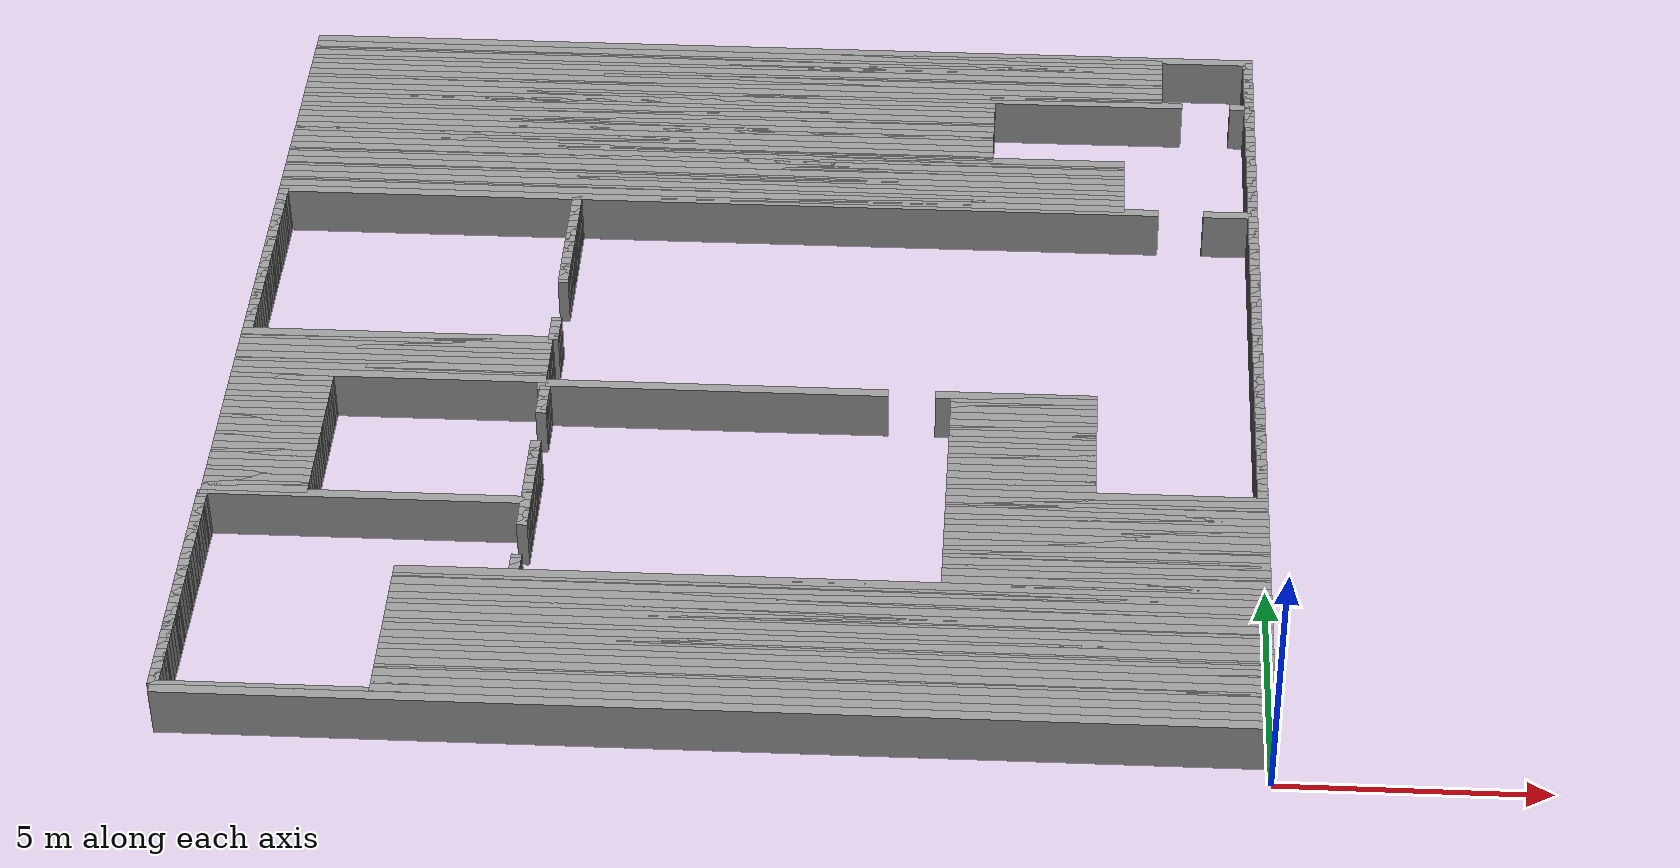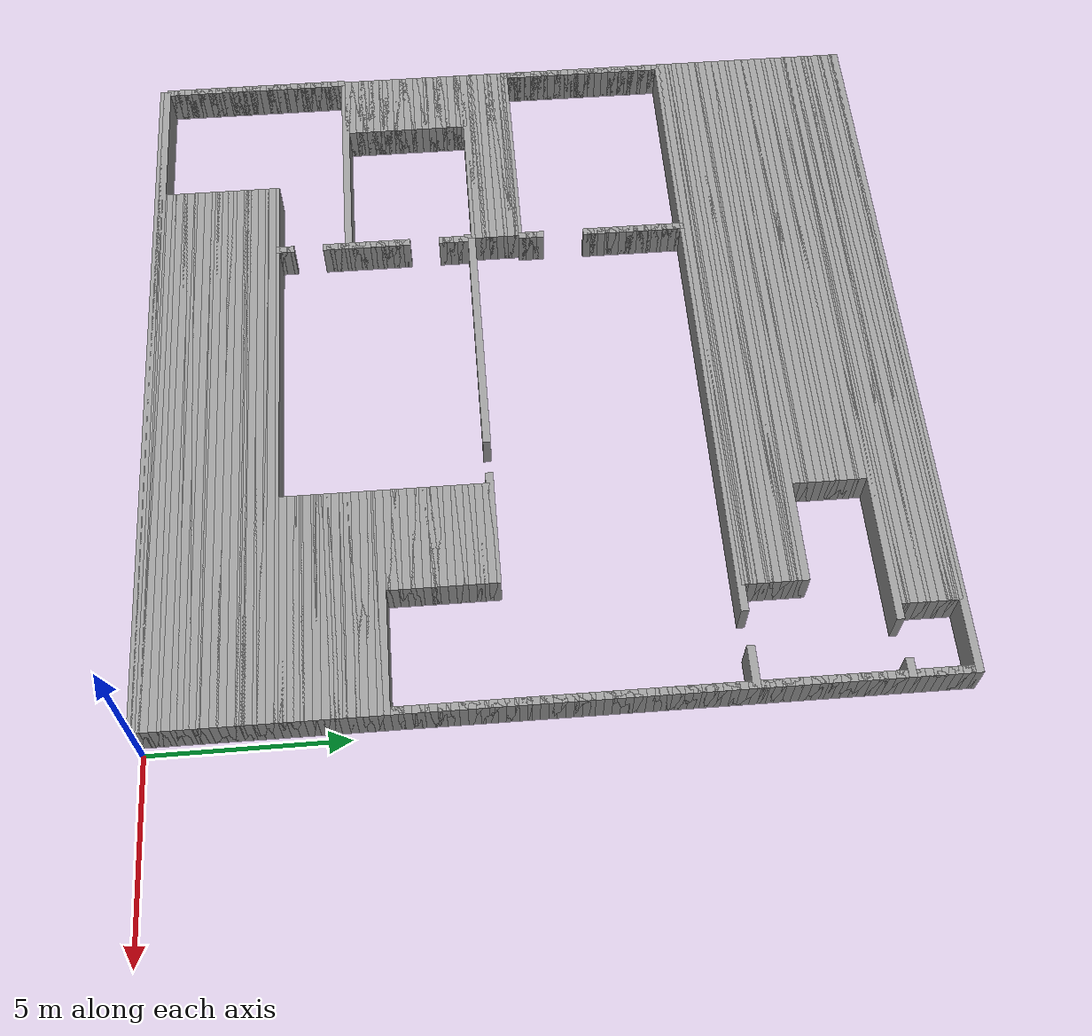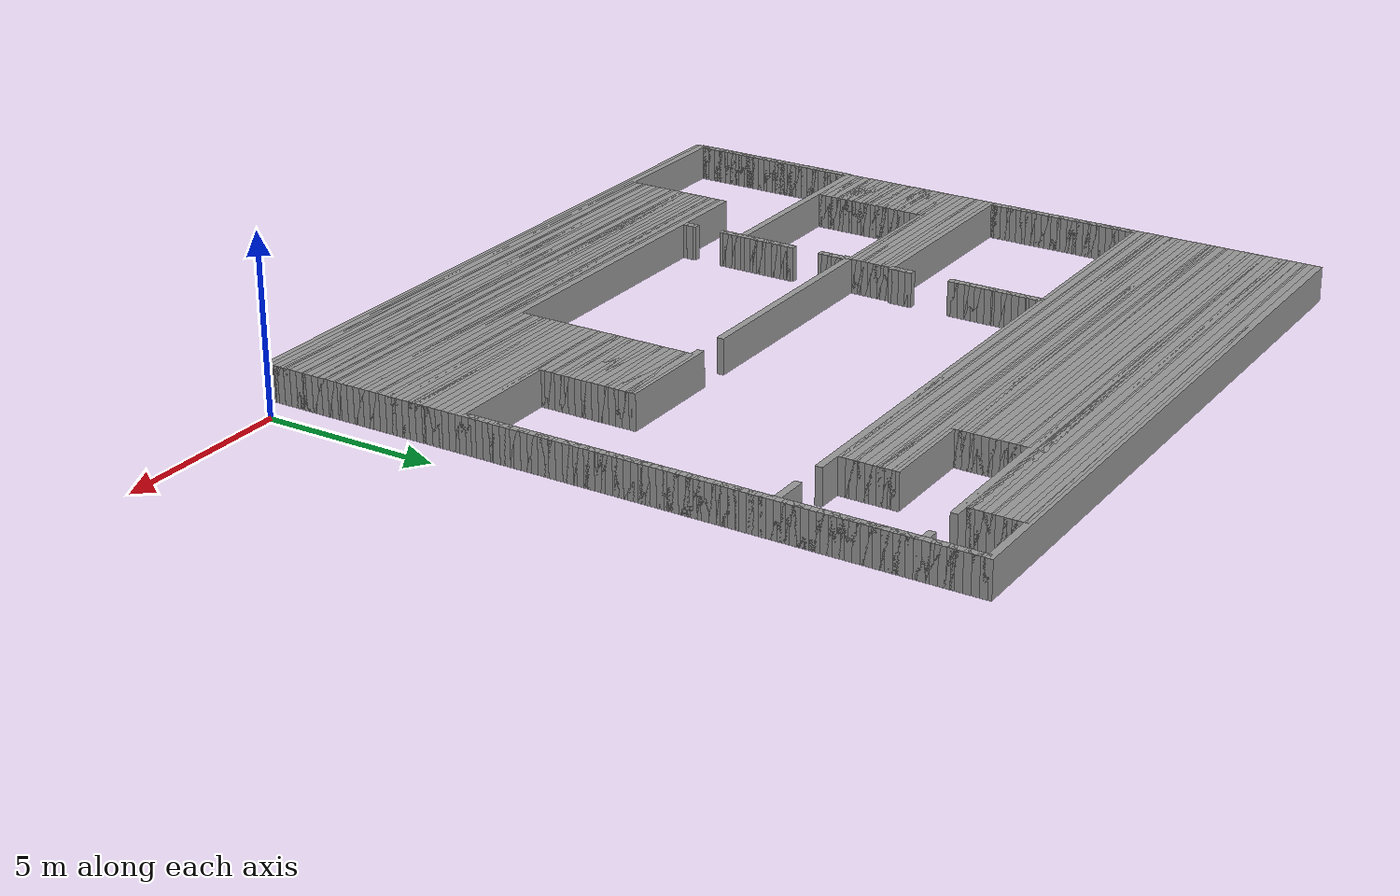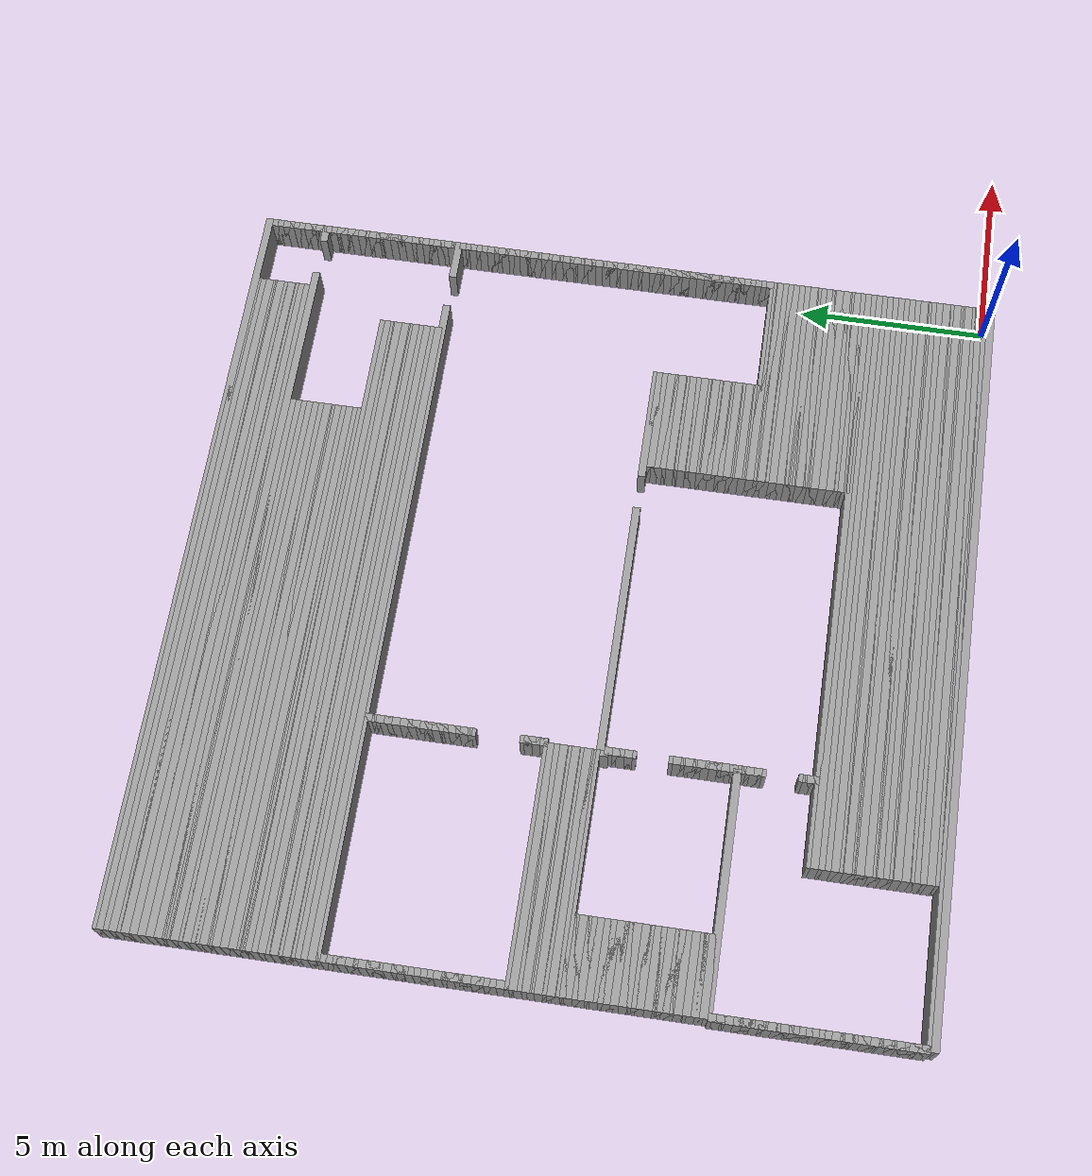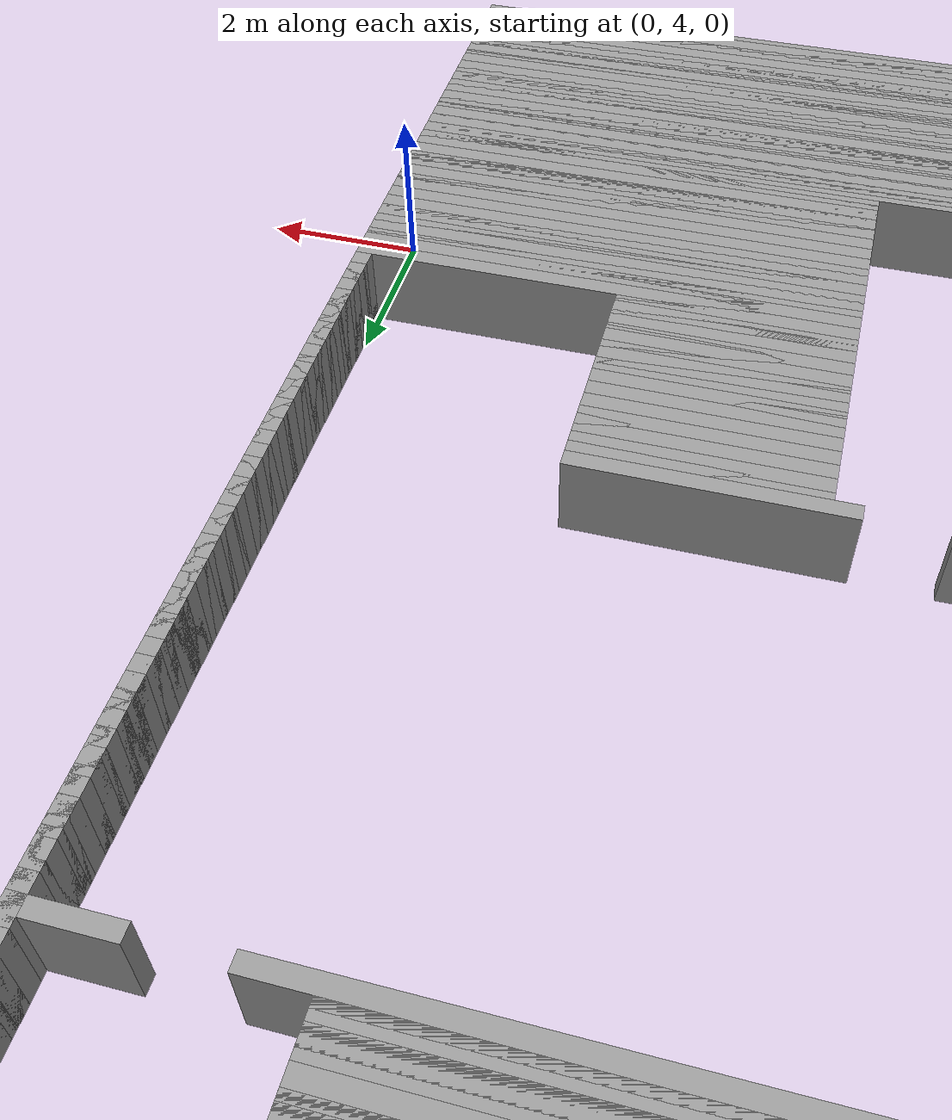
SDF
<?xml version='1.0' encoding='UTF-8'?>
<sdf version="1.6"><world name="GridMap"><model name="GridMap"><pose frame="">0 0 0 0 -0 0</pose><link name="Wall_(99.5,0.0)"><collision name="Wall_(99.5,0.0)_Collision"><geometry><box><size>19.9 0.2 1.0</size></box></geometry><pose frame="">-9.95 0.0 0.5 0 -0 0</pose></collision><visual name="Wall_(99.5,0.0)_Visual"><geometry><box><size>19.9 0.2 1.0</size></box></geometry><pose frame="">-9.95 0.0 0.5 0 -0 0</pose><material><script><uri>file://media/materials/scripts/gazebo.material</uri><name>Gazebo/Grey</name></script><ambient>1 1 1 1</ambient></material><meta><layer>0</layer></meta></visual><pose frame="">0 0 0.5 0 -0 0</pose></link><link name="Wall_(99.5,1.0)"><collision name="Wall_(99.5,1.0)_Collision"><geometry><box><size>19.9 0.2 1.0</size></box></geometry><pose frame="">-9.95 0.1 0.5 0 -0 0</pose></collision><visual name="Wall_(99.5,1.0)_Visual"><geometry><box><size>19.9 0.2 1.0</size></box></geometry><pose frame="">-9.95 0.1 0.5 0 -0 0</pose><material><script><uri>file://media/materials/scripts/gazebo.material</uri><name>Gazebo/Grey</name></script><ambient>1 1 1 1</ambient></material><meta><layer>0</layer></meta></visual><pose frame="">0 0 0.5 0 -0 0</pose></link><link name="Wall_(80.0,2.0)"><collision name="Wall_(80.0,2.0)_Collision"><geometry><box><size>16.0 0.2 1.0</size></box></geometry><pose frame="">-8.0 0.2 0.5 0 -0 0</pose></collision><visual name="Wall_(80.0,2.0)_Visual"><geometry><box><size>16.0 0.2 1.0</size></box></geometry><pose frame="">-8.0 0.2 0.5 0 -0 0</pose><material><script><uri>file://media/materials/scripts/gazebo.material</uri><name>Gazebo/Grey</name></script><ambient>1 1 1 1</ambient></material><meta><layer>0</layer></meta></visual><pose frame="">0 0 0.5 0 -0 0</pose></link><link name="Wall_(198.5,2.0)"><collision name="Wall_(198.5,2.0)_Collision"><geometry><box><size>0.2 0.2 1.0</size></box></geometry><pose frame="">-19.85 0.2 0.5 0 -0 0</pose></collision><visual name="Wall_(198.5,2.0)_Visual"><geometry><box><size>0.2 0.2 1.0</size></box></geometry><pose frame="">-19.85 0.2 0.5 0 -0 0</pose><material><script><uri>file://media/materials/scripts/gazebo.material</uri><name>Gazebo/Grey</name></script><ambient>1 1 1 1</ambient></material><meta><layer>0</layer></meta></visual><pose frame="">0 0 0.5 0 -0 0</pose></link><link name="Wall_(80.0,3.0)"><collision name="Wall_(80.0,3.0)_Collision"><geometry><box><size>16.0 0.2 1.0</size></box></geometry><pose frame="">-8.0 0.3 0.5 0 -0 0</pose></collision><visual name="Wall_(80.0,3.0)_Visual"><geometry><box><size>16.0 0.2 1.0</size></box></geometry><pose frame="">-8.0 0.3 0.5 0 -0 0</pose><material><script><uri>file://media/materials/scripts/gazebo.material</uri><name>Gazebo/Grey</name></script><ambient>1 1 1 1</ambient></material><meta><layer>0</layer></meta></visual><pose frame="">0 0 0.5 0 -0 0</pose></link><link name="Wall_(198.5,3.0)"><collision name="Wall_(198.5,3.0)_Collision"><geometry><box><size>0.2 0.2 1.0</size></box></geometry><pose frame="">-19.85 0.3 0.5 0 -0 0</pose></collision><visual name="Wall_(198.5,3.0)_Visual"><geometry><box><size>0.2 0.2 1.0</size></box></geometry><pose frame="">-19.85 0.3 0.5 0 -0 0</pose><material><script><uri>file://media/materials/scripts/gazebo.material</uri><name>Gazebo/Grey</name></script><ambient>1 1 1 1</ambient></material><meta><layer>0</layer></meta></visual><pose frame="">0 0 0.5 0 -0 0</pose></link><link name="Wall_(80.0,4.0)"><collision name="Wall_(80.0,4.0)_Collision"><geometry><box><size>16.0 0.2 1.0</size></box></geometry><pose frame="">-8.0 0.4 0.5 0 -0 0</pose></collision><visual name="Wall_(80.0,4.0)_Visual"><geometry><box><size>16.0 0.2 1.0</size></box></geometry><pose frame="">-8.0 0.4 0.5 0 -0 0</pose><material><script><uri>file://media/materials/scripts/gazebo.material</uri><name>Gazebo/Grey</name></script><ambient>1 1 1 1</ambient></material><meta><layer>0</layer></meta></visual><pose frame="">0 0 0.5 0 -0 0</pose></link><link name="Wall_(198.5,4.0)"><collision name="Wall_(198.5,4.0)_Collision"><geometry><box><size>0.2 0.2 1.0</size></box></geometry><pose frame="">-19.85 0.4 0.5 0 -0 0</pose></collision><visual name="Wall_(198.5,4.0)_Visual"><geometry><box><size>0.2 0.2 1.0</size></box></geometry><pose frame="">-19.85 0.4 0.5 0 -0 0</pose><material><script><uri>file://media/materials/scripts/gazebo.material</uri><name>Gazebo/Grey</name></script><ambient>1 1 1 1</ambient></material><meta><layer>0</layer></meta></visual><pose frame="">0 0 0.5 0 -0 0</pose></link><link name="Wall_(80.0,5.0)"><collision name="Wall_(80.0,5.0)_Collision"><geometry><box><size>16.0 0.2 1.0</size></box></geometry><pose frame="">-8.0 0.5 0.5 0 -0 0</pose></collision><visual name="Wall_(80.0,5.0)_Visual"><geometry><box><size>16.0 0.2 1.0</size></box></geometry><pose frame="">-8.0 0.5 0.5 0 -0 0</pose><material><script><uri>file://media/materials/scripts/gazebo.material</uri><name>Gazebo/Grey</name></script><ambient>1 1 1 1</ambient></material><meta><layer>0</layer></meta></visual><pose frame="">0 0 0.5 0 -0 0</pose></link><link name="Wall_(198.5,5.0)"><collision name="Wall_(198.5,5.0)_Collision"><geometry><box><size>0.2 0.2 1.0</size></box></geometry><pose frame="">-19.85 0.5 0.5 0 -0 0</pose></collision><visual name="Wall_(198.5,5.0)_Visual"><geometry><box><size>0.2 0.2 1.0</size></box></geometry><pose frame="">-19.85 0.5 0.5 0 -0 0</pose><material><script><uri>file://media/materials/scripts/gazebo.material</uri><name>Gazebo/Grey</name></script><ambient>1 1 1 1</ambient></material><meta><layer>0</layer></meta></visual><pose frame="">0 0 0.5 0 -0 0</pose></link><link name="Wall_(80.0,6.0)"><collision name="Wall_(80.0,6.0)_Collision"><geometry><box><size>16.0 0.2 1.0</size></box></geometry><pose frame="">-8.0 0.6 0.5 0 -0 0</pose></collision><visual name="Wall_(80.0,6.0)_Visual"><geometry><box><size>16.0 0.2 1.0</size></box></geometry><pose frame="">-8.0 0.6 0.5 0 -0 0</pose><material><script><uri>file://media/materials/scripts/gazebo.material</uri><name>Gazebo/Grey</name></script><ambient>1 1 1 1</ambient></material><meta><layer>0</layer></meta></visual><pose frame="">0 0 0.5 0 -0 0</pose></link><link name="Wall_(198.5,6.0)"><collision name="Wall_(198.5,6.0)_Collision"><geometry><box><size>0.2 0.2 1.0</size></box></geometry><pose frame="">-19.85 0.6 0.5 0 -0 0</pose></collision><visual name="Wall_(198.5,6.0)_Visual"><geometry><box><size>0.2 0.2 1.0</size></box></geometry><pose frame="">-19.85 0.6 0.5 0 -0 0</pose><material><script><uri>file://media/materials/scripts/gazebo.material</uri><name>Gazebo/Grey</name></script><ambient>1 1 1 1</ambient></material><meta><layer>0</layer></meta></visual><pose frame="">0 0 0.5 0 -0 0</pose></link><link name="Wall_(80.0,7.0)"><collision name="Wall_(80.0,7.0)_Collision"><geometry><box><size>16.0 0.2 1.0</size></box></geometry><pose frame="">-8.0 0.7 0.5 0 -0 0</pose></collision><visual name="Wall_(80.0,7.0)_Visual"><geometry><box><size>16.0 0.2 1.0</size></box></geometry><pose frame="">-8.0 0.7 0.5 0 -0 0</pose><material><script><uri>file://media/materials/scripts/gazebo.material</uri><name>Gazebo/Grey</name></script><ambient>1 1 1 1</ambient></material><meta><layer>0</layer></meta></visual><pose frame="">0 0 0.5 0 -0 0</pose></link><link name="Wall_(198.5,7.0)"><collision name="Wall_(198.5,7.0)_Collision"><geometry><box><size>0.2 0.2 1.0</size></box></geometry><pose frame="">-19.85 0.7 0.5 0 -0 0</pose></collision><visual name="Wall_(198.5,7.0)_Visual"><geometry><box><size>0.2 0.2 1.0</size></box></geometry><pose frame="">-19.85 0.7 0.5 0 -0 0</pose><material><script><uri>file://media/materials/scripts/gazebo.material</uri><name>Gazebo/Grey</name></script><ambient>1 1 1 1</ambient></material><meta><layer>0</layer></meta></visual><pose frame="">0 0 0.5 0 -0 0</pose></link><link name="Wall_(80.0,8.0)"><collision name="Wall_(80.0,8.0)_Collision"><geometry><box><size>16.0 0.2 1.0</size></box></geometry><pose frame="">-8.0 0.8 0.5 0 -0 0</pose></collision><visual name="Wall_(80.0,8.0)_Visual"><geometry><box><size>16.0 0.2 1.0</size></box></geometry><pose frame="">-8.0 0.8 0.5 0 -0 0</pose><material><script><uri>file://media/materials/scripts/gazebo.material</uri><name>Gazebo/Grey</name></script><ambient>1 1 1 1</ambient></material><meta><layer>0</layer></meta></visual><pose frame="">0 0 0.5 0 -0 0</pose></link><link name="Wall_(198.5,8.0)"><collision name="Wall_(198.5,8.0)_Collision"><geometry><box><size>0.2 0.2 1.0</size></box></geometry><pose frame="">-19.85 0.8 0.5 0 -0 0</pose></collision><visual name="Wall_(198.5,8.0)_Visual"><geometry><box><size>0.2 0.2 1.0</size></box></geometry><pose frame="">-19.85 0.8 0.5 0 -0 0</pose><material><script><uri>file://media/materials/scripts/gazebo.material</uri><name>Gazebo/Grey</name></script><ambient>1 1 1 1</ambient></material><meta><layer>0</layer></meta></visual><pose frame="">0 0 0.5 0 -0 0</pose></link><link name="Wall_(80.0,9.0)"><collision name="Wall_(80.0,9.0)_Collision"><geometry><box><size>16.0 0.2 1.0</size></box></geometry><pose frame="">-8.0 0.9 0.5 0 -0 0</pose></collision><visual name="Wall_(80.0,9.0)_Visual"><geometry><box><size>16.0 0.2 1.0</size></box></geometry><pose frame="">-8.0 0.9 0.5 0 -0 0</pose><material><script><uri>file://media/materials/scripts/gazebo.material</uri><name>Gazebo/Grey</name></script><ambient>1 1 1 1</ambient></material><meta><layer>0</layer></meta></visual><pose frame="">0 0 0.5 0 -0 0</pose></link><link name="Wall_(198.5,9.0)"><collision name="Wall_(198.5,9.0)_Collision"><geometry><box><size>0.2 0.2 1.0</size></box></geometry><pose frame="">-19.85 0.9 0.5 0 -0 0</pose></collision><visual name="Wall_(198.5,9.0)_Visual"><geometry><box><size>0.2 0.2 1.0</size></box></geometry><pose frame="">-19.85 0.9 0.5 0 -0 0</pose><material><script><uri>file://media/materials/scripts/gazebo.material</uri><name>Gazebo/Grey</name></script><ambient>1 1 1 1</ambient></material><meta><layer>0</layer></meta></visual><pose frame="">0 0 0.5 0 -0 0</pose></link><link name="Wall_(80.0,10.0)"><collision name="Wall_(80.0,10.0)_Collision"><geometry><box><size>16.0 0.2 1.0</size></box></geometry><pose frame="">-8.0 1.0 0.5 0 -0 0</pose></collision><visual name="Wall_(80.0,10.0)_Visual"><geometry><box><size>16.0 0.2 1.0</size></box></geometry><pose frame="">-8.0 1.0 0.5 0 -0 0</pose><material><script><uri>file://media/materials/scripts/gazebo.material</uri><name>Gazebo/Grey</name></script><ambient>1 1 1 1</ambient></material><meta><layer>0</layer></meta></visual><pose frame="">0 0 0.5 0 -0 0</pose></link><link name="Wall_(198.5,10.0)"><collision name="Wall_(198.5,10.0)_Collision"><geometry><box><size>0.2 0.2 1.0</size></box></geometry><pose frame="">-19.85 1.0 0.5 0 -0 0</pose></collision><visual name="Wall_(198.5,10.0)_Visual"><geometry><box><size>0.2 0.2 1.0</size></box></geometry><pose frame="">-19.85 1.0 0.5 0 -0 0</pose><material><script><uri>file://media/materials/scripts/gazebo.material</uri><name>Gazebo/Grey</name></script><ambient>1 1 1 1</ambient></material><meta><layer>0</layer></meta></visual><pose frame="">0 0 0.5 0 -0 0</pose></link><link name="Wall_(80.0,11.0)"><collision name="Wall_(80.0,11.0)_Collision"><geometry><box><size>16.0 0.2 1.0</size></box></geometry><pose frame="">-8.0 1.1 0.5 0 -0 0</pose></collision><visual name="Wall_(80.0,11.0)_Visual"><geometry><box><size>16.0 0.2 1.0</size></box></geometry><pose frame="">-8.0 1.1 0.5 0 -0 0</pose><material><script><uri>file://media/materials/scripts/gazebo.material</uri><name>Gazebo/Grey</name></script><ambient>1 1 1 1</ambient></material><meta><layer>0</layer></meta></visual><pose frame="">0 0 0.5 0 -0 0</pose></link><link name="Wall_(198.5,11.0)"><collision name="Wall_(198.5,11.0)_Collision"><geometry><box><size>0.2 0.2 1.0</size></box></geometry><pose frame="">-19.85 1.1 0.5 0 -0 0</pose></collision><visual name="Wall_(198.5,11.0)_Visual"><geometry><box><size>0.2 0.2 1.0</size></box></geometry><pose frame="">-19.85 1.1 0.5 0 -0 0</pose><material><script><uri>file://media/materials/scripts/gazebo.material</uri><name>Gazebo/Grey</name></script><ambient>1 1 1 1</ambient></material><meta><layer>0</layer></meta></visual><pose frame="">0 0 0.5 0 -0 0</pose></link><link name="Wall_(80.0,12.0)"><collision name="Wall_(80.0,12.0)_Collision"><geometry><box><size>16.0 0.2 1.0</size></box></geometry><pose frame="">-8.0 1.2 0.5 0 -0 0</pose></collision><visual name="Wall_(80.0,12.0)_Visual"><geometry><box><size>16.0 0.2 1.0</size></box></geometry><pose frame="">-8.0 1.2 0.5 0 -0 0</pose><material><script><uri>file://media/materials/scripts/gazebo.material</uri><name>Gazebo/Grey</name></script><ambient>1 1 1 1</ambient></material><meta><layer>0</layer></meta></visual><pose frame="">0 0 0.5 0 -0 0</pose></link><link name="Wall_(198.5,12.0)"><collision name="Wall_(198.5,12.0)_Collision"><geometry><box><size>0.2 0.2 1.0</size></box></geometry><pose frame="">-19.85 1.2 0.5 0 -0 0</pose></collision><visual name="Wall_(198.5,12.0)_Visual"><geometry><box><size>0.2 0.2 1.0</size></box></geometry><pose frame="">-19.85 1.2 0.5 0 -0 0</pose><material><script><uri>file://media/materials/scripts/gazebo.material</uri><name>Gazebo/Grey</name></script><ambient>1 1 1 1</ambient></material><meta><layer>0</layer></meta></visual><pose frame="">0 0 0.5 0 -0 0</pose></link><link name="Wall_(80.0,13.0)"><collision name="Wall_(80.0,13.0)_Collision"><geometry><box><size>16.0 0.2 1.0</size></box></geometry><pose frame="">-8.0 1.3 0.5 0 -0 0</pose></collision><visual name="Wall_(80.0,13.0)_Visual"><geometry><box><size>16.0 0.2 1.0</size></box></geometry><pose frame="">-8.0 1.3 0.5 0 -0 0</pose><material><script><uri>file://media/materials/scripts/gazebo.material</uri><name>Gazebo/Grey</name></script><ambient>1 1 1 1</ambient></material><meta><layer>0</layer></meta></visual><pose frame="">0 0 0.5 0 -0 0</pose></link><link name="Wall_(198.5,13.0)"><collision name="Wall_(198.5,13.0)_Collision"><geometry><box><size>0.2 0.2 1.0</size></box></geometry><pose frame="">-19.85 1.3 0.5 0 -0 0</pose></collision><visual name="Wall_(198.5,13.0)_Visual"><geometry><box><size>0.2 0.2 1.0</size></box></geometry><pose frame="">-19.85 1.3 0.5 0 -0 0</pose><material><script><uri>file://media/materials/scripts/gazebo.material</uri><name>Gazebo/Grey</name></script><ambient>1 1 1 1</ambient></material><meta><layer>0</layer></meta></visual><pose frame="">0 0 0.5 0 -0 0</pose></link><link name="Wall_(80.0,14.0)"><collision name="Wall_(80.0,14.0)_Collision"><geometry><box><size>16.0 0.2 1.0</size></box></geometry><pose frame="">-8.0 1.4 0.5 0 -0 0</pose></collision><visual name="Wall_(80.0,14.0)_Visual"><geometry><box><size>16.0 0.2 1.0</size></box></geometry><pose frame="">-8.0 1.4 0.5 0 -0 0</pose><material><script><uri>file://media/materials/scripts/gazebo.material</uri><name>Gazebo/Grey</name></script><ambient>1 1 1 1</ambient></material><meta><layer>0</layer></meta></visual><pose frame="">0 0 0.5 0 -0 0</pose></link><link name="Wall_(198.5,14.0)"><collision name="Wall_(198.5,14.0)_Collision"><geometry><box><size>0.2 0.2 1.0</size></box></geometry><pose frame="">-19.85 1.4 0.5 0 -0 0</pose></collision><visual name="Wall_(198.5,14.0)_Visual"><geometry><box><size>0.2 0.2 1.0</size></box></geometry><pose frame="">-19.85 1.4 0.5 0 -0 0</pose><material><script><uri>file://media/materials/scripts/gazebo.material</uri><name>Gazebo/Grey</name></script><ambient>1 1 1 1</ambient></material><meta><layer>0</layer></meta></visual><pose frame="">0 0 0.5 0 -0 0</pose></link><link name="Wall_(80.0,15.0)"><collision name="Wall_(80.0,15.0)_Collision"><geometry><box><size>16.0 0.2 1.0</size></box></geometry><pose frame="">-8.0 1.5 0.5 0 -0 0</pose></collision><visual name="Wall_(80.0,15.0)_Visual"><geometry><box><size>16.0 0.2 1.0</size></box></geometry><pose frame="">-8.0 1.5 0.5 0 -0 0</pose><material><script><uri>file://media/materials/scripts/gazebo.material</uri><name>Gazebo/Grey</name></script><ambient>1 1 1 1</ambient></material><meta><layer>0</layer></meta></visual><pose frame="">0 0 0.5 0 -0 0</pose></link><link name="Wall_(198.5,15.0)"><collision name="Wall_(198.5,15.0)_Collision"><geometry><box><size>0.2 0.2 1.0</size></box></geometry><pose frame="">-19.85 1.5 0.5 0 -0 0</pose></collision><visual name="Wall_(198.5,15.0)_Visual"><geometry><box><size>0.2 0.2 1.0</size></box></geometry><pose frame="">-19.85 1.5 0.5 0 -0 0</pose><material><script><uri>file://media/materials/scripts/gazebo.material</uri><name>Gazebo/Grey</name></script><ambient>1 1 1 1</ambient></material><meta><layer>0</layer></meta></visual><pose frame="">0 0 0.5 0 -0 0</pose></link><link name="Wall_(80.0,16.0)"><collision name="Wall_(80.0,16.0)_Collision"><geometry><box><size>16.0 0.2 1.0</size></box></geometry><pose frame="">-8.0 1.6 0.5 0 -0 0</pose></collision><visual name="Wall_(80.0,16.0)_Visual"><geometry><box><size>16.0 0.2 1.0</size></box></geometry><pose frame="">-8.0 1.6 0.5 0 -0 0</pose><material><script><uri>file://media/materials/scripts/gazebo.material</uri><name>Gazebo/Grey</name></script><ambient>1 1 1 1</ambient></material><meta><layer>0</layer></meta></visual><pose frame="">0 0 0.5 0 -0 0</pose></link><link name="Wall_(198.5,16.0)"><collision name="Wall_(198.5,16.0)_Collision"><geometry><box><size>0.2 0.2 1.0</size></box></geometry><pose frame="">-19.85 1.6 0.5 0 -0 0</pose></collision><visual name="Wall_(198.5,16.0)_Visual"><geometry><box><size>0.2 0.2 1.0</size></box></geometry><pose frame="">-19.85 1.6 0.5 0 -0 0</pose><material><script><uri>file://media/materials/scripts/gazebo.material</uri><name>Gazebo/Grey</name></script><ambient>1 1 1 1</ambient></material><meta><layer>0</layer></meta></visual><pose frame="">0 0 0.5 0 -0 0</pose></link><link name="Wall_(80.0,17.0)"><collision name="Wall_(80.0,17.0)_Collision"><geometry><box><size>16.0 0.2 1.0</size></box></geometry><pose frame="">-8.0 1.7 0.5 0 -0 0</pose></collision><visual name="Wall_(80.0,17.0)_Visual"><geometry><box><size>16.0 0.2 1.0</size></box></geometry><pose frame="">-8.0 1.7 0.5 0 -0 0</pose><material><script><uri>file://media/materials/scripts/gazebo.material</uri><name>Gazebo/Grey</name></script><ambient>1 1 1 1</ambient></material><meta><layer>0</layer></meta></visual><pose frame="">0 0 0.5 0 -0 0</pose></link><link name="Wall_(198.5,17.0)"><collision name="Wall_(198.5,17.0)_Collision"><geometry><box><size>0.2 0.2 1.0</size></box></geometry><pose frame="">-19.85 1.7 0.5 0 -0 0</pose></collision><visual name="Wall_(198.5,17.0)_Visual"><geometry><box><size>0.2 0.2 1.0</size></box></geometry><pose frame="">-19.85 1.7 0.5 0 -0 0</pose><material><script><uri>file://media/materials/scripts/gazebo.material</uri><name>Gazebo/Grey</name></script><ambient>1 1 1 1</ambient></material><meta><layer>0</layer></meta></visual><pose frame="">0 0 0.5 0 -0 0</pose></link><link name="Wall_(80.0,18.0)"><collision name="Wall_(80.0,18.0)_Collision"><geometry><box><size>16.0 0.2 1.0</size></box></geometry><pose frame="">-8.0 1.8 0.5 0 -0 0</pose></collision><visual name="Wall_(80.0,18.0)_Visual"><geometry><box><size>16.0 0.2 1.0</size></box></geometry><pose frame="">-8.0 1.8 0.5 0 -0 0</pose><material><script><uri>file://media/materials/scripts/gazebo.material</uri><name>Gazebo/Grey</name></script><ambient>1 1 1 1</ambient></material><meta><layer>0</layer></meta></visual><pose frame="">0 0 0.5 0 -0 0</pose></link><link name="Wall_(198.5,18.0)"><collision name="Wall_(198.5,18.0)_Collision"><geometry><box><size>0.2 0.2 1.0</size></box></geometry><pose frame="">-19.85 1.8 0.5 0 -0 0</pose></collision><visual name="Wall_(198.5,18.0)_Visual"><geometry><box><size>0.2 0.2 1.0</size></box></geometry><pose frame="">-19.85 1.8 0.5 0 -0 0</pose><material><script><uri>file://media/materials/scripts/gazebo.material</uri><name>Gazebo/Grey</name></script><ambient>1 1 1 1</ambient></material><meta><layer>0</layer></meta></visual><pose frame="">0 0 0.5 0 -0 0</pose></link><link name="Wall_(80.0,19.0)"><collision name="Wall_(80.0,19.0)_Collision"><geometry><box><size>16.0 0.2 1.0</size></box></geometry><pose frame="">-8.0 1.9 0.5 0 -0 0</pose></collision><visual name="Wall_(80.0,19.0)_Visual"><geometry><box><size>16.0 0.2 1.0</size></box></geometry><pose frame="">-8.0 1.9 0.5 0 -0 0</pose><material><script><uri>file://media/materials/scripts/gazebo.material</uri><name>Gazebo/Grey</name></script><ambient>1 1 1 1</ambient></material><meta><layer>0</layer></meta></visual><pose frame="">0 0 0.5 0 -0 0</pose></link><link name="Wall_(198.5,19.0)"><collision name="Wall_(198.5,19.0)_Collision"><geometry><box><size>0.2 0.2 1.0</size></box></geometry><pose frame="">-19.85 1.9 0.5 0 -0 0</pose></collision><visual name="Wall_(198.5,19.0)_Visual"><geometry><box><size>0.2 0.2 1.0</size></box></geometry><pose frame="">-19.85 1.9 0.5 0 -0 0</pose><material><script><uri>file://media/materials/scripts/gazebo.material</uri><name>Gazebo/Grey</name></script><ambient>1 1 1 1</ambient></material><meta><layer>0</layer></meta></visual><pose frame="">0 0 0.5 0 -0 0</pose></link><link name="Wall_(80.0,20.0)"><collision name="Wall_(80.0,20.0)_Collision"><geometry><box><size>16.0 0.2 1.0</size></box></geometry><pose frame="">-8.0 2.0 0.5 0 -0 0</pose></collision><visual name="Wall_(80.0,20.0)_Visual"><geometry><box><size>16.0 0.2 1.0</size></box></geometry><pose frame="">-8.0 2.0 0.5 0 -0 0</pose><material><script><uri>file://media/materials/scripts/gazebo.material</uri><name>Gazebo/Grey</name></script><ambient>1 1 1 1</ambient></material><meta><layer>0</layer></meta></visual><pose frame="">0 0 0.5 0 -0 0</pose></link><link name="Wall_(198.5,20.0)"><collision name="Wall_(198.5,20.0)_Collision"><geometry><box><size>0.2 0.2 1.0</size></box></geometry><pose frame="">-19.85 2.0 0.5 0 -0 0</pose></collision><visual name="Wall_(198.5,20.0)_Visual"><geometry><box><size>0.2 0.2 1.0</size></box></geometry><pose frame="">-19.85 2.0 0.5 0 -0 0</pose><material><script><uri>file://media/materials/scripts/gazebo.material</uri><name>Gazebo/Grey</name></script><ambient>1 1 1 1</ambient></material><meta><layer>0</layer></meta></visual><pose frame="">0 0 0.5 0 -0 0</pose></link><link name="Wall_(80.0,21.0)"><collision name="Wall_(80.0,21.0)_Collision"><geometry><box><size>16.0 0.2 1.0</size></box></geometry><pose frame="">-8.0 2.1 0.5 0 -0 0</pose></collision><visual name="Wall_(80.0,21.0)_Visual"><geometry><box><size>16.0 0.2 1.0</size></box></geometry><pose frame="">-8.0 2.1 0.5 0 -0 0</pose><material><script><uri>file://media/materials/scripts/gazebo.material</uri><name>Gazebo/Grey</name></script><ambient>1 1 1 1</ambient></material><meta><layer>0</layer></meta></visual><pose frame="">0 0 0.5 0 -0 0</pose></link><link name="Wall_(198.5,21.0)"><collision name="Wall_(198.5,21.0)_Collision"><geometry><box><size>0.2 0.2 1.0</size></box></geometry><pose frame="">-19.85 2.1 0.5 0 -0 0</pose></collision><visual name="Wall_(198.5,21.0)_Visual"><geometry><box><size>0.2 0.2 1.0</size></box></geometry><pose frame="">-19.85 2.1 0.5 0 -0 0</pose><material><script><uri>file://media/materials/scripts/gazebo.material</uri><name>Gazebo/Grey</name></script><ambient>1 1 1 1</ambient></material><meta><layer>0</layer></meta></visual><pose frame="">0 0 0.5 0 -0 0</pose></link><link name="Wall_(80.0,22.0)"><collision name="Wall_(80.0,22.0)_Collision"><geometry><box><size>16.0 0.2 1.0</size></box></geometry><pose frame="">-8.0 2.2 0.5 0 -0 0</pose></collision><visual name="Wall_(80.0,22.0)_Visual"><geometry><box><size>16.0 0.2 1.0</size></box></geometry><pose frame="">-8.0 2.2 0.5 0 -0 0</pose><material><script><uri>file://media/materials/scripts/gazebo.material</uri><name>Gazebo/Grey</name></script><ambient>1 1 1 1</ambient></material><meta><layer>0</layer></meta></visual><pose frame="">0 0 0.5 0 -0 0</pose></link><link name="Wall_(198.5,22.0)"><collision name="Wall_(198.5,22.0)_Collision"><geometry><box><size>0.2 0.2 1.0</size></box></geometry><pose frame="">-19.85 2.2 0.5 0 -0 0</pose></collision><visual name="Wall_(198.5,22.0)_Visual"><geometry><box><size>0.2 0.2 1.0</size></box></geometry><pose frame="">-19.85 2.2 0.5 0 -0 0</pose><material><script><uri>file://media/materials/scripts/gazebo.material</uri><name>Gazebo/Grey</name></script><ambient>1 1 1 1</ambient></material><meta><layer>0</layer></meta></visual><pose frame="">0 0 0.5 0 -0 0</pose></link><link name="Wall_(80.0,23.0)"><collision name="Wall_(80.0,23.0)_Collision"><geometry><box><size>16.0 0.2 1.0</size></box></geometry><pose frame="">-8.0 2.3 0.5 0 -0 0</pose></collision><visual name="Wall_(80.0,23.0)_Visual"><geometry><box><size>16.0 0.2 1.0</size></box></geometry><pose frame="">-8.0 2.3 0.5 0 -0 0</pose><material><script><uri>file://media/materials/scripts/gazebo.material</uri><name>Gazebo/Grey</name></script><ambient>1 1 1 1</ambient></material><meta><layer>0</layer></meta></visual><pose frame="">0 0 0.5 0 -0 0</pose></link><link name="Wall_(198.5,23.0)"><collision name="Wall_(198.5,23.0)_Collision"><geometry><box><size>0.2 0.2 1.0</size></box></geometry><pose frame="">-19.85 2.3 0.5 0 -0 0</pose></collision><visual name="Wall_(198.5,23.0)_Visual"><geometry><box><size>0.2 0.2 1.0</size></box></geometry><pose frame="">-19.85 2.3 0.5 0 -0 0</pose><material><script><uri>file://media/materials/scripts/gazebo.material</uri><name>Gazebo/Grey</name></script><ambient>1 1 1 1</ambient></material><meta><layer>0</layer></meta></visual><pose frame="">0 0 0.5 0 -0 0</pose></link><link name="Wall_(80.0,24.0)"><collision name="Wall_(80.0,24.0)_Collision"><geometry><box><size>16.0 0.2 1.0</size></box></geometry><pose frame="">-8.0 2.4 0.5 0 -0 0</pose></collision><visual name="Wall_(80.0,24.0)_Visual"><geometry><box><size>16.0 0.2 1.0</size></box></geometry><pose frame="">-8.0 2.4 0.5 0 -0 0</pose><material><script><uri>file://media/materials/scripts/gazebo.material</uri><name>Gazebo/Grey</name></script><ambient>1 1 1 1</ambient></material><meta><layer>0</layer></meta></visual><pose frame="">0 0 0.5 0 -0 0</pose></link><link name="Wall_(198.5,24.0)"><collision name="Wall_(198.5,24.0)_Collision"><geometry><box><size>0.2 0.2 1.0</size></box></geometry><pose frame="">-19.85 2.4 0.5 0 -0 0</pose></collision><visual name="Wall_(198.5,24.0)_Visual"><geometry><box><size>0.2 0.2 1.0</size></box></geometry><pose frame="">-19.85 2.4 0.5 0 -0 0</pose><material><script><uri>file://media/materials/scripts/gazebo.material</uri><name>Gazebo/Grey</name></script><ambient>1 1 1 1</ambient></material><meta><layer>0</layer></meta></visual><pose frame="">0 0 0.5 0 -0 0</pose></link><link name="Wall_(80.0,25.0)"><collision name="Wall_(80.0,25.0)_Collision"><geometry><box><size>16.0 0.2 1.0</size></box></geometry><pose frame="">-8.0 2.5 0.5 0 -0 0</pose></collision><visual name="Wall_(80.0,25.0)_Visual"><geometry><box><size>16.0 0.2 1.0</size></box></geometry><pose frame="">-8.0 2.5 0.5 0 -0 0</pose><material><script><uri>file://media/materials/scripts/gazebo.material</uri><name>Gazebo/Grey</name></script><ambient>1 1 1 1</ambient></material><meta><layer>0</layer></meta></visual><pose frame="">0 0 0.5 0 -0 0</pose></link><link name="Wall_(198.5,25.0)"><collision name="Wall_(198.5,25.0)_Collision"><geometry><box><size>0.2 0.2 1.0</size></box></geometry><pose frame="">-19.85 2.5 0.5 0 -0 0</pose></collision><visual name="Wall_(198.5,25.0)_Visual"><geometry><box><size>0.2 0.2 1.0</size></box></geometry><pose frame="">-19.85 2.5 0.5 0 -0 0</pose><material><script><uri>file://media/materials/scripts/gazebo.material</uri><name>Gazebo/Grey</name></script><ambient>1 1 1 1</ambient></material><meta><layer>0</layer></meta></visual><pose frame="">0 0 0.5 0 -0 0</pose></link><link name="Wall_(80.0,26.0)"><collision name="Wall_(80.0,26.0)_Collision"><geometry><box><size>16.0 0.2 1.0</size></box></geometry><pose frame="">-8.0 2.6 0.5 0 -0 0</pose></collision><visual name="Wall_(80.0,26.0)_Visual"><geometry><box><size>16.0 0.2 1.0</size></box></geometry><pose frame="">-8.0 2.6 0.5 0 -0 0</pose><material><script><uri>file://media/materials/scripts/gazebo.material</uri><name>Gazebo/Grey</name></script><ambient>1 1 1 1</ambient></material><meta><layer>0</layer></meta></visual><pose frame="">0 0 0.5 0 -0 0</pose></link><link name="Wall_(198.5,26.0)"><collision name="Wall_(198.5,26.0)_Collision"><geometry><box><size>0.2 0.2 1.0</size></box></geometry><pose frame="">-19.85 2.6 0.5 0 -0 0</pose></collision><visual name="Wall_(198.5,26.0)_Visual"><geometry><box><size>0.2 0.2 1.0</size></box></geometry><pose frame="">-19.85 2.6 0.5 0 -0 0</pose><material><script><uri>file://media/materials/scripts/gazebo.material</uri><name>Gazebo/Grey</name></script><ambient>1 1 1 1</ambient></material><meta><layer>0</layer></meta></visual><pose frame="">0 0 0.5 0 -0 0</pose></link><link name="Wall_(80.0,27.0)"><collision name="Wall_(80.0,27.0)_Collision"><geometry><box><size>16.0 0.2 1.0</size></box></geometry><pose frame="">-8.0 2.7 0.5 0 -0 0</pose></collision><visual name="Wall_(80.0,27.0)_Visual"><geometry><box><size>16.0 0.2 1.0</size></box></geometry><pose frame="">-8.0 2.7 0.5 0 -0 0</pose><material><script><uri>file://media/materials/scripts/gazebo.material</uri><name>Gazebo/Grey</name></script><ambient>1 1 1 1</ambient></material><meta><layer>0</layer></meta></visual><pose frame="">0 0 0.5 0 -0 0</pose></link><link name="Wall_(198.5,27.0)"><collision name="Wall_(198.5,27.0)_Collision"><geometry><box><size>0.2 0.2 1.0</size></box></geometry><pose frame="">-19.85 2.7 0.5 0 -0 0</pose></collision><visual name="Wall_(198.5,27.0)_Visual"><geometry><box><size>0.2 0.2 1.0</size></box></geometry><pose frame="">-19.85 2.7 0.5 0 -0 0</pose><material><script><uri>file://media/materials/scripts/gazebo.material</uri><name>Gazebo/Grey</name></script><ambient>1 1 1 1</ambient></material><meta><layer>0</layer></meta></visual><pose frame="">0 0 0.5 0 -0 0</pose></link><link name="Wall_(80.0,28.0)"><collision name="Wall_(80.0,28.0)_Collision"><geometry><box><size>16.0 0.2 1.0</size></box></geometry><pose frame="">-8.0 2.8 0.5 0 -0 0</pose></collision><visual name="Wall_(80.0,28.0)_Visual"><geometry><box><size>16.0 0.2 1.0</size></box></geometry><pose frame="">-8.0 2.8 0.5 0 -0 0</pose><material><script><uri>file://media/materials/scripts/gazebo.material</uri><name>Gazebo/Grey</name></script><ambient>1 1 1 1</ambient></material><meta><layer>0</layer></meta></visual><pose frame="">0 0 0.5 0 -0 0</pose></link><link name="Wall_(198.5,28.0)"><collision name="Wall_(198.5,28.0)_Collision"><geometry><box><size>0.2 0.2 1.0</size></box></geometry><pose frame="">-19.85 2.8 0.5 0 -0 0</pose></collision><visual name="Wall_(198.5,28.0)_Visual"><geometry><box><size>0.2 0.2 1.0</size></box></geometry><pose frame="">-19.85 2.8 0.5 0 -0 0</pose><material><script><uri>file://media/materials/scripts/gazebo.material</uri><name>Gazebo/Grey</name></script><ambient>1 1 1 1</ambient></material><meta><layer>0</layer></meta></visual><pose frame="">0 0 0.5 0 -0 0</pose></link><link name="Wall_(80.0,29.0)"><collision name="Wall_(80.0,29.0)_Collision"><geometry><box><size>16.0 0.2 1.0</size></box></geometry><pose frame="">-8.0 2.9 0.5 0 -0 0</pose></collision><visual name="Wall_(80.0,29.0)_Visual"><geometry><box><size>16.0 0.2 1.0</size></box></geometry><pose frame="">-8.0 2.9 0.5 0 -0 0</pose><material><script><uri>file://media/materials/scripts/gazebo.material</uri><name>Gazebo/Grey</name></script><ambient>1 1 1 1</ambient></material><meta><layer>0</layer></meta></visual><pose frame="">0 0 0.5 0 -0 0</pose></link><link name="Wall_(198.5,29.0)"><collision name="Wall_(198.5,29.0)_Collision"><geometry><box><size>0.2 0.2 1.0</size></box></geometry><pose frame="">-19.85 2.9 0.5 0 -0 0</pose></collision><visual name="Wall_(198.5,29.0)_Visual"><geometry><box><size>0.2 0.2 1.0</size></box></geometry><pose frame="">-19.85 2.9 0.5 0 -0 0</pose><material><script><uri>file://media/materials/scripts/gazebo.material</uri><name>Gazebo/Grey</name></script><ambient>1 1 1 1</ambient></material><meta><layer>0</layer></meta></visual><pose frame="">0 0 0.5 0 -0 0</pose></link><link name="Wall_(80.0,30.0)"><collision name="Wall_(80.0,30.0)_Collision"><geometry><box><size>16.0 0.2 1.0</size></box></geometry><pose frame="">-8.0 3.0 0.5 0 -0 0</pose></collision><visual name="Wall_(80.0,30.0)_Visual"><geometry><box><size>16.0 0.2 1.0</size></box></geometry><pose frame="">-8.0 3.0 0.5 0 -0 0</pose><material><script><uri>file://media/materials/scripts/gazebo.material</uri><name>Gazebo/Grey</name></script><ambient>1 1 1 1</ambient></material><meta><layer>0</layer></meta></visual><pose frame="">0 0 0.5 0 -0 0</pose></link><link name="Wall_(198.5,30.0)"><collision name="Wall_(198.5,30.0)_Collision"><geometry><box><size>0.2 0.2 1.0</size></box></geometry><pose frame="">-19.85 3.0 0.5 0 -0 0</pose></collision><visual name="Wall_(198.5,30.0)_Visual"><geometry><box><size>0.2 0.2 1.0</size></box></geometry><pose frame="">-19.85 3.0 0.5 0 -0 0</pose><material><script><uri>file://media/materials/scripts/gazebo.material</uri><name>Gazebo/Grey</name></script><ambient>1 1 1 1</ambient></material><meta><layer>0</layer></meta></visual><pose frame="">0 0 0.5 0 -0 0</pose></link><link name="Wall_(80.0,31.0)"><collision name="Wall_(80.0,31.0)_Collision"><geometry><box><size>16.0 0.2 1.0</size></box></geometry><pose frame="">-8.0 3.1 0.5 0 -0 0</pose></collision><visual name="Wall_(80.0,31.0)_Visual"><geometry><box><size>16.0 0.2 1.0</size></box></geometry><pose frame="">-8.0 3.1 0.5 0 -0 0</pose><material><script><uri>file://media/materials/scripts/gazebo.material</uri><name>Gazebo/Grey</name></script><ambient>1 1 1 1</ambient></material><meta><layer>0</layer></meta></visual><pose frame="">0 0 0.5 0 -0 0</pose></link><link name="Wall_(198.5,31.0)"><collision name="Wall_(198.5,31.0)_Collision"><geometry><box><size>0.2 0.2 1.0</size></box></geometry><pose frame="">-19.85 3.1 0.5 0 -0 0</pose></collision><visual name="Wall_(198.5,31.0)_Visual"><geometry><box><size>0.2 0.2 1.0</size></box></geometry><pose frame="">-19.85 3.1 0.5 0 -0 0</pose><material><script><uri>file://media/materials/scripts/gazebo.material</uri><name>Gazebo/Grey</name></script><ambient>1 1 1 1</ambient></material><meta><layer>0</layer></meta></visual><pose frame="">0 0 0.5 0 -0 0</pose></link><link name="Wall_(80.0,32.0)"><collision name="Wall_(80.0,32.0)_Collision"><geometry><box><size>16.0 0.2 1.0</size></box></geometry><pose frame="">-8.0 3.2 0.5 0 -0 0</pose></collision><visual name="Wall_(80.0,32.0)_Visual"><geometry><box><size>16.0 0.2 1.0</size></box></geometry><pose frame="">-8.0 3.2 0.5 0 -0 0</pose><material><script><uri>file://media/materials/scripts/gazebo.material</uri><name>Gazebo/Grey</name></script><ambient>1 1 1 1</ambient></material><meta><layer>0</layer></meta></visual><pose frame="">0 0 0.5 0 -0 0</pose></link><link name="Wall_(198.5,32.0)"><collision name="Wall_(198.5,32.0)_Collision"><geometry><box><size>0.2 0.2 1.0</size></box></geometry><pose frame="">-19.85 3.2 0.5 0 -0 0</pose></collision><visual name="Wall_(198.5,32.0)_Visual"><geometry><box><size>0.2 0.2 1.0</size></box></geometry><pose frame="">-19.85 3.2 0.5 0 -0 0</pose><material><script><uri>file://media/materials/scripts/gazebo.material</uri><name>Gazebo/Grey</name></script><ambient>1 1 1 1</ambient></material><meta><layer>0</layer></meta></visual><pose frame="">0 0 0.5 0 -0 0</pose></link><link name="Wall_(80.0,33.0)"><collision name="Wall_(80.0,33.0)_Collision"><geometry><box><size>16.0 0.2 1.0</size></box></geometry><pose frame="">-8.0 3.3 0.5 0 -0 0</pose></collision><visual name="Wall_(80.0,33.0)_Visual"><geometry><box><size>16.0 0.2 1.0</size></box></geometry><pose frame="">-8.0 3.3 0.5 0 -0 0</pose><material><script><uri>file://media/materials/scripts/gazebo.material</uri><name>Gazebo/Grey</name></script><ambient>1 1 1 1</ambient></material><meta><layer>0</layer></meta></visual><pose frame="">0 0 0.5 0 -0 0</pose></link><link name="Wall_(198.5,33.0)"><collision name="Wall_(198.5,33.0)_Collision"><geometry><box><size>0.2 0.2 1.0</size></box></geometry><pose frame="">-19.85 3.3 0.5 0 -0 0</pose></collision><visual name="Wall_(198.5,33.0)_Visual"><geometry><box><size>0.2 0.2 1.0</size></box></geometry><pose frame="">-19.85 3.3 0.5 0 -0 0</pose><material><script><uri>file://media/materials/scripts/gazebo.material</uri><name>Gazebo/Grey</name></script><ambient>1 1 1 1</ambient></material><meta><layer>0</layer></meta></visual><pose frame="">0 0 0.5 0 -0 0</pose></link><link name="Wall_(30.0,34.0)"><collision name="Wall_(30.0,34.0)_Collision"><geometry><box><size>6.0 0.2 1.0</size></box></geometry><pose frame="">-3.0 3.4 0.5 0 -0 0</pose></collision><visual name="Wall_(30.0,34.0)_Visual"><geometry><box><size>6.0 0.2 1.0</size></box></geometry><pose frame="">-3.0 3.4 0.5 0 -0 0</pose><material><script><uri>file://media/materials/scripts/gazebo.material</uri><name>Gazebo/Grey</name></script><ambient>1 1 1 1</ambient></material><meta><layer>0</layer></meta></visual><pose frame="">0 0 0.5 0 -0 0</pose></link><link name="Wall_(138.0,34.0)"><collision name="Wall_(138.0,34.0)_Collision"><geometry><box><size>0.2 0.2 1.0</size></box></geometry><pose frame="">-13.8 3.4 0.5 0 -0 0</pose></collision><visual name="Wall_(138.0,34.0)_Visual"><geometry><box><size>0.2 0.2 1.0</size></box></geometry><pose frame="">-13.8 3.4 0.5 0 -0 0</pose><material><script><uri>file://media/materials/scripts/gazebo.material</uri><name>Gazebo/Grey</name></script><ambient>1 1 1 1</ambient></material><meta><layer>0</layer></meta></visual><pose frame="">0 0 0.5 0 -0 0</pose></link><link name="Wall_(198.5,34.0)"><collision name="Wall_(198.5,34.0)_Collision"><geometry><box><size>0.2 0.2 1.0</size></box></geometry><pose frame="">-19.85 3.4 0.5 0 -0 0</pose></collision><visual name="Wall_(198.5,34.0)_Visual"><geometry><box><size>0.2 0.2 1.0</size></box></geometry><pose frame="">-19.85 3.4 0.5 0 -0 0</pose><material><script><uri>file://media/materials/scripts/gazebo.material</uri><name>Gazebo/Grey</name></script><ambient>1 1 1 1</ambient></material><meta><layer>0</layer></meta></visual><pose frame="">0 0 0.5 0 -0 0</pose></link><link name="Wall_(30.0,35.0)"><collision name="Wall_(30.0,35.0)_Collision"><geometry><box><size>6.0 0.2 1.0</size></box></geometry><pose frame="">-3.0 3.5 0.5 0 -0 0</pose></collision><visual name="Wall_(30.0,35.0)_Visual"><geometry><box><size>6.0 0.2 1.0</size></box></geometry><pose frame="">-3.0 3.5 0.5 0 -0 0</pose><material><script><uri>file://media/materials/scripts/gazebo.material</uri><name>Gazebo/Grey</name></script><ambient>1 1 1 1</ambient></material><meta><layer>0</layer></meta></visual><pose frame="">0 0 0.5 0 -0 0</pose></link><link name="Wall_(138.0,35.0)"><collision name="Wall_(138.0,35.0)_Collision"><geometry><box><size>0.2 0.2 1.0</size></box></geometry><pose frame="">-13.8 3.5 0.5 0 -0 0</pose></collision><visual name="Wall_(138.0,35.0)_Visual"><geometry><box><size>0.2 0.2 1.0</size></box></geometry><pose frame="">-13.8 3.5 0.5 0 -0 0</pose><material><script><uri>file://media/materials/scripts/gazebo.material</uri><name>Gazebo/Grey</name></script><ambient>1 1 1 1</ambient></material><meta><layer>0</layer></meta></visual><pose frame="">0 0 0.5 0 -0 0</pose></link><link name="Wall_(198.5,35.0)"><collision name="Wall_(198.5,35.0)_Collision"><geometry><box><size>0.2 0.2 1.0</size></box></geometry><pose frame="">-19.85 3.5 0.5 0 -0 0</pose></collision><visual name="Wall_(198.5,35.0)_Visual"><geometry><box><size>0.2 0.2 1.0</size></box></geometry><pose frame="">-19.85 3.5 0.5 0 -0 0</pose><material><script><uri>file://media/materials/scripts/gazebo.material</uri><name>Gazebo/Grey</name></script><ambient>1 1 1 1</ambient></material><meta><layer>0</layer></meta></visual><pose frame="">0 0 0.5 0 -0 0</pose></link><link name="Wall_(30.0,36.0)"><collision name="Wall_(30.0,36.0)_Collision"><geometry><box><size>6.0 0.2 1.0</size></box></geometry><pose frame="">-3.0 3.6 0.5 0 -0 0</pose></collision><visual name="Wall_(30.0,36.0)_Visual"><geometry><box><size>6.0 0.2 1.0</size></box></geometry><pose frame="">-3.0 3.6 0.5 0 -0 0</pose><material><script><uri>file://media/materials/scripts/gazebo.material</uri><name>Gazebo/Grey</name></script><ambient>1 1 1 1</ambient></material><meta><layer>0</layer></meta></visual><pose frame="">0 0 0.5 0 -0 0</pose></link><link name="Wall_(138.0,36.0)"><collision name="Wall_(138.0,36.0)_Collision"><geometry><box><size>0.2 0.2 1.0</size></box></geometry><pose frame="">-13.8 3.6 0.5 0 -0 0</pose></collision><visual name="Wall_(138.0,36.0)_Visual"><geometry><box><size>0.2 0.2 1.0</size></box></geometry><pose frame="">-13.8 3.6 0.5 0 -0 0</pose><material><script><uri>file://media/materials/scripts/gazebo.material</uri><name>Gazebo/Grey</name></script><ambient>1 1 1 1</ambient></material><meta><layer>0</layer></meta></visual><pose frame="">0 0 0.5 0 -0 0</pose></link><link name="Wall_(198.5,36.0)"><collision name="Wall_(198.5,36.0)_Collision"><geometry><box><size>0.2 0.2 1.0</size></box></geometry><pose frame="">-19.85 3.6 0.5 0 -0 0</pose></collision><visual name="Wall_(198.5,36.0)_Visual"><geometry><box><size>0.2 0.2 1.0</size></box></geometry><pose frame="">-19.85 3.6 0.5 0 -0 0</pose><material><script><uri>file://media/materials/scripts/gazebo.material</uri><name>Gazebo/Grey</name></script><ambient>1 1 1 1</ambient></material><meta><layer>0</layer></meta></visual><pose frame="">0 0 0.5 0 -0 0</pose></link><link name="Wall_(30.0,37.0)"><collision name="Wall_(30.0,37.0)_Collision"><geometry><box><size>6.0 0.2 1.0</size></box></geometry><pose frame="">-3.0 3.7 0.5 0 -0 0</pose></collision><visual name="Wall_(30.0,37.0)_Visual"><geometry><box><size>6.0 0.2 1.0</size></box></geometry><pose frame="">-3.0 3.7 0.5 0 -0 0</pose><material><script><uri>file://media/materials/scripts/gazebo.material</uri><name>Gazebo/Grey</name></script><ambient>1 1 1 1</ambient></material><meta><layer>0</layer></meta></visual><pose frame="">0 0 0.5 0 -0 0</pose></link><link name="Wall_(138.0,37.0)"><collision name="Wall_(138.0,37.0)_Collision"><geometry><box><size>0.2 0.2 1.0</size></box></geometry><pose frame="">-13.8 3.7 0.5 0 -0 0</pose></collision><visual name="Wall_(138.0,37.0)_Visual"><geometry><box><size>0.2 0.2 1.0</size></box></geometry><pose frame="">-13.8 3.7 0.5 0 -0 0</pose><material><script><uri>file://media/materials/scripts/gazebo.material</uri><name>Gazebo/Grey</name></script><ambient>1 1 1 1</ambient></material><meta><layer>0</layer></meta></visual><pose frame="">0 0 0.5 0 -0 0</pose></link><link name="Wall_(198.5,37.0)"><collision name="Wall_(198.5,37.0)_Collision"><geometry><box><size>0.2 0.2 1.0</size></box></geometry><pose frame="">-19.85 3.7 0.5 0 -0 0</pose></collision><visual name="Wall_(198.5,37.0)_Visual"><geometry><box><size>0.2 0.2 1.0</size></box></geometry><pose frame="">-19.85 3.7 0.5 0 -0 0</pose><material><script><uri>file://media/materials/scripts/gazebo.material</uri><name>Gazebo/Grey</name></script><ambient>1 1 1 1</ambient></material><meta><layer>0</layer></meta></visual><pose frame="">0 0 0.5 0 -0 0</pose></link><link name="Wall_(30.0,38.0)"><collision name="Wall_(30.0,38.0)_Collision"><geometry><box><size>6.0 0.2 1.0</size></box></geometry><pose frame="">-3.0 3.8 0.5 0 -0 0</pose></collision><visual name="Wall_(30.0,38.0)_Visual"><geometry><box><size>6.0 0.2 1.0</size></box></geometry><pose frame="">-3.0 3.8 0.5 0 -0 0</pose><material><script><uri>file://media/materials/scripts/gazebo.material</uri><name>Gazebo/Grey</name></script><ambient>1 1 1 1</ambient></material><meta><layer>0</layer></meta></visual><pose frame="">0 0 0.5 0 -0 0</pose></link><link name="Wall_(198.5,38.0)"><collision name="Wall_(198.5,38.0)_Collision"><geometry><box><size>0.2 0.2 1.0</size></box></geometry><pose frame="">-19.85 3.8 0.5 0 -0 0</pose></collision><visual name="Wall_(198.5,38.0)_Visual"><geometry><box><size>0.2 0.2 1.0</size></box></geometry><pose frame="">-19.85 3.8 0.5 0 -0 0</pose><material><script><uri>file://media/materials/scripts/gazebo.material</uri><name>Gazebo/Grey</name></script><ambient>1 1 1 1</ambient></material><meta><layer>0</layer></meta></visual><pose frame="">0 0 0.5 0 -0 0</pose></link><link name="Wall_(30.0,39.0)"><collision name="Wall_(30.0,39.0)_Collision"><geometry><box><size>6.0 0.2 1.0</size></box></geometry><pose frame="">-3.0 3.9 0.5 0 -0 0</pose></collision><visual name="Wall_(30.0,39.0)_Visual"><geometry><box><size>6.0 0.2 1.0</size></box></geometry><pose frame="">-3.0 3.9 0.5 0 -0 0</pose><material><script><uri>file://media/materials/scripts/gazebo.material</uri><name>Gazebo/Grey</name></script><ambient>1 1 1 1</ambient></material><meta><layer>0</layer></meta></visual><pose frame="">0 0 0.5 0 -0 0</pose></link><link name="Wall_(198.5,39.0)"><collision name="Wall_(198.5,39.0)_Collision"><geometry><box><size>0.2 0.2 1.0</size></box></geometry><pose frame="">-19.85 3.9 0.5 0 -0 0</pose></collision><visual name="Wall_(198.5,39.0)_Visual"><geometry><box><size>0.2 0.2 1.0</size></box></geometry><pose frame="">-19.85 3.9 0.5 0 -0 0</pose><material><script><uri>file://media/materials/scripts/gazebo.material</uri><name>Gazebo/Grey</name></script><ambient>1 1 1 1</ambient></material><meta><layer>0</layer></meta></visual><pose frame="">0 0 0.5 0 -0 0</pose></link><link name="Wall_(30.0,40.0)"><collision name="Wall_(30.0,40.0)_Collision"><geometry><box><size>6.0 0.2 1.0</size></box></geometry><pose frame="">-3.0 4.0 0.5 0 -0 0</pose></collision><visual name="Wall_(30.0,40.0)_Visual"><geometry><box><size>6.0 0.2 1.0</size></box></geometry><pose frame="">-3.0 4.0 0.5 0 -0 0</pose><material><script><uri>file://media/materials/scripts/gazebo.material</uri><name>Gazebo/Grey</name></script><ambient>1 1 1 1</ambient></material><meta><layer>0</layer></meta></visual><pose frame="">0 0 0.5 0 -0 0</pose></link><link name="Wall_(198.5,40.0)"><collision name="Wall_(198.5,40.0)_Collision"><geometry><box><size>0.2 0.2 1.0</size></box></geometry><pose frame="">-19.85 4.0 0.5 0 -0 0</pose></collision><visual name="Wall_(198.5,40.0)_Visual"><geometry><box><size>0.2 0.2 1.0</size></box></geometry><pose frame="">-19.85 4.0 0.5 0 -0 0</pose><material><script><uri>file://media/materials/scripts/gazebo.material</uri><name>Gazebo/Grey</name></script><ambient>1 1 1 1</ambient></material><meta><layer>0</layer></meta></visual><pose frame="">0 0 0.5 0 -0 0</pose></link><link name="Wall_(30.0,41.0)"><collision name="Wall_(30.0,41.0)_Collision"><geometry><box><size>6.0 0.2 1.0</size></box></geometry><pose frame="">-3.0 4.1 0.5 0 -0 0</pose></collision><visual name="Wall_(30.0,41.0)_Visual"><geometry><box><size>6.0 0.2 1.0</size></box></geometry><pose frame="">-3.0 4.1 0.5 0 -0 0</pose><material><script><uri>file://media/materials/scripts/gazebo.material</uri><name>Gazebo/Grey</name></script><ambient>1 1 1 1</ambient></material><meta><layer>0</layer></meta></visual><pose frame="">0 0 0.5 0 -0 0</pose></link><link name="Wall_(198.5,41.0)"><collision name="Wall_(198.5,41.0)_Collision"><geometry><box><size>0.2 0.2 1.0</size></box></geometry><pose frame="">-19.85 4.1 0.5 0 -0 0</pose></collision><visual name="Wall_(198.5,41.0)_Visual"><geometry><box><size>0.2 0.2 1.0</size></box></geometry><pose frame="">-19.85 4.1 0.5 0 -0 0</pose><material><script><uri>file://media/materials/scripts/gazebo.material</uri><name>Gazebo/Grey</name></script><ambient>1 1 1 1</ambient></material><meta><layer>0</layer></meta></visual><pose frame="">0 0 0.5 0 -0 0</pose></link><link name="Wall_(30.0,42.0)"><collision name="Wall_(30.0,42.0)_Collision"><geometry><box><size>6.0 0.2 1.0</size></box></geometry><pose frame="">-3.0 4.2 0.5 0 -0 0</pose></collision><visual name="Wall_(30.0,42.0)_Visual"><geometry><box><size>6.0 0.2 1.0</size></box></geometry><pose frame="">-3.0 4.2 0.5 0 -0 0</pose><material><script><uri>file://media/materials/scripts/gazebo.material</uri><name>Gazebo/Grey</name></script><ambient>1 1 1 1</ambient></material><meta><layer>0</layer></meta></visual><pose frame="">0 0 0.5 0 -0 0</pose></link><link name="Wall_(198.5,42.0)"><collision name="Wall_(198.5,42.0)_Collision"><geometry><box><size>0.2 0.2 1.0</size></box></geometry><pose frame="">-19.85 4.2 0.5 0 -0 0</pose></collision><visual name="Wall_(198.5,42.0)_Visual"><geometry><box><size>0.2 0.2 1.0</size></box></geometry><pose frame="">-19.85 4.2 0.5 0 -0 0</pose><material><script><uri>file://media/materials/scripts/gazebo.material</uri><name>Gazebo/Grey</name></script><ambient>1 1 1 1</ambient></material><meta><layer>0</layer></meta></visual><pose frame="">0 0 0.5 0 -0 0</pose></link><link name="Wall_(30.0,43.0)"><collision name="Wall_(30.0,43.0)_Collision"><geometry><box><size>6.0 0.2 1.0</size></box></geometry><pose frame="">-3.0 4.3 0.5 0 -0 0</pose></collision><visual name="Wall_(30.0,43.0)_Visual"><geometry><box><size>6.0 0.2 1.0</size></box></geometry><pose frame="">-3.0 4.3 0.5 0 -0 0</pose><material><script><uri>file://media/materials/scripts/gazebo.material</uri><name>Gazebo/Grey</name></script><ambient>1 1 1 1</ambient></material><meta><layer>0</layer></meta></visual><pose frame="">0 0 0.5 0 -0 0</pose></link><link name="Wall_(198.5,43.0)"><collision name="Wall_(198.5,43.0)_Collision"><geometry><box><size>0.2 0.2 1.0</size></box></geometry><pose frame="">-19.85 4.3 0.5 0 -0 0</pose></collision><visual name="Wall_(198.5,43.0)_Visual"><geometry><box><size>0.2 0.2 1.0</size></box></geometry><pose frame="">-19.85 4.3 0.5 0 -0 0</pose><material><script><uri>file://media/materials/scripts/gazebo.material</uri><name>Gazebo/Grey</name></script><ambient>1 1 1 1</ambient></material><meta><layer>0</layer></meta></visual><pose frame="">0 0 0.5 0 -0 0</pose></link><link name="Wall_(30.0,44.0)"><collision name="Wall_(30.0,44.0)_Collision"><geometry><box><size>6.0 0.2 1.0</size></box></geometry><pose frame="">-3.0 4.4 0.5 0 -0 0</pose></collision><visual name="Wall_(30.0,44.0)_Visual"><geometry><box><size>6.0 0.2 1.0</size></box></geometry><pose frame="">-3.0 4.4 0.5 0 -0 0</pose><material><script><uri>file://media/materials/scripts/gazebo.material</uri><name>Gazebo/Grey</name></script><ambient>1 1 1 1</ambient></material><meta><layer>0</layer></meta></visual><pose frame="">0 0 0.5 0 -0 0</pose></link><link name="Wall_(198.5,44.0)"><collision name="Wall_(198.5,44.0)_Collision"><geometry><box><size>0.2 0.2 1.0</size></box></geometry><pose frame="">-19.85 4.4 0.5 0 -0 0</pose></collision><visual name="Wall_(198.5,44.0)_Visual"><geometry><box><size>0.2 0.2 1.0</size></box></geometry><pose frame="">-19.85 4.4 0.5 0 -0 0</pose><material><script><uri>file://media/materials/scripts/gazebo.material</uri><name>Gazebo/Grey</name></script><ambient>1 1 1 1</ambient></material><meta><layer>0</layer></meta></visual><pose frame="">0 0 0.5 0 -0 0</pose></link><link name="Wall_(30.0,45.0)"><collision name="Wall_(30.0,45.0)_Collision"><geometry><box><size>6.0 0.2 1.0</size></box></geometry><pose frame="">-3.0 4.5 0.5 0 -0 0</pose></collision><visual name="Wall_(30.0,45.0)_Visual"><geometry><box><size>6.0 0.2 1.0</size></box></geometry><pose frame="">-3.0 4.5 0.5 0 -0 0</pose><material><script><uri>file://media/materials/scripts/gazebo.material</uri><name>Gazebo/Grey</name></script><ambient>1 1 1 1</ambient></material><meta><layer>0</layer></meta></visual><pose frame="">0 0 0.5 0 -0 0</pose></link><link name="Wall_(198.5,45.0)"><collision name="Wall_(198.5,45.0)_Collision"><geometry><box><size>0.2 0.2 1.0</size></box></geometry><pose frame="">-19.85 4.5 0.5 0 -0 0</pose></collision><visual name="Wall_(198.5,45.0)_Visual"><geometry><box><size>0.2 0.2 1.0</size></box></geometry><pose frame="">-19.85 4.5 0.5 0 -0 0</pose><material><script><uri>file://media/materials/scripts/gazebo.material</uri><name>Gazebo/Grey</name></script><ambient>1 1 1 1</ambient></material><meta><layer>0</layer></meta></visual><pose frame="">0 0 0.5 0 -0 0</pose></link><link name="Wall_(30.0,46.0)"><collision name="Wall_(30.0,46.0)_Collision"><geometry><box><size>6.0 0.2 1.0</size></box></geometry><pose frame="">-3.0 4.6 0.5 0 -0 0</pose></collision><visual name="Wall_(30.0,46.0)_Visual"><geometry><box><size>6.0 0.2 1.0</size></box></geometry><pose frame="">-3.0 4.6 0.5 0 -0 0</pose><material><script><uri>file://media/materials/scripts/gazebo.material</uri><name>Gazebo/Grey</name></script><ambient>1 1 1 1</ambient></material><meta><layer>0</layer></meta></visual><pose frame="">0 0 0.5 0 -0 0</pose></link><link name="Wall_(198.5,46.0)"><collision name="Wall_(198.5,46.0)_Collision"><geometry><box><size>0.2 0.2 1.0</size></box></geometry><pose frame="">-19.85 4.6 0.5 0 -0 0</pose></collision><visual name="Wall_(198.5,46.0)_Visual"><geometry><box><size>0.2 0.2 1.0</size></box></geometry><pose frame="">-19.85 4.6 0.5 0 -0 0</pose><material><script><uri>file://media/materials/scripts/gazebo.material</uri><name>Gazebo/Grey</name></script><ambient>1 1 1 1</ambient></material><meta><layer>0</layer></meta></visual><pose frame="">0 0 0.5 0 -0 0</pose></link><link name="Wall_(30.0,47.0)"><collision name="Wall_(30.0,47.0)_Collision"><geometry><box><size>6.0 0.2 1.0</size></box></geometry><pose frame="">-3.0 4.7 0.5 0 -0 0</pose></collision><visual name="Wall_(30.0,47.0)_Visual"><geometry><box><size>6.0 0.2 1.0</size></box></geometry><pose frame="">-3.0 4.7 0.5 0 -0 0</pose><material><script><uri>file://media/materials/scripts/gazebo.material</uri><name>Gazebo/Grey</name></script><ambient>1 1 1 1</ambient></material><meta><layer>0</layer></meta></visual><pose frame="">0 0 0.5 0 -0 0</pose></link><link name="Wall_(138.0,47.0)"><collision name="Wall_(138.0,47.0)_Collision"><geometry><box><size>0.2 0.2 1.0</size></box></geometry><pose frame="">-13.8 4.7 0.5 0 -0 0</pose></collision><visual name="Wall_(138.0,47.0)_Visual"><geometry><box><size>0.2 0.2 1.0</size></box></geometry><pose frame="">-13.8 4.7 0.5 0 -0 0</pose><material><script><uri>file://media/materials/scripts/gazebo.material</uri><name>Gazebo/Grey</name></script><ambient>1 1 1 1</ambient></material><meta><layer>0</layer></meta></visual><pose frame="">0 0 0.5 0 -0 0</pose></link><link name="Wall_(198.5,47.0)"><collision name="Wall_(198.5,47.0)_Collision"><geometry><box><size>0.2 0.2 1.0</size></box></geometry><pose frame="">-19.85 4.7 0.5 0 -0 0</pose></collision><visual name="Wall_(198.5,47.0)_Visual"><geometry><box><size>0.2 0.2 1.0</size></box></geometry><pose frame="">-19.85 4.7 0.5 0 -0 0</pose><material><script><uri>file://media/materials/scripts/gazebo.material</uri><name>Gazebo/Grey</name></script><ambient>1 1 1 1</ambient></material><meta><layer>0</layer></meta></visual><pose frame="">0 0 0.5 0 -0 0</pose></link><link name="Wall_(30.0,48.0)"><collision name="Wall_(30.0,48.0)_Collision"><geometry><box><size>6.0 0.2 1.0</size></box></geometry><pose frame="">-3.0 4.8 0.5 0 -0 0</pose></collision><visual name="Wall_(30.0,48.0)_Visual"><geometry><box><size>6.0 0.2 1.0</size></box></geometry><pose frame="">-3.0 4.8 0.5 0 -0 0</pose><material><script><uri>file://media/materials/scripts/gazebo.material</uri><name>Gazebo/Grey</name></script><ambient>1 1 1 1</ambient></material><meta><layer>0</layer></meta></visual><pose frame="">0 0 0.5 0 -0 0</pose></link><link name="Wall_(138.0,48.0)"><collision name="Wall_(138.0,48.0)_Collision"><geometry><box><size>0.2 0.2 1.0</size></box></geometry><pose frame="">-13.8 4.8 0.5 0 -0 0</pose></collision><visual name="Wall_(138.0,48.0)_Visual"><geometry><box><size>0.2 0.2 1.0</size></box></geometry><pose frame="">-13.8 4.8 0.5 0 -0 0</pose><material><script><uri>file://media/materials/scripts/gazebo.material</uri><name>Gazebo/Grey</name></script><ambient>1 1 1 1</ambient></material><meta><layer>0</layer></meta></visual><pose frame="">0 0 0.5 0 -0 0</pose></link><link name="Wall_(198.5,48.0)"><collision name="Wall_(198.5,48.0)_Collision"><geometry><box><size>0.2 0.2 1.0</size></box></geometry><pose frame="">-19.85 4.8 0.5 0 -0 0</pose></collision><visual name="Wall_(198.5,48.0)_Visual"><geometry><box><size>0.2 0.2 1.0</size></box></geometry><pose frame="">-19.85 4.8 0.5 0 -0 0</pose><material><script><uri>file://media/materials/scripts/gazebo.material</uri><name>Gazebo/Grey</name></script><ambient>1 1 1 1</ambient></material><meta><layer>0</layer></meta></visual><pose frame="">0 0 0.5 0 -0 0</pose></link><link name="Wall_(30.0,49.0)"><collision name="Wall_(30.0,49.0)_Collision"><geometry><box><size>6.0 0.2 1.0</size></box></geometry><pose frame="">-3.0 4.9 0.5 0 -0 0</pose></collision><visual name="Wall_(30.0,49.0)_Visual"><geometry><box><size>6.0 0.2 1.0</size></box></geometry><pose frame="">-3.0 4.9 0.5 0 -0 0</pose><material><script><uri>file://media/materials/scripts/gazebo.material</uri><name>Gazebo/Grey</name></script><ambient>1 1 1 1</ambient></material><meta><layer>0</layer></meta></visual><pose frame="">0 0 0.5 0 -0 0</pose></link><link name="Wall_(138.0,49.0)"><collision name="Wall_(138.0,49.0)_Collision"><geometry><box><size>0.2 0.2 1.0</size></box></geometry><pose frame="">-13.8 4.9 0.5 0 -0 0</pose></collision><visual name="Wall_(138.0,49.0)_Visual"><geometry><box><size>0.2 0.2 1.0</size></box></geometry><pose frame="">-13.8 4.9 0.5 0 -0 0</pose><material><script><uri>file://media/materials/scripts/gazebo.material</uri><name>Gazebo/Grey</name></script><ambient>1 1 1 1</ambient></material><meta><layer>0</layer></meta></visual><pose frame="">0 0 0.5 0 -0 0</pose></link><link name="Wall_(198.5,49.0)"><collision name="Wall_(198.5,49.0)_Collision"><geometry><box><size>0.2 0.2 1.0</size></box></geometry><pose frame="">-19.85 4.9 0.5 0 -0 0</pose></collision><visual name="Wall_(198.5,49.0)_Visual"><geometry><box><size>0.2 0.2 1.0</size></box></geometry><pose frame="">-19.85 4.9 0.5 0 -0 0</pose><material><script><uri>file://media/materials/scripts/gazebo.material</uri><name>Gazebo/Grey</name></script><ambient>1 1 1 1</ambient></material><meta><layer>0</layer></meta></visual><pose frame="">0 0 0.5 0 -0 0</pose></link><link name="Wall_(30.0,50.0)"><collision name="Wall_(30.0,50.0)_Collision"><geometry><box><size>6.0 0.2 1.0</size></box></geometry><pose frame="">-3.0 5.0 0.5 0 -0 0</pose></collision><visual name="Wall_(30.0,50.0)_Visual"><geometry><box><size>6.0 0.2 1.0</size></box></geometry><pose frame="">-3.0 5.0 0.5 0 -0 0</pose><material><script><uri>file://media/materials/scripts/gazebo.material</uri><name>Gazebo/Grey</name></script><ambient>1 1 1 1</ambient></material><meta><layer>0</layer></meta></visual><pose frame="">0 0 0.5 0 -0 0</pose></link><link name="Wall_(138.0,50.0)"><collision name="Wall_(138.0,50.0)_Collision"><geometry><box><size>0.2 0.2 1.0</size></box></geometry><pose frame="">-13.8 5.0 0.5 0 -0 0</pose></collision><visual name="Wall_(138.0,50.0)_Visual"><geometry><box><size>0.2 0.2 1.0</size></box></geometry><pose frame="">-13.8 5.0 0.5 0 -0 0</pose><material><script><uri>file://media/materials/scripts/gazebo.material</uri><name>Gazebo/Grey</name></script><ambient>1 1 1 1</ambient></material><meta><layer>0</layer></meta></visual><pose frame="">0 0 0.5 0 -0 0</pose></link><link name="Wall_(198.5,50.0)"><collision name="Wall_(198.5,50.0)_Collision"><geometry><box><size>0.2 0.2 1.0</size></box></geometry><pose frame="">-19.85 5.0 0.5 0 -0 0</pose></collision><visual name="Wall_(198.5,50.0)_Visual"><geometry><box><size>0.2 0.2 1.0</size></box></geometry><pose frame="">-19.85 5.0 0.5 0 -0 0</pose><material><script><uri>file://media/materials/scripts/gazebo.material</uri><name>Gazebo/Grey</name></script><ambient>1 1 1 1</ambient></material><meta><layer>0</layer></meta></visual><pose frame="">0 0 0.5 0 -0 0</pose></link><link name="Wall_(30.0,51.0)"><collision name="Wall_(30.0,51.0)_Collision"><geometry><box><size>6.0 0.2 1.0</size></box></geometry><pose frame="">-3.0 5.1 0.5 0 -0 0</pose></collision><visual name="Wall_(30.0,51.0)_Visual"><geometry><box><size>6.0 0.2 1.0</size></box></geometry><pose frame="">-3.0 5.1 0.5 0 -0 0</pose><material><script><uri>file://media/materials/scripts/gazebo.material</uri><name>Gazebo/Grey</name></script><ambient>1 1 1 1</ambient></material><meta><layer>0</layer></meta></visual><pose frame="">0 0 0.5 0 -0 0</pose></link><link name="Wall_(138.0,51.0)"><collision name="Wall_(138.0,51.0)_Collision"><geometry><box><size>0.2 0.2 1.0</size></box></geometry><pose frame="">-13.8 5.1 0.5 0 -0 0</pose></collision><visual name="Wall_(138.0,51.0)_Visual"><geometry><box><size>0.2 0.2 1.0</size></box></geometry><pose frame="">-13.8 5.1 0.5 0 -0 0</pose><material><script><uri>file://media/materials/scripts/gazebo.material</uri><name>Gazebo/Grey</name></script><ambient>1 1 1 1</ambient></material><meta><layer>0</layer></meta></visual><pose frame="">0 0 0.5 0 -0 0</pose></link><link name="Wall_(198.5,51.0)"><collision name="Wall_(198.5,51.0)_Collision"><geometry><box><size>0.2 0.2 1.0</size></box></geometry><pose frame="">-19.85 5.1 0.5 0 -0 0</pose></collision><visual name="Wall_(198.5,51.0)_Visual"><geometry><box><size>0.2 0.2 1.0</size></box></geometry><pose frame="">-19.85 5.1 0.5 0 -0 0</pose><material><script><uri>file://media/materials/scripts/gazebo.material</uri><name>Gazebo/Grey</name></script><ambient>1 1 1 1</ambient></material><meta><layer>0</layer></meta></visual><pose frame="">0 0 0.5 0 -0 0</pose></link><link name="Wall_(30.0,52.0)"><collision name="Wall_(30.0,52.0)_Collision"><geometry><box><size>6.0 0.2 1.0</size></box></geometry><pose frame="">-3.0 5.2 0.5 0 -0 0</pose></collision><visual name="Wall_(30.0,52.0)_Visual"><geometry><box><size>6.0 0.2 1.0</size></box></geometry><pose frame="">-3.0 5.2 0.5 0 -0 0</pose><material><script><uri>file://media/materials/scripts/gazebo.material</uri><name>Gazebo/Grey</name></script><ambient>1 1 1 1</ambient></material><meta><layer>0</layer></meta></visual><pose frame="">0 0 0.5 0 -0 0</pose></link><link name="Wall_(138.0,52.0)"><collision name="Wall_(138.0,52.0)_Collision"><geometry><box><size>0.2 0.2 1.0</size></box></geometry><pose frame="">-13.8 5.2 0.5 0 -0 0</pose></collision><visual name="Wall_(138.0,52.0)_Visual"><geometry><box><size>0.2 0.2 1.0</size></box></geometry><pose frame="">-13.8 5.2 0.5 0 -0 0</pose><material><script><uri>file://media/materials/scripts/gazebo.material</uri><name>Gazebo/Grey</name></script><ambient>1 1 1 1</ambient></material><meta><layer>0</layer></meta></visual><pose frame="">0 0 0.5 0 -0 0</pose></link><link name="Wall_(198.5,52.0)"><collision name="Wall_(198.5,52.0)_Collision"><geometry><box><size>0.2 0.2 1.0</size></box></geometry><pose frame="">-19.85 5.2 0.5 0 -0 0</pose></collision><visual name="Wall_(198.5,52.0)_Visual"><geometry><box><size>0.2 0.2 1.0</size></box></geometry><pose frame="">-19.85 5.2 0.5 0 -0 0</pose><material><script><uri>file://media/materials/scripts/gazebo.material</uri><name>Gazebo/Grey</name></script><ambient>1 1 1 1</ambient></material><meta><layer>0</layer></meta></visual><pose frame="">0 0 0.5 0 -0 0</pose></link><link name="Wall_(30.0,53.0)"><collision name="Wall_(30.0,53.0)_Collision"><geometry><box><size>6.0 0.2 1.0</size></box></geometry><pose frame="">-3.0 5.3 0.5 0 -0 0</pose></collision><visual name="Wall_(30.0,53.0)_Visual"><geometry><box><size>6.0 0.2 1.0</size></box></geometry><pose frame="">-3.0 5.3 0.5 0 -0 0</pose><material><script><uri>file://media/materials/scripts/gazebo.material</uri><name>Gazebo/Grey</name></script><ambient>1 1 1 1</ambient></material><meta><layer>0</layer></meta></visual><pose frame="">0 0 0.5 0 -0 0</pose></link><link name="Wall_(168.5,53.0)"><collision name="Wall_(168.5,53.0)_Collision"><geometry><box><size>6.1 0.2 1.0</size></box></geometry><pose frame="">-16.85 5.3 0.5 0 -0 0</pose></collision><visual name="Wall_(168.5,53.0)_Visual"><geometry><box><size>6.1 0.2 1.0</size></box></geometry><pose frame="">-16.85 5.3 0.5 0 -0 0</pose><material><script><uri>file://media/materials/scripts/gazebo.material</uri><name>Gazebo/Grey</name></script><ambient>1 1 1 1</ambient></material><meta><layer>0</layer></meta></visual><pose frame="">0 0 0.5 0 -0 0</pose></link><link name="Wall_(30.0,54.0)"><collision name="Wall_(30.0,54.0)_Collision"><geometry><box><size>6.0 0.2 1.0</size></box></geometry><pose frame="">-3.0 5.4 0.5 0 -0 0</pose></collision><visual name="Wall_(30.0,54.0)_Visual"><geometry><box><size>6.0 0.2 1.0</size></box></geometry><pose frame="">-3.0 5.4 0.5 0 -0 0</pose><material><script><uri>file://media/materials/scripts/gazebo.material</uri><name>Gazebo/Grey</name></script><ambient>1 1 1 1</ambient></material><meta><layer>0</layer></meta></visual><pose frame="">0 0 0.5 0 -0 0</pose></link><link name="Wall_(138.0,54.0)"><collision name="Wall_(138.0,54.0)_Collision"><geometry><box><size>0.2 0.2 1.0</size></box></geometry><pose frame="">-13.8 5.4 0.5 0 -0 0</pose></collision><visual name="Wall_(138.0,54.0)_Visual"><geometry><box><size>0.2 0.2 1.0</size></box></geometry><pose frame="">-13.8 5.4 0.5 0 -0 0</pose><material><script><uri>file://media/materials/scripts/gazebo.material</uri><name>Gazebo/Grey</name></script><ambient>1 1 1 1</ambient></material><meta><layer>0</layer></meta></visual><pose frame="">0 0 0.5 0 -0 0</pose></link><link name="Wall_(189.0,54.0)"><collision name="Wall_(189.0,54.0)_Collision"><geometry><box><size>2.0 0.2 1.0</size></box></geometry><pose frame="">-18.9 5.4 0.5 0 -0 0</pose></collision><visual name="Wall_(189.0,54.0)_Visual"><geometry><box><size>2.0 0.2 1.0</size></box></geometry><pose frame="">-18.9 5.4 0.5 0 -0 0</pose><material><script><uri>file://media/materials/scripts/gazebo.material</uri><name>Gazebo/Grey</name></script><ambient>1 1 1 1</ambient></material><meta><layer>0</layer></meta></visual><pose frame="">0 0 0.5 0 -0 0</pose></link><link name="Wall_(30.0,55.0)"><collision name="Wall_(30.0,55.0)_Collision"><geometry><box><size>6.0 0.2 1.0</size></box></geometry><pose frame="">-3.0 5.5 0.5 0 -0 0</pose></collision><visual name="Wall_(30.0,55.0)_Visual"><geometry><box><size>6.0 0.2 1.0</size></box></geometry><pose frame="">-3.0 5.5 0.5 0 -0 0</pose><material><script><uri>file://media/materials/scripts/gazebo.material</uri><name>Gazebo/Grey</name></script><ambient>1 1 1 1</ambient></material><meta><layer>0</layer></meta></visual><pose frame="">0 0 0.5 0 -0 0</pose></link><link name="Wall_(138.0,55.0)"><collision name="Wall_(138.0,55.0)_Collision"><geometry><box><size>0.2 0.2 1.0</size></box></geometry><pose frame="">-13.8 5.5 0.5 0 -0 0</pose></collision><visual name="Wall_(138.0,55.0)_Visual"><geometry><box><size>0.2 0.2 1.0</size></box></geometry><pose frame="">-13.8 5.5 0.5 0 -0 0</pose><material><script><uri>file://media/materials/scripts/gazebo.material</uri><name>Gazebo/Grey</name></script><ambient>1 1 1 1</ambient></material><meta><layer>0</layer></meta></visual><pose frame="">0 0 0.5 0 -0 0</pose></link><link name="Wall_(189.0,55.0)"><collision name="Wall_(189.0,55.0)_Collision"><geometry><box><size>2.0 0.2 1.0</size></box></geometry><pose frame="">-18.9 5.5 0.5 0 -0 0</pose></collision><visual name="Wall_(189.0,55.0)_Visual"><geometry><box><size>2.0 0.2 1.0</size></box></geometry><pose frame="">-18.9 5.5 0.5 0 -0 0</pose><material><script><uri>file://media/materials/scripts/gazebo.material</uri><name>Gazebo/Grey</name></script><ambient>1 1 1 1</ambient></material><meta><layer>0</layer></meta></visual><pose frame="">0 0 0.5 0 -0 0</pose></link><link name="Wall_(30.0,56.0)"><collision name="Wall_(30.0,56.0)_Collision"><geometry><box><size>6.0 0.2 1.0</size></box></geometry><pose frame="">-3.0 5.6 0.5 0 -0 0</pose></collision><visual name="Wall_(30.0,56.0)_Visual"><geometry><box><size>6.0 0.2 1.0</size></box></geometry><pose frame="">-3.0 5.6 0.5 0 -0 0</pose><material><script><uri>file://media/materials/scripts/gazebo.material</uri><name>Gazebo/Grey</name></script><ambient>1 1 1 1</ambient></material><meta><layer>0</layer></meta></visual><pose frame="">0 0 0.5 0 -0 0</pose></link><link name="Wall_(138.0,56.0)"><collision name="Wall_(138.0,56.0)_Collision"><geometry><box><size>0.2 0.2 1.0</size></box></geometry><pose frame="">-13.8 5.6 0.5 0 -0 0</pose></collision><visual name="Wall_(138.0,56.0)_Visual"><geometry><box><size>0.2 0.2 1.0</size></box></geometry><pose frame="">-13.8 5.6 0.5 0 -0 0</pose><material><script><uri>file://media/materials/scripts/gazebo.material</uri><name>Gazebo/Grey</name></script><ambient>1 1 1 1</ambient></material><meta><layer>0</layer></meta></visual><pose frame="">0 0 0.5 0 -0 0</pose></link><link name="Wall_(189.0,56.0)"><collision name="Wall_(189.0,56.0)_Collision"><geometry><box><size>2.0 0.2 1.0</size></box></geometry><pose frame="">-18.9 5.6 0.5 0 -0 0</pose></collision><visual name="Wall_(189.0,56.0)_Visual"><geometry><box><size>2.0 0.2 1.0</size></box></geometry><pose frame="">-18.9 5.6 0.5 0 -0 0</pose><material><script><uri>file://media/materials/scripts/gazebo.material</uri><name>Gazebo/Grey</name></script><ambient>1 1 1 1</ambient></material><meta><layer>0</layer></meta></visual><pose frame="">0 0 0.5 0 -0 0</pose></link><link name="Wall_(30.0,57.0)"><collision name="Wall_(30.0,57.0)_Collision"><geometry><box><size>6.0 0.2 1.0</size></box></geometry><pose frame="">-3.0 5.7 0.5 0 -0 0</pose></collision><visual name="Wall_(30.0,57.0)_Visual"><geometry><box><size>6.0 0.2 1.0</size></box></geometry><pose frame="">-3.0 5.7 0.5 0 -0 0</pose><material><script><uri>file://media/materials/scripts/gazebo.material</uri><name>Gazebo/Grey</name></script><ambient>1 1 1 1</ambient></material><meta><layer>0</layer></meta></visual><pose frame="">0 0 0.5 0 -0 0</pose></link><link name="Wall_(138.0,57.0)"><collision name="Wall_(138.0,57.0)_Collision"><geometry><box><size>0.2 0.2 1.0</size></box></geometry><pose frame="">-13.8 5.7 0.5 0 -0 0</pose></collision><visual name="Wall_(138.0,57.0)_Visual"><geometry><box><size>0.2 0.2 1.0</size></box></geometry><pose frame="">-13.8 5.7 0.5 0 -0 0</pose><material><script><uri>file://media/materials/scripts/gazebo.material</uri><name>Gazebo/Grey</name></script><ambient>1 1 1 1</ambient></material><meta><layer>0</layer></meta></visual><pose frame="">0 0 0.5 0 -0 0</pose></link><link name="Wall_(189.0,57.0)"><collision name="Wall_(189.0,57.0)_Collision"><geometry><box><size>2.0 0.2 1.0</size></box></geometry><pose frame="">-18.9 5.7 0.5 0 -0 0</pose></collision><visual name="Wall_(189.0,57.0)_Visual"><geometry><box><size>2.0 0.2 1.0</size></box></geometry><pose frame="">-18.9 5.7 0.5 0 -0 0</pose><material><script><uri>file://media/materials/scripts/gazebo.material</uri><name>Gazebo/Grey</name></script><ambient>1 1 1 1</ambient></material><meta><layer>0</layer></meta></visual><pose frame="">0 0 0.5 0 -0 0</pose></link><link name="Wall_(30.0,58.0)"><collision name="Wall_(30.0,58.0)_Collision"><geometry><box><size>6.0 0.2 1.0</size></box></geometry><pose frame="">-3.0 5.8 0.5 0 -0 0</pose></collision><visual name="Wall_(30.0,58.0)_Visual"><geometry><box><size>6.0 0.2 1.0</size></box></geometry><pose frame="">-3.0 5.8 0.5 0 -0 0</pose><material><script><uri>file://media/materials/scripts/gazebo.material</uri><name>Gazebo/Grey</name></script><ambient>1 1 1 1</ambient></material><meta><layer>0</layer></meta></visual><pose frame="">0 0 0.5 0 -0 0</pose></link><link name="Wall_(138.0,58.0)"><collision name="Wall_(138.0,58.0)_Collision"><geometry><box><size>0.2 0.2 1.0</size></box></geometry><pose frame="">-13.8 5.8 0.5 0 -0 0</pose></collision><visual name="Wall_(138.0,58.0)_Visual"><geometry><box><size>0.2 0.2 1.0</size></box></geometry><pose frame="">-13.8 5.8 0.5 0 -0 0</pose><material><script><uri>file://media/materials/scripts/gazebo.material</uri><name>Gazebo/Grey</name></script><ambient>1 1 1 1</ambient></material><meta><layer>0</layer></meta></visual><pose frame="">0 0 0.5 0 -0 0</pose></link><link name="Wall_(189.0,58.0)"><collision name="Wall_(189.0,58.0)_Collision"><geometry><box><size>2.0 0.2 1.0</size></box></geometry><pose frame="">-18.9 5.8 0.5 0 -0 0</pose></collision><visual name="Wall_(189.0,58.0)_Visual"><geometry><box><size>2.0 0.2 1.0</size></box></geometry><pose frame="">-18.9 5.8 0.5 0 -0 0</pose><material><script><uri>file://media/materials/scripts/gazebo.material</uri><name>Gazebo/Grey</name></script><ambient>1 1 1 1</ambient></material><meta><layer>0</layer></meta></visual><pose frame="">0 0 0.5 0 -0 0</pose></link><link name="Wall_(30.0,59.0)"><collision name="Wall_(30.0,59.0)_Collision"><geometry><box><size>6.0 0.2 1.0</size></box></geometry><pose frame="">-3.0 5.9 0.5 0 -0 0</pose></collision><visual name="Wall_(30.0,59.0)_Visual"><geometry><box><size>6.0 0.2 1.0</size></box></geometry><pose frame="">-3.0 5.9 0.5 0 -0 0</pose><material><script><uri>file://media/materials/scripts/gazebo.material</uri><name>Gazebo/Grey</name></script><ambient>1 1 1 1</ambient></material><meta><layer>0</layer></meta></visual><pose frame="">0 0 0.5 0 -0 0</pose></link><link name="Wall_(138.0,59.0)"><collision name="Wall_(138.0,59.0)_Collision"><geometry><box><size>0.2 0.2 1.0</size></box></geometry><pose frame="">-13.8 5.9 0.5 0 -0 0</pose></collision><visual name="Wall_(138.0,59.0)_Visual"><geometry><box><size>0.2 0.2 1.0</size></box></geometry><pose frame="">-13.8 5.9 0.5 0 -0 0</pose><material><script><uri>file://media/materials/scripts/gazebo.material</uri><name>Gazebo/Grey</name></script><ambient>1 1 1 1</ambient></material><meta><layer>0</layer></meta></visual><pose frame="">0 0 0.5 0 -0 0</pose></link><link name="Wall_(189.0,59.0)"><collision name="Wall_(189.0,59.0)_Collision"><geometry><box><size>2.0 0.2 1.0</size></box></geometry><pose frame="">-18.9 5.9 0.5 0 -0 0</pose></collision><visual name="Wall_(189.0,59.0)_Visual"><geometry><box><size>2.0 0.2 1.0</size></box></geometry><pose frame="">-18.9 5.9 0.5 0 -0 0</pose><material><script><uri>file://media/materials/scripts/gazebo.material</uri><name>Gazebo/Grey</name></script><ambient>1 1 1 1</ambient></material><meta><layer>0</layer></meta></visual><pose frame="">0 0 0.5 0 -0 0</pose></link><link name="Wall_(1.0,60.0)"><collision name="Wall_(1.0,60.0)_Collision"><geometry><box><size>0.2 0.2 1.0</size></box></geometry><pose frame="">-0.1 6.0 0.5 0 -0 0</pose></collision><visual name="Wall_(1.0,60.0)_Visual"><geometry><box><size>0.2 0.2 1.0</size></box></geometry><pose frame="">-0.1 6.0 0.5 0 -0 0</pose><material><script><uri>file://media/materials/scripts/gazebo.material</uri><name>Gazebo/Grey</name></script><ambient>1 1 1 1</ambient></material><meta><layer>0</layer></meta></visual><pose frame="">0 0 0.5 0 -0 0</pose></link><link name="Wall_(46.0,60.0)"><collision name="Wall_(46.0,60.0)_Collision"><geometry><box><size>2.8 0.2 1.0</size></box></geometry><pose frame="">-4.6 6.0 0.5 0 -0 0</pose></collision><visual name="Wall_(46.0,60.0)_Visual"><geometry><box><size>2.8 0.2 1.0</size></box></geometry><pose frame="">-4.6 6.0 0.5 0 -0 0</pose><material><script><uri>file://media/materials/scripts/gazebo.material</uri><name>Gazebo/Grey</name></script><ambient>1 1 1 1</ambient></material><meta><layer>0</layer></meta></visual><pose frame="">0 0 0.5 0 -0 0</pose></link><link name="Wall_(138.0,60.0)"><collision name="Wall_(138.0,60.0)_Collision"><geometry><box><size>0.2 0.2 1.0</size></box></geometry><pose frame="">-13.8 6.0 0.5 0 -0 0</pose></collision><visual name="Wall_(138.0,60.0)_Visual"><geometry><box><size>0.2 0.2 1.0</size></box></geometry><pose frame="">-13.8 6.0 0.5 0 -0 0</pose><material><script><uri>file://media/materials/scripts/gazebo.material</uri><name>Gazebo/Grey</name></script><ambient>1 1 1 1</ambient></material><meta><layer>0</layer></meta></visual><pose frame="">0 0 0.5 0 -0 0</pose></link><link name="Wall_(189.0,60.0)"><collision name="Wall_(189.0,60.0)_Collision"><geometry><box><size>2.0 0.2 1.0</size></box></geometry><pose frame="">-18.9 6.0 0.5 0 -0 0</pose></collision><visual name="Wall_(189.0,60.0)_Visual"><geometry><box><size>2.0 0.2 1.0</size></box></geometry><pose frame="">-18.9 6.0 0.5 0 -0 0</pose><material><script><uri>file://media/materials/scripts/gazebo.material</uri><name>Gazebo/Grey</name></script><ambient>1 1 1 1</ambient></material><meta><layer>0</layer></meta></visual><pose frame="">0 0 0.5 0 -0 0</pose></link><link name="Wall_(1.0,61.0)"><collision name="Wall_(1.0,61.0)_Collision"><geometry><box><size>0.2 0.2 1.0</size></box></geometry><pose frame="">-0.1 6.1 0.5 0 -0 0</pose></collision><visual name="Wall_(1.0,61.0)_Visual"><geometry><box><size>0.2 0.2 1.0</size></box></geometry><pose frame="">-0.1 6.1 0.5 0 -0 0</pose><material><script><uri>file://media/materials/scripts/gazebo.material</uri><name>Gazebo/Grey</name></script><ambient>1 1 1 1</ambient></material><meta><layer>0</layer></meta></visual><pose frame="">0 0 0.5 0 -0 0</pose></link><link name="Wall_(46.0,61.0)"><collision name="Wall_(46.0,61.0)_Collision"><geometry><box><size>2.8 0.2 1.0</size></box></geometry><pose frame="">-4.6 6.1 0.5 0 -0 0</pose></collision><visual name="Wall_(46.0,61.0)_Visual"><geometry><box><size>2.8 0.2 1.0</size></box></geometry><pose frame="">-4.6 6.1 0.5 0 -0 0</pose><material><script><uri>file://media/materials/scripts/gazebo.material</uri><name>Gazebo/Grey</name></script><ambient>1 1 1 1</ambient></material><meta><layer>0</layer></meta></visual><pose frame="">0 0 0.5 0 -0 0</pose></link><link name="Wall_(138.0,61.0)"><collision name="Wall_(138.0,61.0)_Collision"><geometry><box><size>0.2 0.2 1.0</size></box></geometry><pose frame="">-13.8 6.1 0.5 0 -0 0</pose></collision><visual name="Wall_(138.0,61.0)_Visual"><geometry><box><size>0.2 0.2 1.0</size></box></geometry><pose frame="">-13.8 6.1 0.5 0 -0 0</pose><material><script><uri>file://media/materials/scripts/gazebo.material</uri><name>Gazebo/Grey</name></script><ambient>1 1 1 1</ambient></material><meta><layer>0</layer></meta></visual><pose frame="">0 0 0.5 0 -0 0</pose></link><link name="Wall_(189.0,61.0)"><collision name="Wall_(189.0,61.0)_Collision"><geometry><box><size>2.0 0.2 1.0</size></box></geometry><pose frame="">-18.9 6.1 0.5 0 -0 0</pose></collision><visual name="Wall_(189.0,61.0)_Visual"><geometry><box><size>2.0 0.2 1.0</size></box></geometry><pose frame="">-18.9 6.1 0.5 0 -0 0</pose><material><script><uri>file://media/materials/scripts/gazebo.material</uri><name>Gazebo/Grey</name></script><ambient>1 1 1 1</ambient></material><meta><layer>0</layer></meta></visual><pose frame="">0 0 0.5 0 -0 0</pose></link><link name="Wall_(1.0,62.0)"><collision name="Wall_(1.0,62.0)_Collision"><geometry><box><size>0.2 0.2 1.0</size></box></geometry><pose frame="">-0.1 6.2 0.5 0 -0 0</pose></collision><visual name="Wall_(1.0,62.0)_Visual"><geometry><box><size>0.2 0.2 1.0</size></box></geometry><pose frame="">-0.1 6.2 0.5 0 -0 0</pose><material><script><uri>file://media/materials/scripts/gazebo.material</uri><name>Gazebo/Grey</name></script><ambient>1 1 1 1</ambient></material><meta><layer>0</layer></meta></visual><pose frame="">0 0 0.5 0 -0 0</pose></link><link name="Wall_(46.0,62.0)"><collision name="Wall_(46.0,62.0)_Collision"><geometry><box><size>2.8 0.2 1.0</size></box></geometry><pose frame="">-4.6 6.2 0.5 0 -0 0</pose></collision><visual name="Wall_(46.0,62.0)_Visual"><geometry><box><size>2.8 0.2 1.0</size></box></geometry><pose frame="">-4.6 6.2 0.5 0 -0 0</pose><material><script><uri>file://media/materials/scripts/gazebo.material</uri><name>Gazebo/Grey</name></script><ambient>1 1 1 1</ambient></material><meta><layer>0</layer></meta></visual><pose frame="">0 0 0.5 0 -0 0</pose></link><link name="Wall_(138.0,62.0)"><collision name="Wall_(138.0,62.0)_Collision"><geometry><box><size>0.2 0.2 1.0</size></box></geometry><pose frame="">-13.8 6.2 0.5 0 -0 0</pose></collision><visual name="Wall_(138.0,62.0)_Visual"><geometry><box><size>0.2 0.2 1.0</size></box></geometry><pose frame="">-13.8 6.2 0.5 0 -0 0</pose><material><script><uri>file://media/materials/scripts/gazebo.material</uri><name>Gazebo/Grey</name></script><ambient>1 1 1 1</ambient></material><meta><layer>0</layer></meta></visual><pose frame="">0 0 0.5 0 -0 0</pose></link><link name="Wall_(189.0,62.0)"><collision name="Wall_(189.0,62.0)_Collision"><geometry><box><size>2.0 0.2 1.0</size></box></geometry><pose frame="">-18.9 6.2 0.5 0 -0 0</pose></collision><visual name="Wall_(189.0,62.0)_Visual"><geometry><box><size>2.0 0.2 1.0</size></box></geometry><pose frame="">-18.9 6.2 0.5 0 -0 0</pose><material><script><uri>file://media/materials/scripts/gazebo.material</uri><name>Gazebo/Grey</name></script><ambient>1 1 1 1</ambient></material><meta><layer>0</layer></meta></visual><pose frame="">0 0 0.5 0 -0 0</pose></link><link name="Wall_(1.0,63.0)"><collision name="Wall_(1.0,63.0)_Collision"><geometry><box><size>0.2 0.2 1.0</size></box></geometry><pose frame="">-0.1 6.3 0.5 0 -0 0</pose></collision><visual name="Wall_(1.0,63.0)_Visual"><geometry><box><size>0.2 0.2 1.0</size></box></geometry><pose frame="">-0.1 6.3 0.5 0 -0 0</pose><material><script><uri>file://media/materials/scripts/gazebo.material</uri><name>Gazebo/Grey</name></script><ambient>1 1 1 1</ambient></material><meta><layer>0</layer></meta></visual><pose frame="">0 0 0.5 0 -0 0</pose></link><link name="Wall_(46.0,63.0)"><collision name="Wall_(46.0,63.0)_Collision"><geometry><box><size>2.8 0.2 1.0</size></box></geometry><pose frame="">-4.6 6.3 0.5 0 -0 0</pose></collision><visual name="Wall_(46.0,63.0)_Visual"><geometry><box><size>2.8 0.2 1.0</size></box></geometry><pose frame="">-4.6 6.3 0.5 0 -0 0</pose><material><script><uri>file://media/materials/scripts/gazebo.material</uri><name>Gazebo/Grey</name></script><ambient>1 1 1 1</ambient></material><meta><layer>0</layer></meta></visual><pose frame="">0 0 0.5 0 -0 0</pose></link><link name="Wall_(138.0,63.0)"><collision name="Wall_(138.0,63.0)_Collision"><geometry><box><size>0.2 0.2 1.0</size></box></geometry><pose frame="">-13.8 6.3 0.5 0 -0 0</pose></collision><visual name="Wall_(138.0,63.0)_Visual"><geometry><box><size>0.2 0.2 1.0</size></box></geometry><pose frame="">-13.8 6.3 0.5 0 -0 0</pose><material><script><uri>file://media/materials/scripts/gazebo.material</uri><name>Gazebo/Grey</name></script><ambient>1 1 1 1</ambient></material><meta><layer>0</layer></meta></visual><pose frame="">0 0 0.5 0 -0 0</pose></link><link name="Wall_(189.0,63.0)"><collision name="Wall_(189.0,63.0)_Collision"><geometry><box><size>2.0 0.2 1.0</size></box></geometry><pose frame="">-18.9 6.3 0.5 0 -0 0</pose></collision><visual name="Wall_(189.0,63.0)_Visual"><geometry><box><size>2.0 0.2 1.0</size></box></geometry><pose frame="">-18.9 6.3 0.5 0 -0 0</pose><material><script><uri>file://media/materials/scripts/gazebo.material</uri><name>Gazebo/Grey</name></script><ambient>1 1 1 1</ambient></material><meta><layer>0</layer></meta></visual><pose frame="">0 0 0.5 0 -0 0</pose></link><link name="Wall_(1.0,64.0)"><collision name="Wall_(1.0,64.0)_Collision"><geometry><box><size>0.2 0.2 1.0</size></box></geometry><pose frame="">-0.1 6.4 0.5 0 -0 0</pose></collision><visual name="Wall_(1.0,64.0)_Visual"><geometry><box><size>0.2 0.2 1.0</size></box></geometry><pose frame="">-0.1 6.4 0.5 0 -0 0</pose><material><script><uri>file://media/materials/scripts/gazebo.material</uri><name>Gazebo/Grey</name></script><ambient>1 1 1 1</ambient></material><meta><layer>0</layer></meta></visual><pose frame="">0 0 0.5 0 -0 0</pose></link><link name="Wall_(46.0,64.0)"><collision name="Wall_(46.0,64.0)_Collision"><geometry><box><size>2.8 0.2 1.0</size></box></geometry><pose frame="">-4.6 6.4 0.5 0 -0 0</pose></collision><visual name="Wall_(46.0,64.0)_Visual"><geometry><box><size>2.8 0.2 1.0</size></box></geometry><pose frame="">-4.6 6.4 0.5 0 -0 0</pose><material><script><uri>file://media/materials/scripts/gazebo.material</uri><name>Gazebo/Grey</name></script><ambient>1 1 1 1</ambient></material><meta><layer>0</layer></meta></visual><pose frame="">0 0 0.5 0 -0 0</pose></link><link name="Wall_(138.0,64.0)"><collision name="Wall_(138.0,64.0)_Collision"><geometry><box><size>0.2 0.2 1.0</size></box></geometry><pose frame="">-13.8 6.4 0.5 0 -0 0</pose></collision><visual name="Wall_(138.0,64.0)_Visual"><geometry><box><size>0.2 0.2 1.0</size></box></geometry><pose frame="">-13.8 6.4 0.5 0 -0 0</pose><material><script><uri>file://media/materials/scripts/gazebo.material</uri><name>Gazebo/Grey</name></script><ambient>1 1 1 1</ambient></material><meta><layer>0</layer></meta></visual><pose frame="">0 0 0.5 0 -0 0</pose></link><link name="Wall_(189.0,64.0)"><collision name="Wall_(189.0,64.0)_Collision"><geometry><box><size>2.0 0.2 1.0</size></box></geometry><pose frame="">-18.9 6.4 0.5 0 -0 0</pose></collision><visual name="Wall_(189.0,64.0)_Visual"><geometry><box><size>2.0 0.2 1.0</size></box></geometry><pose frame="">-18.9 6.4 0.5 0 -0 0</pose><material><script><uri>file://media/materials/scripts/gazebo.material</uri><name>Gazebo/Grey</name></script><ambient>1 1 1 1</ambient></material><meta><layer>0</layer></meta></visual><pose frame="">0 0 0.5 0 -0 0</pose></link><link name="Wall_(1.0,65.0)"><collision name="Wall_(1.0,65.0)_Collision"><geometry><box><size>0.2 0.2 1.0</size></box></geometry><pose frame="">-0.1 6.5 0.5 0 -0 0</pose></collision><visual name="Wall_(1.0,65.0)_Visual"><geometry><box><size>0.2 0.2 1.0</size></box></geometry><pose frame="">-0.1 6.5 0.5 0 -0 0</pose><material><script><uri>file://media/materials/scripts/gazebo.material</uri><name>Gazebo/Grey</name></script><ambient>1 1 1 1</ambient></material><meta><layer>0</layer></meta></visual><pose frame="">0 0 0.5 0 -0 0</pose></link><link name="Wall_(46.0,65.0)"><collision name="Wall_(46.0,65.0)_Collision"><geometry><box><size>2.8 0.2 1.0</size></box></geometry><pose frame="">-4.6 6.5 0.5 0 -0 0</pose></collision><visual name="Wall_(46.0,65.0)_Visual"><geometry><box><size>2.8 0.2 1.0</size></box></geometry><pose frame="">-4.6 6.5 0.5 0 -0 0</pose><material><script><uri>file://media/materials/scripts/gazebo.material</uri><name>Gazebo/Grey</name></script><ambient>1 1 1 1</ambient></material><meta><layer>0</layer></meta></visual><pose frame="">0 0 0.5 0 -0 0</pose></link><link name="Wall_(138.0,65.0)"><collision name="Wall_(138.0,65.0)_Collision"><geometry><box><size>0.2 0.2 1.0</size></box></geometry><pose frame="">-13.8 6.5 0.5 0 -0 0</pose></collision><visual name="Wall_(138.0,65.0)_Visual"><geometry><box><size>0.2 0.2 1.0</size></box></geometry><pose frame="">-13.8 6.5 0.5 0 -0 0</pose><material><script><uri>file://media/materials/scripts/gazebo.material</uri><name>Gazebo/Grey</name></script><ambient>1 1 1 1</ambient></material><meta><layer>0</layer></meta></visual><pose frame="">0 0 0.5 0 -0 0</pose></link><link name="Wall_(189.0,65.0)"><collision name="Wall_(189.0,65.0)_Collision"><geometry><box><size>2.0 0.2 1.0</size></box></geometry><pose frame="">-18.9 6.5 0.5 0 -0 0</pose></collision><visual name="Wall_(189.0,65.0)_Visual"><geometry><box><size>2.0 0.2 1.0</size></box></geometry><pose frame="">-18.9 6.5 0.5 0 -0 0</pose><material><script><uri>file://media/materials/scripts/gazebo.material</uri><name>Gazebo/Grey</name></script><ambient>1 1 1 1</ambient></material><meta><layer>0</layer></meta></visual><pose frame="">0 0 0.5 0 -0 0</pose></link><link name="Wall_(1.0,66.0)"><collision name="Wall_(1.0,66.0)_Collision"><geometry><box><size>0.2 0.2 1.0</size></box></geometry><pose frame="">-0.1 6.6 0.5 0 -0 0</pose></collision><visual name="Wall_(1.0,66.0)_Visual"><geometry><box><size>0.2 0.2 1.0</size></box></geometry><pose frame="">-0.1 6.6 0.5 0 -0 0</pose><material><script><uri>file://media/materials/scripts/gazebo.material</uri><name>Gazebo/Grey</name></script><ambient>1 1 1 1</ambient></material><meta><layer>0</layer></meta></visual><pose frame="">0 0 0.5 0 -0 0</pose></link><link name="Wall_(46.0,66.0)"><collision name="Wall_(46.0,66.0)_Collision"><geometry><box><size>2.8 0.2 1.0</size></box></geometry><pose frame="">-4.6 6.6 0.5 0 -0 0</pose></collision><visual name="Wall_(46.0,66.0)_Visual"><geometry><box><size>2.8 0.2 1.0</size></box></geometry><pose frame="">-4.6 6.6 0.5 0 -0 0</pose><material><script><uri>file://media/materials/scripts/gazebo.material</uri><name>Gazebo/Grey</name></script><ambient>1 1 1 1</ambient></material><meta><layer>0</layer></meta></visual><pose frame="">0 0 0.5 0 -0 0</pose></link><link name="Wall_(138.0,66.0)"><collision name="Wall_(138.0,66.0)_Collision"><geometry><box><size>0.2 0.2 1.0</size></box></geometry><pose frame="">-13.8 6.6 0.5 0 -0 0</pose></collision><visual name="Wall_(138.0,66.0)_Visual"><geometry><box><size>0.2 0.2 1.0</size></box></geometry><pose frame="">-13.8 6.6 0.5 0 -0 0</pose><material><script><uri>file://media/materials/scripts/gazebo.material</uri><name>Gazebo/Grey</name></script><ambient>1 1 1 1</ambient></material><meta><layer>0</layer></meta></visual><pose frame="">0 0 0.5 0 -0 0</pose></link><link name="Wall_(189.0,66.0)"><collision name="Wall_(189.0,66.0)_Collision"><geometry><box><size>2.0 0.2 1.0</size></box></geometry><pose frame="">-18.9 6.6 0.5 0 -0 0</pose></collision><visual name="Wall_(189.0,66.0)_Visual"><geometry><box><size>2.0 0.2 1.0</size></box></geometry><pose frame="">-18.9 6.6 0.5 0 -0 0</pose><material><script><uri>file://media/materials/scripts/gazebo.material</uri><name>Gazebo/Grey</name></script><ambient>1 1 1 1</ambient></material><meta><layer>0</layer></meta></visual><pose frame="">0 0 0.5 0 -0 0</pose></link><link name="Wall_(1.0,67.0)"><collision name="Wall_(1.0,67.0)_Collision"><geometry><box><size>0.2 0.2 1.0</size></box></geometry><pose frame="">-0.1 6.7 0.5 0 -0 0</pose></collision><visual name="Wall_(1.0,67.0)_Visual"><geometry><box><size>0.2 0.2 1.0</size></box></geometry><pose frame="">-0.1 6.7 0.5 0 -0 0</pose><material><script><uri>file://media/materials/scripts/gazebo.material</uri><name>Gazebo/Grey</name></script><ambient>1 1 1 1</ambient></material><meta><layer>0</layer></meta></visual><pose frame="">0 0 0.5 0 -0 0</pose></link><link name="Wall_(46.0,67.0)"><collision name="Wall_(46.0,67.0)_Collision"><geometry><box><size>2.8 0.2 1.0</size></box></geometry><pose frame="">-4.6 6.7 0.5 0 -0 0</pose></collision><visual name="Wall_(46.0,67.0)_Visual"><geometry><box><size>2.8 0.2 1.0</size></box></geometry><pose frame="">-4.6 6.7 0.5 0 -0 0</pose><material><script><uri>file://media/materials/scripts/gazebo.material</uri><name>Gazebo/Grey</name></script><ambient>1 1 1 1</ambient></material><meta><layer>0</layer></meta></visual><pose frame="">0 0 0.5 0 -0 0</pose></link><link name="Wall_(138.0,67.0)"><collision name="Wall_(138.0,67.0)_Collision"><geometry><box><size>0.2 0.2 1.0</size></box></geometry><pose frame="">-13.8 6.7 0.5 0 -0 0</pose></collision><visual name="Wall_(138.0,67.0)_Visual"><geometry><box><size>0.2 0.2 1.0</size></box></geometry><pose frame="">-13.8 6.7 0.5 0 -0 0</pose><material><script><uri>file://media/materials/scripts/gazebo.material</uri><name>Gazebo/Grey</name></script><ambient>1 1 1 1</ambient></material><meta><layer>0</layer></meta></visual><pose frame="">0 0 0.5 0 -0 0</pose></link><link name="Wall_(189.0,67.0)"><collision name="Wall_(189.0,67.0)_Collision"><geometry><box><size>2.0 0.2 1.0</size></box></geometry><pose frame="">-18.9 6.7 0.5 0 -0 0</pose></collision><visual name="Wall_(189.0,67.0)_Visual"><geometry><box><size>2.0 0.2 1.0</size></box></geometry><pose frame="">-18.9 6.7 0.5 0 -0 0</pose><material><script><uri>file://media/materials/scripts/gazebo.material</uri><name>Gazebo/Grey</name></script><ambient>1 1 1 1</ambient></material><meta><layer>0</layer></meta></visual><pose frame="">0 0 0.5 0 -0 0</pose></link><link name="Wall_(1.0,68.0)"><collision name="Wall_(1.0,68.0)_Collision"><geometry><box><size>0.2 0.2 1.0</size></box></geometry><pose frame="">-0.1 6.8 0.5 0 -0 0</pose></collision><visual name="Wall_(1.0,68.0)_Visual"><geometry><box><size>0.2 0.2 1.0</size></box></geometry><pose frame="">-0.1 6.8 0.5 0 -0 0</pose><material><script><uri>file://media/materials/scripts/gazebo.material</uri><name>Gazebo/Grey</name></script><ambient>1 1 1 1</ambient></material><meta><layer>0</layer></meta></visual><pose frame="">0 0 0.5 0 -0 0</pose></link><link name="Wall_(46.0,68.0)"><collision name="Wall_(46.0,68.0)_Collision"><geometry><box><size>2.8 0.2 1.0</size></box></geometry><pose frame="">-4.6 6.8 0.5 0 -0 0</pose></collision><visual name="Wall_(46.0,68.0)_Visual"><geometry><box><size>2.8 0.2 1.0</size></box></geometry><pose frame="">-4.6 6.8 0.5 0 -0 0</pose><material><script><uri>file://media/materials/scripts/gazebo.material</uri><name>Gazebo/Grey</name></script><ambient>1 1 1 1</ambient></material><meta><layer>0</layer></meta></visual><pose frame="">0 0 0.5 0 -0 0</pose></link><link name="Wall_(138.0,68.0)"><collision name="Wall_(138.0,68.0)_Collision"><geometry><box><size>0.2 0.2 1.0</size></box></geometry><pose frame="">-13.8 6.8 0.5 0 -0 0</pose></collision><visual name="Wall_(138.0,68.0)_Visual"><geometry><box><size>0.2 0.2 1.0</size></box></geometry><pose frame="">-13.8 6.8 0.5 0 -0 0</pose><material><script><uri>file://media/materials/scripts/gazebo.material</uri><name>Gazebo/Grey</name></script><ambient>1 1 1 1</ambient></material><meta><layer>0</layer></meta></visual><pose frame="">0 0 0.5 0 -0 0</pose></link><link name="Wall_(189.0,68.0)"><collision name="Wall_(189.0,68.0)_Collision"><geometry><box><size>2.0 0.2 1.0</size></box></geometry><pose frame="">-18.9 6.8 0.5 0 -0 0</pose></collision><visual name="Wall_(189.0,68.0)_Visual"><geometry><box><size>2.0 0.2 1.0</size></box></geometry><pose frame="">-18.9 6.8 0.5 0 -0 0</pose><material><script><uri>file://media/materials/scripts/gazebo.material</uri><name>Gazebo/Grey</name></script><ambient>1 1 1 1</ambient></material><meta><layer>0</layer></meta></visual><pose frame="">0 0 0.5 0 -0 0</pose></link><link name="Wall_(1.0,69.0)"><collision name="Wall_(1.0,69.0)_Collision"><geometry><box><size>0.2 0.2 1.0</size></box></geometry><pose frame="">-0.1 6.9 0.5 0 -0 0</pose></collision><visual name="Wall_(1.0,69.0)_Visual"><geometry><box><size>0.2 0.2 1.0</size></box></geometry><pose frame="">-0.1 6.9 0.5 0 -0 0</pose><material><script><uri>file://media/materials/scripts/gazebo.material</uri><name>Gazebo/Grey</name></script><ambient>1 1 1 1</ambient></material><meta><layer>0</layer></meta></visual><pose frame="">0 0 0.5 0 -0 0</pose></link><link name="Wall_(46.0,69.0)"><collision name="Wall_(46.0,69.0)_Collision"><geometry><box><size>2.8 0.2 1.0</size></box></geometry><pose frame="">-4.6 6.9 0.5 0 -0 0</pose></collision><visual name="Wall_(46.0,69.0)_Visual"><geometry><box><size>2.8 0.2 1.0</size></box></geometry><pose frame="">-4.6 6.9 0.5 0 -0 0</pose><material><script><uri>file://media/materials/scripts/gazebo.material</uri><name>Gazebo/Grey</name></script><ambient>1 1 1 1</ambient></material><meta><layer>0</layer></meta></visual><pose frame="">0 0 0.5 0 -0 0</pose></link><link name="Wall_(138.0,69.0)"><collision name="Wall_(138.0,69.0)_Collision"><geometry><box><size>0.2 0.2 1.0</size></box></geometry><pose frame="">-13.8 6.9 0.5 0 -0 0</pose></collision><visual name="Wall_(138.0,69.0)_Visual"><geometry><box><size>0.2 0.2 1.0</size></box></geometry><pose frame="">-13.8 6.9 0.5 0 -0 0</pose><material><script><uri>file://media/materials/scripts/gazebo.material</uri><name>Gazebo/Grey</name></script><ambient>1 1 1 1</ambient></material><meta><layer>0</layer></meta></visual><pose frame="">0 0 0.5 0 -0 0</pose></link><link name="Wall_(189.0,69.0)"><collision name="Wall_(189.0,69.0)_Collision"><geometry><box><size>2.0 0.2 1.0</size></box></geometry><pose frame="">-18.9 6.9 0.5 0 -0 0</pose></collision><visual name="Wall_(189.0,69.0)_Visual"><geometry><box><size>2.0 0.2 1.0</size></box></geometry><pose frame="">-18.9 6.9 0.5 0 -0 0</pose><material><script><uri>file://media/materials/scripts/gazebo.material</uri><name>Gazebo/Grey</name></script><ambient>1 1 1 1</ambient></material><meta><layer>0</layer></meta></visual><pose frame="">0 0 0.5 0 -0 0</pose></link><link name="Wall_(1.0,70.0)"><collision name="Wall_(1.0,70.0)_Collision"><geometry><box><size>0.2 0.2 1.0</size></box></geometry><pose frame="">-0.1 7.0 0.5 0 -0 0</pose></collision><visual name="Wall_(1.0,70.0)_Visual"><geometry><box><size>0.2 0.2 1.0</size></box></geometry><pose frame="">-0.1 7.0 0.5 0 -0 0</pose><material><script><uri>file://media/materials/scripts/gazebo.material</uri><name>Gazebo/Grey</name></script><ambient>1 1 1 1</ambient></material><meta><layer>0</layer></meta></visual><pose frame="">0 0 0.5 0 -0 0</pose></link><link name="Wall_(46.0,70.0)"><collision name="Wall_(46.0,70.0)_Collision"><geometry><box><size>2.8 0.2 1.0</size></box></geometry><pose frame="">-4.6 7.0 0.5 0 -0 0</pose></collision><visual name="Wall_(46.0,70.0)_Visual"><geometry><box><size>2.8 0.2 1.0</size></box></geometry><pose frame="">-4.6 7.0 0.5 0 -0 0</pose><material><script><uri>file://media/materials/scripts/gazebo.material</uri><name>Gazebo/Grey</name></script><ambient>1 1 1 1</ambient></material><meta><layer>0</layer></meta></visual><pose frame="">0 0 0.5 0 -0 0</pose></link><link name="Wall_(189.0,70.0)"><collision name="Wall_(189.0,70.0)_Collision"><geometry><box><size>2.0 0.2 1.0</size></box></geometry><pose frame="">-18.9 7.0 0.5 0 -0 0</pose></collision><visual name="Wall_(189.0,70.0)_Visual"><geometry><box><size>2.0 0.2 1.0</size></box></geometry><pose frame="">-18.9 7.0 0.5 0 -0 0</pose><material><script><uri>file://media/materials/scripts/gazebo.material</uri><name>Gazebo/Grey</name></script><ambient>1 1 1 1</ambient></material><meta><layer>0</layer></meta></visual><pose frame="">0 0 0.5 0 -0 0</pose></link><link name="Wall_(1.0,71.0)"><collision name="Wall_(1.0,71.0)_Collision"><geometry><box><size>0.2 0.2 1.0</size></box></geometry><pose frame="">-0.1 7.1 0.5 0 -0 0</pose></collision><visual name="Wall_(1.0,71.0)_Visual"><geometry><box><size>0.2 0.2 1.0</size></box></geometry><pose frame="">-0.1 7.1 0.5 0 -0 0</pose><material><script><uri>file://media/materials/scripts/gazebo.material</uri><name>Gazebo/Grey</name></script><ambient>1 1 1 1</ambient></material><meta><layer>0</layer></meta></visual><pose frame="">0 0 0.5 0 -0 0</pose></link><link name="Wall_(46.0,71.0)"><collision name="Wall_(46.0,71.0)_Collision"><geometry><box><size>2.8 0.2 1.0</size></box></geometry><pose frame="">-4.6 7.1 0.5 0 -0 0</pose></collision><visual name="Wall_(46.0,71.0)_Visual"><geometry><box><size>2.8 0.2 1.0</size></box></geometry><pose frame="">-4.6 7.1 0.5 0 -0 0</pose><material><script><uri>file://media/materials/scripts/gazebo.material</uri><name>Gazebo/Grey</name></script><ambient>1 1 1 1</ambient></material><meta><layer>0</layer></meta></visual><pose frame="">0 0 0.5 0 -0 0</pose></link><link name="Wall_(189.0,71.0)"><collision name="Wall_(189.0,71.0)_Collision"><geometry><box><size>2.0 0.2 1.0</size></box></geometry><pose frame="">-18.9 7.1 0.5 0 -0 0</pose></collision><visual name="Wall_(189.0,71.0)_Visual"><geometry><box><size>2.0 0.2 1.0</size></box></geometry><pose frame="">-18.9 7.1 0.5 0 -0 0</pose><material><script><uri>file://media/materials/scripts/gazebo.material</uri><name>Gazebo/Grey</name></script><ambient>1 1 1 1</ambient></material><meta><layer>0</layer></meta></visual><pose frame="">0 0 0.5 0 -0 0</pose></link><link name="Wall_(1.0,72.0)"><collision name="Wall_(1.0,72.0)_Collision"><geometry><box><size>0.2 0.2 1.0</size></box></geometry><pose frame="">-0.1 7.2 0.5 0 -0 0</pose></collision><visual name="Wall_(1.0,72.0)_Visual"><geometry><box><size>0.2 0.2 1.0</size></box></geometry><pose frame="">-0.1 7.2 0.5 0 -0 0</pose><material><script><uri>file://media/materials/scripts/gazebo.material</uri><name>Gazebo/Grey</name></script><ambient>1 1 1 1</ambient></material><meta><layer>0</layer></meta></visual><pose frame="">0 0 0.5 0 -0 0</pose></link><link name="Wall_(46.0,72.0)"><collision name="Wall_(46.0,72.0)_Collision"><geometry><box><size>2.8 0.2 1.0</size></box></geometry><pose frame="">-4.6 7.2 0.5 0 -0 0</pose></collision><visual name="Wall_(46.0,72.0)_Visual"><geometry><box><size>2.8 0.2 1.0</size></box></geometry><pose frame="">-4.6 7.2 0.5 0 -0 0</pose><material><script><uri>file://media/materials/scripts/gazebo.material</uri><name>Gazebo/Grey</name></script><ambient>1 1 1 1</ambient></material><meta><layer>0</layer></meta></visual><pose frame="">0 0 0.5 0 -0 0</pose></link><link name="Wall_(189.0,72.0)"><collision name="Wall_(189.0,72.0)_Collision"><geometry><box><size>2.0 0.2 1.0</size></box></geometry><pose frame="">-18.9 7.2 0.5 0 -0 0</pose></collision><visual name="Wall_(189.0,72.0)_Visual"><geometry><box><size>2.0 0.2 1.0</size></box></geometry><pose frame="">-18.9 7.2 0.5 0 -0 0</pose><material><script><uri>file://media/materials/scripts/gazebo.material</uri><name>Gazebo/Grey</name></script><ambient>1 1 1 1</ambient></material><meta><layer>0</layer></meta></visual><pose frame="">0 0 0.5 0 -0 0</pose></link><link name="Wall_(1.0,73.0)"><collision name="Wall_(1.0,73.0)_Collision"><geometry><box><size>0.2 0.2 1.0</size></box></geometry><pose frame="">-0.1 7.3 0.5 0 -0 0</pose></collision><visual name="Wall_(1.0,73.0)_Visual"><geometry><box><size>0.2 0.2 1.0</size></box></geometry><pose frame="">-0.1 7.3 0.5 0 -0 0</pose><material><script><uri>file://media/materials/scripts/gazebo.material</uri><name>Gazebo/Grey</name></script><ambient>1 1 1 1</ambient></material><meta><layer>0</layer></meta></visual><pose frame="">0 0 0.5 0 -0 0</pose></link><link name="Wall_(46.0,73.0)"><collision name="Wall_(46.0,73.0)_Collision"><geometry><box><size>2.8 0.2 1.0</size></box></geometry><pose frame="">-4.6 7.3 0.5 0 -0 0</pose></collision><visual name="Wall_(46.0,73.0)_Visual"><geometry><box><size>2.8 0.2 1.0</size></box></geometry><pose frame="">-4.6 7.3 0.5 0 -0 0</pose><material><script><uri>file://media/materials/scripts/gazebo.material</uri><name>Gazebo/Grey</name></script><ambient>1 1 1 1</ambient></material><meta><layer>0</layer></meta></visual><pose frame="">0 0 0.5 0 -0 0</pose></link><link name="Wall_(189.0,73.0)"><collision name="Wall_(189.0,73.0)_Collision"><geometry><box><size>2.0 0.2 1.0</size></box></geometry><pose frame="">-18.9 7.3 0.5 0 -0 0</pose></collision><visual name="Wall_(189.0,73.0)_Visual"><geometry><box><size>2.0 0.2 1.0</size></box></geometry><pose frame="">-18.9 7.3 0.5 0 -0 0</pose><material><script><uri>file://media/materials/scripts/gazebo.material</uri><name>Gazebo/Grey</name></script><ambient>1 1 1 1</ambient></material><meta><layer>0</layer></meta></visual><pose frame="">0 0 0.5 0 -0 0</pose></link><link name="Wall_(1.0,74.0)"><collision name="Wall_(1.0,74.0)_Collision"><geometry><box><size>0.2 0.2 1.0</size></box></geometry><pose frame="">-0.1 7.4 0.5 0 -0 0</pose></collision><visual name="Wall_(1.0,74.0)_Visual"><geometry><box><size>0.2 0.2 1.0</size></box></geometry><pose frame="">-0.1 7.4 0.5 0 -0 0</pose><material><script><uri>file://media/materials/scripts/gazebo.material</uri><name>Gazebo/Grey</name></script><ambient>1 1 1 1</ambient></material><meta><layer>0</layer></meta></visual><pose frame="">0 0 0.5 0 -0 0</pose></link><link name="Wall_(46.0,74.0)"><collision name="Wall_(46.0,74.0)_Collision"><geometry><box><size>2.8 0.2 1.0</size></box></geometry><pose frame="">-4.6 7.4 0.5 0 -0 0</pose></collision><visual name="Wall_(46.0,74.0)_Visual"><geometry><box><size>2.8 0.2 1.0</size></box></geometry><pose frame="">-4.6 7.4 0.5 0 -0 0</pose><material><script><uri>file://media/materials/scripts/gazebo.material</uri><name>Gazebo/Grey</name></script><ambient>1 1 1 1</ambient></material><meta><layer>0</layer></meta></visual><pose frame="">0 0 0.5 0 -0 0</pose></link><link name="Wall_(189.0,74.0)"><collision name="Wall_(189.0,74.0)_Collision"><geometry><box><size>2.0 0.2 1.0</size></box></geometry><pose frame="">-18.9 7.4 0.5 0 -0 0</pose></collision><visual name="Wall_(189.0,74.0)_Visual"><geometry><box><size>2.0 0.2 1.0</size></box></geometry><pose frame="">-18.9 7.4 0.5 0 -0 0</pose><material><script><uri>file://media/materials/scripts/gazebo.material</uri><name>Gazebo/Grey</name></script><ambient>1 1 1 1</ambient></material><meta><layer>0</layer></meta></visual><pose frame="">0 0 0.5 0 -0 0</pose></link><link name="Wall_(1.0,75.0)"><collision name="Wall_(1.0,75.0)_Collision"><geometry><box><size>0.2 0.2 1.0</size></box></geometry><pose frame="">-0.1 7.5 0.5 0 -0 0</pose></collision><visual name="Wall_(1.0,75.0)_Visual"><geometry><box><size>0.2 0.2 1.0</size></box></geometry><pose frame="">-0.1 7.5 0.5 0 -0 0</pose><material><script><uri>file://media/materials/scripts/gazebo.material</uri><name>Gazebo/Grey</name></script><ambient>1 1 1 1</ambient></material><meta><layer>0</layer></meta></visual><pose frame="">0 0 0.5 0 -0 0</pose></link><link name="Wall_(46.0,75.0)"><collision name="Wall_(46.0,75.0)_Collision"><geometry><box><size>2.8 0.2 1.0</size></box></geometry><pose frame="">-4.6 7.5 0.5 0 -0 0</pose></collision><visual name="Wall_(46.0,75.0)_Visual"><geometry><box><size>2.8 0.2 1.0</size></box></geometry><pose frame="">-4.6 7.5 0.5 0 -0 0</pose><material><script><uri>file://media/materials/scripts/gazebo.material</uri><name>Gazebo/Grey</name></script><ambient>1 1 1 1</ambient></material><meta><layer>0</layer></meta></visual><pose frame="">0 0 0.5 0 -0 0</pose></link><link name="Wall_(189.0,75.0)"><collision name="Wall_(189.0,75.0)_Collision"><geometry><box><size>2.0 0.2 1.0</size></box></geometry><pose frame="">-18.9 7.5 0.5 0 -0 0</pose></collision><visual name="Wall_(189.0,75.0)_Visual"><geometry><box><size>2.0 0.2 1.0</size></box></geometry><pose frame="">-18.9 7.5 0.5 0 -0 0</pose><material><script><uri>file://media/materials/scripts/gazebo.material</uri><name>Gazebo/Grey</name></script><ambient>1 1 1 1</ambient></material><meta><layer>0</layer></meta></visual><pose frame="">0 0 0.5 0 -0 0</pose></link><link name="Wall_(1.0,76.0)"><collision name="Wall_(1.0,76.0)_Collision"><geometry><box><size>0.2 0.2 1.0</size></box></geometry><pose frame="">-0.1 7.6 0.5 0 -0 0</pose></collision><visual name="Wall_(1.0,76.0)_Visual"><geometry><box><size>0.2 0.2 1.0</size></box></geometry><pose frame="">-0.1 7.6 0.5 0 -0 0</pose><material><script><uri>file://media/materials/scripts/gazebo.material</uri><name>Gazebo/Grey</name></script><ambient>1 1 1 1</ambient></material><meta><layer>0</layer></meta></visual><pose frame="">0 0 0.5 0 -0 0</pose></link><link name="Wall_(46.0,76.0)"><collision name="Wall_(46.0,76.0)_Collision"><geometry><box><size>2.8 0.2 1.0</size></box></geometry><pose frame="">-4.6 7.6 0.5 0 -0 0</pose></collision><visual name="Wall_(46.0,76.0)_Visual"><geometry><box><size>2.8 0.2 1.0</size></box></geometry><pose frame="">-4.6 7.6 0.5 0 -0 0</pose><material><script><uri>file://media/materials/scripts/gazebo.material</uri><name>Gazebo/Grey</name></script><ambient>1 1 1 1</ambient></material><meta><layer>0</layer></meta></visual><pose frame="">0 0 0.5 0 -0 0</pose></link><link name="Wall_(189.0,76.0)"><collision name="Wall_(189.0,76.0)_Collision"><geometry><box><size>2.0 0.2 1.0</size></box></geometry><pose frame="">-18.9 7.6 0.5 0 -0 0</pose></collision><visual name="Wall_(189.0,76.0)_Visual"><geometry><box><size>2.0 0.2 1.0</size></box></geometry><pose frame="">-18.9 7.6 0.5 0 -0 0</pose><material><script><uri>file://media/materials/scripts/gazebo.material</uri><name>Gazebo/Grey</name></script><ambient>1 1 1 1</ambient></material><meta><layer>0</layer></meta></visual><pose frame="">0 0 0.5 0 -0 0</pose></link><link name="Wall_(1.0,77.0)"><collision name="Wall_(1.0,77.0)_Collision"><geometry><box><size>0.2 0.2 1.0</size></box></geometry><pose frame="">-0.1 7.7 0.5 0 -0 0</pose></collision><visual name="Wall_(1.0,77.0)_Visual"><geometry><box><size>0.2 0.2 1.0</size></box></geometry><pose frame="">-0.1 7.7 0.5 0 -0 0</pose><material><script><uri>file://media/materials/scripts/gazebo.material</uri><name>Gazebo/Grey</name></script><ambient>1 1 1 1</ambient></material><meta><layer>0</layer></meta></visual><pose frame="">0 0 0.5 0 -0 0</pose></link><link name="Wall_(46.0,77.0)"><collision name="Wall_(46.0,77.0)_Collision"><geometry><box><size>2.8 0.2 1.0</size></box></geometry><pose frame="">-4.6 7.7 0.5 0 -0 0</pose></collision><visual name="Wall_(46.0,77.0)_Visual"><geometry><box><size>2.8 0.2 1.0</size></box></geometry><pose frame="">-4.6 7.7 0.5 0 -0 0</pose><material><script><uri>file://media/materials/scripts/gazebo.material</uri><name>Gazebo/Grey</name></script><ambient>1 1 1 1</ambient></material><meta><layer>0</layer></meta></visual><pose frame="">0 0 0.5 0 -0 0</pose></link><link name="Wall_(189.0,77.0)"><collision name="Wall_(189.0,77.0)_Collision"><geometry><box><size>2.0 0.2 1.0</size></box></geometry><pose frame="">-18.9 7.7 0.5 0 -0 0</pose></collision><visual name="Wall_(189.0,77.0)_Visual"><geometry><box><size>2.0 0.2 1.0</size></box></geometry><pose frame="">-18.9 7.7 0.5 0 -0 0</pose><material><script><uri>file://media/materials/scripts/gazebo.material</uri><name>Gazebo/Grey</name></script><ambient>1 1 1 1</ambient></material><meta><layer>0</layer></meta></visual><pose frame="">0 0 0.5 0 -0 0</pose></link><link name="Wall_(1.0,78.0)"><collision name="Wall_(1.0,78.0)_Collision"><geometry><box><size>0.2 0.2 1.0</size></box></geometry><pose frame="">-0.1 7.8 0.5 0 -0 0</pose></collision><visual name="Wall_(1.0,78.0)_Visual"><geometry><box><size>0.2 0.2 1.0</size></box></geometry><pose frame="">-0.1 7.8 0.5 0 -0 0</pose><material><script><uri>file://media/materials/scripts/gazebo.material</uri><name>Gazebo/Grey</name></script><ambient>1 1 1 1</ambient></material><meta><layer>0</layer></meta></visual><pose frame="">0 0 0.5 0 -0 0</pose></link><link name="Wall_(46.0,78.0)"><collision name="Wall_(46.0,78.0)_Collision"><geometry><box><size>2.8 0.2 1.0</size></box></geometry><pose frame="">-4.6 7.8 0.5 0 -0 0</pose></collision><visual name="Wall_(46.0,78.0)_Visual"><geometry><box><size>2.8 0.2 1.0</size></box></geometry><pose frame="">-4.6 7.8 0.5 0 -0 0</pose><material><script><uri>file://media/materials/scripts/gazebo.material</uri><name>Gazebo/Grey</name></script><ambient>1 1 1 1</ambient></material><meta><layer>0</layer></meta></visual><pose frame="">0 0 0.5 0 -0 0</pose></link><link name="Wall_(189.0,78.0)"><collision name="Wall_(189.0,78.0)_Collision"><geometry><box><size>2.0 0.2 1.0</size></box></geometry><pose frame="">-18.9 7.8 0.5 0 -0 0</pose></collision><visual name="Wall_(189.0,78.0)_Visual"><geometry><box><size>2.0 0.2 1.0</size></box></geometry><pose frame="">-18.9 7.8 0.5 0 -0 0</pose><material><script><uri>file://media/materials/scripts/gazebo.material</uri><name>Gazebo/Grey</name></script><ambient>1 1 1 1</ambient></material><meta><layer>0</layer></meta></visual><pose frame="">0 0 0.5 0 -0 0</pose></link><link name="Wall_(1.0,79.0)"><collision name="Wall_(1.0,79.0)_Collision"><geometry><box><size>0.2 0.2 1.0</size></box></geometry><pose frame="">-0.1 7.9 0.5 0 -0 0</pose></collision><visual name="Wall_(1.0,79.0)_Visual"><geometry><box><size>0.2 0.2 1.0</size></box></geometry><pose frame="">-0.1 7.9 0.5 0 -0 0</pose><material><script><uri>file://media/materials/scripts/gazebo.material</uri><name>Gazebo/Grey</name></script><ambient>1 1 1 1</ambient></material><meta><layer>0</layer></meta></visual><pose frame="">0 0 0.5 0 -0 0</pose></link><link name="Wall_(46.0,79.0)"><collision name="Wall_(46.0,79.0)_Collision"><geometry><box><size>2.8 0.2 1.0</size></box></geometry><pose frame="">-4.6 7.9 0.5 0 -0 0</pose></collision><visual name="Wall_(46.0,79.0)_Visual"><geometry><box><size>2.8 0.2 1.0</size></box></geometry><pose frame="">-4.6 7.9 0.5 0 -0 0</pose><material><script><uri>file://media/materials/scripts/gazebo.material</uri><name>Gazebo/Grey</name></script><ambient>1 1 1 1</ambient></material><meta><layer>0</layer></meta></visual><pose frame="">0 0 0.5 0 -0 0</pose></link><link name="Wall_(138.0,79.0)"><collision name="Wall_(138.0,79.0)_Collision"><geometry><box><size>0.2 0.2 1.0</size></box></geometry><pose frame="">-13.8 7.9 0.5 0 -0 0</pose></collision><visual name="Wall_(138.0,79.0)_Visual"><geometry><box><size>0.2 0.2 1.0</size></box></geometry><pose frame="">-13.8 7.9 0.5 0 -0 0</pose><material><script><uri>file://media/materials/scripts/gazebo.material</uri><name>Gazebo/Grey</name></script><ambient>1 1 1 1</ambient></material><meta><layer>0</layer></meta></visual><pose frame="">0 0 0.5 0 -0 0</pose></link><link name="Wall_(189.0,79.0)"><collision name="Wall_(189.0,79.0)_Collision"><geometry><box><size>2.0 0.2 1.0</size></box></geometry><pose frame="">-18.9 7.9 0.5 0 -0 0</pose></collision><visual name="Wall_(189.0,79.0)_Visual"><geometry><box><size>2.0 0.2 1.0</size></box></geometry><pose frame="">-18.9 7.9 0.5 0 -0 0</pose><material><script><uri>file://media/materials/scripts/gazebo.material</uri><name>Gazebo/Grey</name></script><ambient>1 1 1 1</ambient></material><meta><layer>0</layer></meta></visual><pose frame="">0 0 0.5 0 -0 0</pose></link><link name="Wall_(1.0,80.0)"><collision name="Wall_(1.0,80.0)_Collision"><geometry><box><size>0.2 0.2 1.0</size></box></geometry><pose frame="">-0.1 8.0 0.5 0 -0 0</pose></collision><visual name="Wall_(1.0,80.0)_Visual"><geometry><box><size>0.2 0.2 1.0</size></box></geometry><pose frame="">-0.1 8.0 0.5 0 -0 0</pose><material><script><uri>file://media/materials/scripts/gazebo.material</uri><name>Gazebo/Grey</name></script><ambient>1 1 1 1</ambient></material><meta><layer>0</layer></meta></visual><pose frame="">0 0 0.5 0 -0 0</pose></link><link name="Wall_(46.0,80.0)"><collision name="Wall_(46.0,80.0)_Collision"><geometry><box><size>2.8 0.2 1.0</size></box></geometry><pose frame="">-4.6 8.0 0.5 0 -0 0</pose></collision><visual name="Wall_(46.0,80.0)_Visual"><geometry><box><size>2.8 0.2 1.0</size></box></geometry><pose frame="">-4.6 8.0 0.5 0 -0 0</pose><material><script><uri>file://media/materials/scripts/gazebo.material</uri><name>Gazebo/Grey</name></script><ambient>1 1 1 1</ambient></material><meta><layer>0</layer></meta></visual><pose frame="">0 0 0.5 0 -0 0</pose></link><link name="Wall_(138.0,80.0)"><collision name="Wall_(138.0,80.0)_Collision"><geometry><box><size>0.2 0.2 1.0</size></box></geometry><pose frame="">-13.8 8.0 0.5 0 -0 0</pose></collision><visual name="Wall_(138.0,80.0)_Visual"><geometry><box><size>0.2 0.2 1.0</size></box></geometry><pose frame="">-13.8 8.0 0.5 0 -0 0</pose><material><script><uri>file://media/materials/scripts/gazebo.material</uri><name>Gazebo/Grey</name></script><ambient>1 1 1 1</ambient></material><meta><layer>0</layer></meta></visual><pose frame="">0 0 0.5 0 -0 0</pose></link><link name="Wall_(189.0,80.0)"><collision name="Wall_(189.0,80.0)_Collision"><geometry><box><size>2.0 0.2 1.0</size></box></geometry><pose frame="">-18.9 8.0 0.5 0 -0 0</pose></collision><visual name="Wall_(189.0,80.0)_Visual"><geometry><box><size>2.0 0.2 1.0</size></box></geometry><pose frame="">-18.9 8.0 0.5 0 -0 0</pose><material><script><uri>file://media/materials/scripts/gazebo.material</uri><name>Gazebo/Grey</name></script><ambient>1 1 1 1</ambient></material><meta><layer>0</layer></meta></visual><pose frame="">0 0 0.5 0 -0 0</pose></link><link name="Wall_(1.0,81.0)"><collision name="Wall_(1.0,81.0)_Collision"><geometry><box><size>0.2 0.2 1.0</size></box></geometry><pose frame="">-0.1 8.1 0.5 0 -0 0</pose></collision><visual name="Wall_(1.0,81.0)_Visual"><geometry><box><size>0.2 0.2 1.0</size></box></geometry><pose frame="">-0.1 8.1 0.5 0 -0 0</pose><material><script><uri>file://media/materials/scripts/gazebo.material</uri><name>Gazebo/Grey</name></script><ambient>1 1 1 1</ambient></material><meta><layer>0</layer></meta></visual><pose frame="">0 0 0.5 0 -0 0</pose></link><link name="Wall_(46.0,81.0)"><collision name="Wall_(46.0,81.0)_Collision"><geometry><box><size>2.8 0.2 1.0</size></box></geometry><pose frame="">-4.6 8.1 0.5 0 -0 0</pose></collision><visual name="Wall_(46.0,81.0)_Visual"><geometry><box><size>2.8 0.2 1.0</size></box></geometry><pose frame="">-4.6 8.1 0.5 0 -0 0</pose><material><script><uri>file://media/materials/scripts/gazebo.material</uri><name>Gazebo/Grey</name></script><ambient>1 1 1 1</ambient></material><meta><layer>0</layer></meta></visual><pose frame="">0 0 0.5 0 -0 0</pose></link><link name="Wall_(138.0,81.0)"><collision name="Wall_(138.0,81.0)_Collision"><geometry><box><size>0.2 0.2 1.0</size></box></geometry><pose frame="">-13.8 8.1 0.5 0 -0 0</pose></collision><visual name="Wall_(138.0,81.0)_Visual"><geometry><box><size>0.2 0.2 1.0</size></box></geometry><pose frame="">-13.8 8.1 0.5 0 -0 0</pose><material><script><uri>file://media/materials/scripts/gazebo.material</uri><name>Gazebo/Grey</name></script><ambient>1 1 1 1</ambient></material><meta><layer>0</layer></meta></visual><pose frame="">0 0 0.5 0 -0 0</pose></link><link name="Wall_(189.0,81.0)"><collision name="Wall_(189.0,81.0)_Collision"><geometry><box><size>2.0 0.2 1.0</size></box></geometry><pose frame="">-18.9 8.1 0.5 0 -0 0</pose></collision><visual name="Wall_(189.0,81.0)_Visual"><geometry><box><size>2.0 0.2 1.0</size></box></geometry><pose frame="">-18.9 8.1 0.5 0 -0 0</pose><material><script><uri>file://media/materials/scripts/gazebo.material</uri><name>Gazebo/Grey</name></script><ambient>1 1 1 1</ambient></material><meta><layer>0</layer></meta></visual><pose frame="">0 0 0.5 0 -0 0</pose></link><link name="Wall_(1.0,82.0)"><collision name="Wall_(1.0,82.0)_Collision"><geometry><box><size>0.2 0.2 1.0</size></box></geometry><pose frame="">-0.1 8.2 0.5 0 -0 0</pose></collision><visual name="Wall_(1.0,82.0)_Visual"><geometry><box><size>0.2 0.2 1.0</size></box></geometry><pose frame="">-0.1 8.2 0.5 0 -0 0</pose><material><script><uri>file://media/materials/scripts/gazebo.material</uri><name>Gazebo/Grey</name></script><ambient>1 1 1 1</ambient></material><meta><layer>0</layer></meta></visual><pose frame="">0 0 0.5 0 -0 0</pose></link><link name="Wall_(46.0,82.0)"><collision name="Wall_(46.0,82.0)_Collision"><geometry><box><size>2.8 0.2 1.0</size></box></geometry><pose frame="">-4.6 8.2 0.5 0 -0 0</pose></collision><visual name="Wall_(46.0,82.0)_Visual"><geometry><box><size>2.8 0.2 1.0</size></box></geometry><pose frame="">-4.6 8.2 0.5 0 -0 0</pose><material><script><uri>file://media/materials/scripts/gazebo.material</uri><name>Gazebo/Grey</name></script><ambient>1 1 1 1</ambient></material><meta><layer>0</layer></meta></visual><pose frame="">0 0 0.5 0 -0 0</pose></link><link name="Wall_(138.0,82.0)"><collision name="Wall_(138.0,82.0)_Collision"><geometry><box><size>0.2 0.2 1.0</size></box></geometry><pose frame="">-13.8 8.2 0.5 0 -0 0</pose></collision><visual name="Wall_(138.0,82.0)_Visual"><geometry><box><size>0.2 0.2 1.0</size></box></geometry><pose frame="">-13.8 8.2 0.5 0 -0 0</pose><material><script><uri>file://media/materials/scripts/gazebo.material</uri><name>Gazebo/Grey</name></script><ambient>1 1 1 1</ambient></material><meta><layer>0</layer></meta></visual><pose frame="">0 0 0.5 0 -0 0</pose></link><link name="Wall_(189.0,82.0)"><collision name="Wall_(189.0,82.0)_Collision"><geometry><box><size>2.0 0.2 1.0</size></box></geometry><pose frame="">-18.9 8.2 0.5 0 -0 0</pose></collision><visual name="Wall_(189.0,82.0)_Visual"><geometry><box><size>2.0 0.2 1.0</size></box></geometry><pose frame="">-18.9 8.2 0.5 0 -0 0</pose><material><script><uri>file://media/materials/scripts/gazebo.material</uri><name>Gazebo/Grey</name></script><ambient>1 1 1 1</ambient></material><meta><layer>0</layer></meta></visual><pose frame="">0 0 0.5 0 -0 0</pose></link><link name="Wall_(1.0,83.0)"><collision name="Wall_(1.0,83.0)_Collision"><geometry><box><size>0.2 0.2 1.0</size></box></geometry><pose frame="">-0.1 8.3 0.5 0 -0 0</pose></collision><visual name="Wall_(1.0,83.0)_Visual"><geometry><box><size>0.2 0.2 1.0</size></box></geometry><pose frame="">-0.1 8.3 0.5 0 -0 0</pose><material><script><uri>file://media/materials/scripts/gazebo.material</uri><name>Gazebo/Grey</name></script><ambient>1 1 1 1</ambient></material><meta><layer>0</layer></meta></visual><pose frame="">0 0 0.5 0 -0 0</pose></link><link name="Wall_(46.0,83.0)"><collision name="Wall_(46.0,83.0)_Collision"><geometry><box><size>2.8 0.2 1.0</size></box></geometry><pose frame="">-4.6 8.3 0.5 0 -0 0</pose></collision><visual name="Wall_(46.0,83.0)_Visual"><geometry><box><size>2.8 0.2 1.0</size></box></geometry><pose frame="">-4.6 8.3 0.5 0 -0 0</pose><material><script><uri>file://media/materials/scripts/gazebo.material</uri><name>Gazebo/Grey</name></script><ambient>1 1 1 1</ambient></material><meta><layer>0</layer></meta></visual><pose frame="">0 0 0.5 0 -0 0</pose></link><link name="Wall_(138.0,83.0)"><collision name="Wall_(138.0,83.0)_Collision"><geometry><box><size>0.2 0.2 1.0</size></box></geometry><pose frame="">-13.8 8.3 0.5 0 -0 0</pose></collision><visual name="Wall_(138.0,83.0)_Visual"><geometry><box><size>0.2 0.2 1.0</size></box></geometry><pose frame="">-13.8 8.3 0.5 0 -0 0</pose><material><script><uri>file://media/materials/scripts/gazebo.material</uri><name>Gazebo/Grey</name></script><ambient>1 1 1 1</ambient></material><meta><layer>0</layer></meta></visual><pose frame="">0 0 0.5 0 -0 0</pose></link><link name="Wall_(189.0,83.0)"><collision name="Wall_(189.0,83.0)_Collision"><geometry><box><size>2.0 0.2 1.0</size></box></geometry><pose frame="">-18.9 8.3 0.5 0 -0 0</pose></collision><visual name="Wall_(189.0,83.0)_Visual"><geometry><box><size>2.0 0.2 1.0</size></box></geometry><pose frame="">-18.9 8.3 0.5 0 -0 0</pose><material><script><uri>file://media/materials/scripts/gazebo.material</uri><name>Gazebo/Grey</name></script><ambient>1 1 1 1</ambient></material><meta><layer>0</layer></meta></visual><pose frame="">0 0 0.5 0 -0 0</pose></link><link name="Wall_(1.0,84.0)"><collision name="Wall_(1.0,84.0)_Collision"><geometry><box><size>0.2 0.2 1.0</size></box></geometry><pose frame="">-0.1 8.4 0.5 0 -0 0</pose></collision><visual name="Wall_(1.0,84.0)_Visual"><geometry><box><size>0.2 0.2 1.0</size></box></geometry><pose frame="">-0.1 8.4 0.5 0 -0 0</pose><material><script><uri>file://media/materials/scripts/gazebo.material</uri><name>Gazebo/Grey</name></script><ambient>1 1 1 1</ambient></material><meta><layer>0</layer></meta></visual><pose frame="">0 0 0.5 0 -0 0</pose></link><link name="Wall_(46.0,84.0)"><collision name="Wall_(46.0,84.0)_Collision"><geometry><box><size>2.8 0.2 1.0</size></box></geometry><pose frame="">-4.6 8.4 0.5 0 -0 0</pose></collision><visual name="Wall_(46.0,84.0)_Visual"><geometry><box><size>2.8 0.2 1.0</size></box></geometry><pose frame="">-4.6 8.4 0.5 0 -0 0</pose><material><script><uri>file://media/materials/scripts/gazebo.material</uri><name>Gazebo/Grey</name></script><ambient>1 1 1 1</ambient></material><meta><layer>0</layer></meta></visual><pose frame="">0 0 0.5 0 -0 0</pose></link><link name="Wall_(138.0,84.0)"><collision name="Wall_(138.0,84.0)_Collision"><geometry><box><size>0.2 0.2 1.0</size></box></geometry><pose frame="">-13.8 8.4 0.5 0 -0 0</pose></collision><visual name="Wall_(138.0,84.0)_Visual"><geometry><box><size>0.2 0.2 1.0</size></box></geometry><pose frame="">-13.8 8.4 0.5 0 -0 0</pose><material><script><uri>file://media/materials/scripts/gazebo.material</uri><name>Gazebo/Grey</name></script><ambient>1 1 1 1</ambient></material><meta><layer>0</layer></meta></visual><pose frame="">0 0 0.5 0 -0 0</pose></link><link name="Wall_(189.0,84.0)"><collision name="Wall_(189.0,84.0)_Collision"><geometry><box><size>2.0 0.2 1.0</size></box></geometry><pose frame="">-18.9 8.4 0.5 0 -0 0</pose></collision><visual name="Wall_(189.0,84.0)_Visual"><geometry><box><size>2.0 0.2 1.0</size></box></geometry><pose frame="">-18.9 8.4 0.5 0 -0 0</pose><material><script><uri>file://media/materials/scripts/gazebo.material</uri><name>Gazebo/Grey</name></script><ambient>1 1 1 1</ambient></material><meta><layer>0</layer></meta></visual><pose frame="">0 0 0.5 0 -0 0</pose></link><link name="Wall_(1.0,85.0)"><collision name="Wall_(1.0,85.0)_Collision"><geometry><box><size>0.2 0.2 1.0</size></box></geometry><pose frame="">-0.1 8.5 0.5 0 -0 0</pose></collision><visual name="Wall_(1.0,85.0)_Visual"><geometry><box><size>0.2 0.2 1.0</size></box></geometry><pose frame="">-0.1 8.5 0.5 0 -0 0</pose><material><script><uri>file://media/materials/scripts/gazebo.material</uri><name>Gazebo/Grey</name></script><ambient>1 1 1 1</ambient></material><meta><layer>0</layer></meta></visual><pose frame="">0 0 0.5 0 -0 0</pose></link><link name="Wall_(46.0,85.0)"><collision name="Wall_(46.0,85.0)_Collision"><geometry><box><size>2.8 0.2 1.0</size></box></geometry><pose frame="">-4.6 8.5 0.5 0 -0 0</pose></collision><visual name="Wall_(46.0,85.0)_Visual"><geometry><box><size>2.8 0.2 1.0</size></box></geometry><pose frame="">-4.6 8.5 0.5 0 -0 0</pose><material><script><uri>file://media/materials/scripts/gazebo.material</uri><name>Gazebo/Grey</name></script><ambient>1 1 1 1</ambient></material><meta><layer>0</layer></meta></visual><pose frame="">0 0 0.5 0 -0 0</pose></link><link name="Wall_(138.0,85.0)"><collision name="Wall_(138.0,85.0)_Collision"><geometry><box><size>0.2 0.2 1.0</size></box></geometry><pose frame="">-13.8 8.5 0.5 0 -0 0</pose></collision><visual name="Wall_(138.0,85.0)_Visual"><geometry><box><size>0.2 0.2 1.0</size></box></geometry><pose frame="">-13.8 8.5 0.5 0 -0 0</pose><material><script><uri>file://media/materials/scripts/gazebo.material</uri><name>Gazebo/Grey</name></script><ambient>1 1 1 1</ambient></material><meta><layer>0</layer></meta></visual><pose frame="">0 0 0.5 0 -0 0</pose></link><link name="Wall_(189.0,85.0)"><collision name="Wall_(189.0,85.0)_Collision"><geometry><box><size>2.0 0.2 1.0</size></box></geometry><pose frame="">-18.9 8.5 0.5 0 -0 0</pose></collision><visual name="Wall_(189.0,85.0)_Visual"><geometry><box><size>2.0 0.2 1.0</size></box></geometry><pose frame="">-18.9 8.5 0.5 0 -0 0</pose><material><script><uri>file://media/materials/scripts/gazebo.material</uri><name>Gazebo/Grey</name></script><ambient>1 1 1 1</ambient></material><meta><layer>0</layer></meta></visual><pose frame="">0 0 0.5 0 -0 0</pose></link><link name="Wall_(1.0,86.0)"><collision name="Wall_(1.0,86.0)_Collision"><geometry><box><size>0.2 0.2 1.0</size></box></geometry><pose frame="">-0.1 8.6 0.5 0 -0 0</pose></collision><visual name="Wall_(1.0,86.0)_Visual"><geometry><box><size>0.2 0.2 1.0</size></box></geometry><pose frame="">-0.1 8.6 0.5 0 -0 0</pose><material><script><uri>file://media/materials/scripts/gazebo.material</uri><name>Gazebo/Grey</name></script><ambient>1 1 1 1</ambient></material><meta><layer>0</layer></meta></visual><pose frame="">0 0 0.5 0 -0 0</pose></link><link name="Wall_(46.0,86.0)"><collision name="Wall_(46.0,86.0)_Collision"><geometry><box><size>2.8 0.2 1.0</size></box></geometry><pose frame="">-4.6 8.6 0.5 0 -0 0</pose></collision><visual name="Wall_(46.0,86.0)_Visual"><geometry><box><size>2.8 0.2 1.0</size></box></geometry><pose frame="">-4.6 8.6 0.5 0 -0 0</pose><material><script><uri>file://media/materials/scripts/gazebo.material</uri><name>Gazebo/Grey</name></script><ambient>1 1 1 1</ambient></material><meta><layer>0</layer></meta></visual><pose frame="">0 0 0.5 0 -0 0</pose></link><link name="Wall_(138.5,86.0)"><collision name="Wall_(138.5,86.0)_Collision"><geometry><box><size>0.2 0.2 1.0</size></box></geometry><pose frame="">-13.85 8.6 0.5 0 -0 0</pose></collision><visual name="Wall_(138.5,86.0)_Visual"><geometry><box><size>0.2 0.2 1.0</size></box></geometry><pose frame="">-13.85 8.6 0.5 0 -0 0</pose><material><script><uri>file://media/materials/scripts/gazebo.material</uri><name>Gazebo/Grey</name></script><ambient>1 1 1 1</ambient></material><meta><layer>0</layer></meta></visual><pose frame="">0 0 0.5 0 -0 0</pose></link><link name="Wall_(189.0,86.0)"><collision name="Wall_(189.0,86.0)_Collision"><geometry><box><size>2.0 0.2 1.0</size></box></geometry><pose frame="">-18.9 8.6 0.5 0 -0 0</pose></collision><visual name="Wall_(189.0,86.0)_Visual"><geometry><box><size>2.0 0.2 1.0</size></box></geometry><pose frame="">-18.9 8.6 0.5 0 -0 0</pose><material><script><uri>file://media/materials/scripts/gazebo.material</uri><name>Gazebo/Grey</name></script><ambient>1 1 1 1</ambient></material><meta><layer>0</layer></meta></visual><pose frame="">0 0 0.5 0 -0 0</pose></link><link name="Wall_(1.0,87.0)"><collision name="Wall_(1.0,87.0)_Collision"><geometry><box><size>0.2 0.2 1.0</size></box></geometry><pose frame="">-0.1 8.7 0.5 0 -0 0</pose></collision><visual name="Wall_(1.0,87.0)_Visual"><geometry><box><size>0.2 0.2 1.0</size></box></geometry><pose frame="">-0.1 8.7 0.5 0 -0 0</pose><material><script><uri>file://media/materials/scripts/gazebo.material</uri><name>Gazebo/Grey</name></script><ambient>1 1 1 1</ambient></material><meta><layer>0</layer></meta></visual><pose frame="">0 0 0.5 0 -0 0</pose></link><link name="Wall_(47.5,87.0)"><collision name="Wall_(47.5,87.0)_Collision"><geometry><box><size>3.1 0.2 1.0</size></box></geometry><pose frame="">-4.75 8.7 0.5 0 -0 0</pose></collision><visual name="Wall_(47.5,87.0)_Visual"><geometry><box><size>3.1 0.2 1.0</size></box></geometry><pose frame="">-4.75 8.7 0.5 0 -0 0</pose><material><script><uri>file://media/materials/scripts/gazebo.material</uri><name>Gazebo/Grey</name></script><ambient>1 1 1 1</ambient></material><meta><layer>0</layer></meta></visual><pose frame="">0 0 0.5 0 -0 0</pose></link><link name="Wall_(105.0,87.0)"><collision name="Wall_(105.0,87.0)_Collision"><geometry><box><size>6.6 0.2 1.0</size></box></geometry><pose frame="">-10.5 8.7 0.5 0 -0 0</pose></collision><visual name="Wall_(105.0,87.0)_Visual"><geometry><box><size>6.6 0.2 1.0</size></box></geometry><pose frame="">-10.5 8.7 0.5 0 -0 0</pose><material><script><uri>file://media/materials/scripts/gazebo.material</uri><name>Gazebo/Grey</name></script><ambient>1 1 1 1</ambient></material><meta><layer>0</layer></meta></visual><pose frame="">0 0 0.5 0 -0 0</pose></link><link name="Wall_(189.0,87.0)"><collision name="Wall_(189.0,87.0)_Collision"><geometry><box><size>2.0 0.2 1.0</size></box></geometry><pose frame="">-18.9 8.7 0.5 0 -0 0</pose></collision><visual name="Wall_(189.0,87.0)_Visual"><geometry><box><size>2.0 0.2 1.0</size></box></geometry><pose frame="">-18.9 8.7 0.5 0 -0 0</pose><material><script><uri>file://media/materials/scripts/gazebo.material</uri><name>Gazebo/Grey</name></script><ambient>1 1 1 1</ambient></material><meta><layer>0</layer></meta></visual><pose frame="">0 0 0.5 0 -0 0</pose></link><link name="Wall_(1.0,88.0)"><collision name="Wall_(1.0,88.0)_Collision"><geometry><box><size>0.2 0.2 1.0</size></box></geometry><pose frame="">-0.1 8.8 0.5 0 -0 0</pose></collision><visual name="Wall_(1.0,88.0)_Visual"><geometry><box><size>0.2 0.2 1.0</size></box></geometry><pose frame="">-0.1 8.8 0.5 0 -0 0</pose><material><script><uri>file://media/materials/scripts/gazebo.material</uri><name>Gazebo/Grey</name></script><ambient>1 1 1 1</ambient></material><meta><layer>0</layer></meta></visual><pose frame="">0 0 0.5 0 -0 0</pose></link><link name="Wall_(168.5,88.0)"><collision name="Wall_(168.5,88.0)_Collision"><geometry><box><size>6.1 0.2 1.0</size></box></geometry><pose frame="">-16.85 8.8 0.5 0 -0 0</pose></collision><visual name="Wall_(168.5,88.0)_Visual"><geometry><box><size>6.1 0.2 1.0</size></box></geometry><pose frame="">-16.85 8.8 0.5 0 -0 0</pose><material><script><uri>file://media/materials/scripts/gazebo.material</uri><name>Gazebo/Grey</name></script><ambient>1 1 1 1</ambient></material><meta><layer>0</layer></meta></visual><pose frame="">0 0 0.5 0 -0 0</pose></link><link name="Wall_(1.0,89.0)"><collision name="Wall_(1.0,89.0)_Collision"><geometry><box><size>0.2 0.2 1.0</size></box></geometry><pose frame="">-0.1 8.9 0.5 0 -0 0</pose></collision><visual name="Wall_(1.0,89.0)_Visual"><geometry><box><size>0.2 0.2 1.0</size></box></geometry><pose frame="">-0.1 8.9 0.5 0 -0 0</pose><material><script><uri>file://media/materials/scripts/gazebo.material</uri><name>Gazebo/Grey</name></script><ambient>1 1 1 1</ambient></material><meta><layer>0</layer></meta></visual><pose frame="">0 0 0.5 0 -0 0</pose></link><link name="Wall_(168.5,89.0)"><collision name="Wall_(168.5,89.0)_Collision"><geometry><box><size>6.1 0.2 1.0</size></box></geometry><pose frame="">-16.85 8.9 0.5 0 -0 0</pose></collision><visual name="Wall_(168.5,89.0)_Visual"><geometry><box><size>6.1 0.2 1.0</size></box></geometry><pose frame="">-16.85 8.9 0.5 0 -0 0</pose><material><script><uri>file://media/materials/scripts/gazebo.material</uri><name>Gazebo/Grey</name></script><ambient>1 1 1 1</ambient></material><meta><layer>0</layer></meta></visual><pose frame="">0 0 0.5 0 -0 0</pose></link><link name="Wall_(1.0,90.0)"><collision name="Wall_(1.0,90.0)_Collision"><geometry><box><size>0.2 0.2 1.0</size></box></geometry><pose frame="">-0.1 9.0 0.5 0 -0 0</pose></collision><visual name="Wall_(1.0,90.0)_Visual"><geometry><box><size>0.2 0.2 1.0</size></box></geometry><pose frame="">-0.1 9.0 0.5 0 -0 0</pose><material><script><uri>file://media/materials/scripts/gazebo.material</uri><name>Gazebo/Grey</name></script><ambient>1 1 1 1</ambient></material><meta><layer>0</layer></meta></visual><pose frame="">0 0 0.5 0 -0 0</pose></link><link name="Wall_(168.5,90.0)"><collision name="Wall_(168.5,90.0)_Collision"><geometry><box><size>6.1 0.2 1.0</size></box></geometry><pose frame="">-16.85 9.0 0.5 0 -0 0</pose></collision><visual name="Wall_(168.5,90.0)_Visual"><geometry><box><size>6.1 0.2 1.0</size></box></geometry><pose frame="">-16.85 9.0 0.5 0 -0 0</pose><material><script><uri>file://media/materials/scripts/gazebo.material</uri><name>Gazebo/Grey</name></script><ambient>1 1 1 1</ambient></material><meta><layer>0</layer></meta></visual><pose frame="">0 0 0.5 0 -0 0</pose></link><link name="Wall_(1.0,91.0)"><collision name="Wall_(1.0,91.0)_Collision"><geometry><box><size>0.2 0.2 1.0</size></box></geometry><pose frame="">-0.1 9.1 0.5 0 -0 0</pose></collision><visual name="Wall_(1.0,91.0)_Visual"><geometry><box><size>0.2 0.2 1.0</size></box></geometry><pose frame="">-0.1 9.1 0.5 0 -0 0</pose><material><script><uri>file://media/materials/scripts/gazebo.material</uri><name>Gazebo/Grey</name></script><ambient>1 1 1 1</ambient></material><meta><layer>0</layer></meta></visual><pose frame="">0 0 0.5 0 -0 0</pose></link><link name="Wall_(168.5,91.0)"><collision name="Wall_(168.5,91.0)_Collision"><geometry><box><size>6.1 0.2 1.0</size></box></geometry><pose frame="">-16.85 9.1 0.5 0 -0 0</pose></collision><visual name="Wall_(168.5,91.0)_Visual"><geometry><box><size>6.1 0.2 1.0</size></box></geometry><pose frame="">-16.85 9.1 0.5 0 -0 0</pose><material><script><uri>file://media/materials/scripts/gazebo.material</uri><name>Gazebo/Grey</name></script><ambient>1 1 1 1</ambient></material><meta><layer>0</layer></meta></visual><pose frame="">0 0 0.5 0 -0 0</pose></link><link name="Wall_(1.0,92.0)"><collision name="Wall_(1.0,92.0)_Collision"><geometry><box><size>0.2 0.2 1.0</size></box></geometry><pose frame="">-0.1 9.2 0.5 0 -0 0</pose></collision><visual name="Wall_(1.0,92.0)_Visual"><geometry><box><size>0.2 0.2 1.0</size></box></geometry><pose frame="">-0.1 9.2 0.5 0 -0 0</pose><material><script><uri>file://media/materials/scripts/gazebo.material</uri><name>Gazebo/Grey</name></script><ambient>1 1 1 1</ambient></material><meta><layer>0</layer></meta></visual><pose frame="">0 0 0.5 0 -0 0</pose></link><link name="Wall_(168.5,92.0)"><collision name="Wall_(168.5,92.0)_Collision"><geometry><box><size>6.1 0.2 1.0</size></box></geometry><pose frame="">-16.85 9.2 0.5 0 -0 0</pose></collision><visual name="Wall_(168.5,92.0)_Visual"><geometry><box><size>6.1 0.2 1.0</size></box></geometry><pose frame="">-16.85 9.2 0.5 0 -0 0</pose><material><script><uri>file://media/materials/scripts/gazebo.material</uri><name>Gazebo/Grey</name></script><ambient>1 1 1 1</ambient></material><meta><layer>0</layer></meta></visual><pose frame="">0 0 0.5 0 -0 0</pose></link><link name="Wall_(1.0,93.0)"><collision name="Wall_(1.0,93.0)_Collision"><geometry><box><size>0.2 0.2 1.0</size></box></geometry><pose frame="">-0.1 9.3 0.5 0 -0 0</pose></collision><visual name="Wall_(1.0,93.0)_Visual"><geometry><box><size>0.2 0.2 1.0</size></box></geometry><pose frame="">-0.1 9.3 0.5 0 -0 0</pose><material><script><uri>file://media/materials/scripts/gazebo.material</uri><name>Gazebo/Grey</name></script><ambient>1 1 1 1</ambient></material><meta><layer>0</layer></meta></visual><pose frame="">0 0 0.5 0 -0 0</pose></link><link name="Wall_(168.5,93.0)"><collision name="Wall_(168.5,93.0)_Collision"><geometry><box><size>6.1 0.2 1.0</size></box></geometry><pose frame="">-16.85 9.3 0.5 0 -0 0</pose></collision><visual name="Wall_(168.5,93.0)_Visual"><geometry><box><size>6.1 0.2 1.0</size></box></geometry><pose frame="">-16.85 9.3 0.5 0 -0 0</pose><material><script><uri>file://media/materials/scripts/gazebo.material</uri><name>Gazebo/Grey</name></script><ambient>1 1 1 1</ambient></material><meta><layer>0</layer></meta></visual><pose frame="">0 0 0.5 0 -0 0</pose></link><link name="Wall_(1.0,94.0)"><collision name="Wall_(1.0,94.0)_Collision"><geometry><box><size>0.2 0.2 1.0</size></box></geometry><pose frame="">-0.1 9.4 0.5 0 -0 0</pose></collision><visual name="Wall_(1.0,94.0)_Visual"><geometry><box><size>0.2 0.2 1.0</size></box></geometry><pose frame="">-0.1 9.4 0.5 0 -0 0</pose><material><script><uri>file://media/materials/scripts/gazebo.material</uri><name>Gazebo/Grey</name></script><ambient>1 1 1 1</ambient></material><meta><layer>0</layer></meta></visual><pose frame="">0 0 0.5 0 -0 0</pose></link><link name="Wall_(168.5,94.0)"><collision name="Wall_(168.5,94.0)_Collision"><geometry><box><size>6.1 0.2 1.0</size></box></geometry><pose frame="">-16.85 9.4 0.5 0 -0 0</pose></collision><visual name="Wall_(168.5,94.0)_Visual"><geometry><box><size>6.1 0.2 1.0</size></box></geometry><pose frame="">-16.85 9.4 0.5 0 -0 0</pose><material><script><uri>file://media/materials/scripts/gazebo.material</uri><name>Gazebo/Grey</name></script><ambient>1 1 1 1</ambient></material><meta><layer>0</layer></meta></visual><pose frame="">0 0 0.5 0 -0 0</pose></link><link name="Wall_(1.0,95.0)"><collision name="Wall_(1.0,95.0)_Collision"><geometry><box><size>0.2 0.2 1.0</size></box></geometry><pose frame="">-0.1 9.5 0.5 0 -0 0</pose></collision><visual name="Wall_(1.0,95.0)_Visual"><geometry><box><size>0.2 0.2 1.0</size></box></geometry><pose frame="">-0.1 9.5 0.5 0 -0 0</pose><material><script><uri>file://media/materials/scripts/gazebo.material</uri><name>Gazebo/Grey</name></script><ambient>1 1 1 1</ambient></material><meta><layer>0</layer></meta></visual><pose frame="">0 0 0.5 0 -0 0</pose></link><link name="Wall_(168.5,95.0)"><collision name="Wall_(168.5,95.0)_Collision"><geometry><box><size>6.1 0.2 1.0</size></box></geometry><pose frame="">-16.85 9.5 0.5 0 -0 0</pose></collision><visual name="Wall_(168.5,95.0)_Visual"><geometry><box><size>6.1 0.2 1.0</size></box></geometry><pose frame="">-16.85 9.5 0.5 0 -0 0</pose><material><script><uri>file://media/materials/scripts/gazebo.material</uri><name>Gazebo/Grey</name></script><ambient>1 1 1 1</ambient></material><meta><layer>0</layer></meta></visual><pose frame="">0 0 0.5 0 -0 0</pose></link><link name="Wall_(1.0,96.0)"><collision name="Wall_(1.0,96.0)_Collision"><geometry><box><size>0.2 0.2 1.0</size></box></geometry><pose frame="">-0.1 9.6 0.5 0 -0 0</pose></collision><visual name="Wall_(1.0,96.0)_Visual"><geometry><box><size>0.2 0.2 1.0</size></box></geometry><pose frame="">-0.1 9.6 0.5 0 -0 0</pose><material><script><uri>file://media/materials/scripts/gazebo.material</uri><name>Gazebo/Grey</name></script><ambient>1 1 1 1</ambient></material><meta><layer>0</layer></meta></visual><pose frame="">0 0 0.5 0 -0 0</pose></link><link name="Wall_(168.5,96.0)"><collision name="Wall_(168.5,96.0)_Collision"><geometry><box><size>6.1 0.2 1.0</size></box></geometry><pose frame="">-16.85 9.6 0.5 0 -0 0</pose></collision><visual name="Wall_(168.5,96.0)_Visual"><geometry><box><size>6.1 0.2 1.0</size></box></geometry><pose frame="">-16.85 9.6 0.5 0 -0 0</pose><material><script><uri>file://media/materials/scripts/gazebo.material</uri><name>Gazebo/Grey</name></script><ambient>1 1 1 1</ambient></material><meta><layer>0</layer></meta></visual><pose frame="">0 0 0.5 0 -0 0</pose></link><link name="Wall_(1.0,97.0)"><collision name="Wall_(1.0,97.0)_Collision"><geometry><box><size>0.2 0.2 1.0</size></box></geometry><pose frame="">-0.1 9.7 0.5 0 -0 0</pose></collision><visual name="Wall_(1.0,97.0)_Visual"><geometry><box><size>0.2 0.2 1.0</size></box></geometry><pose frame="">-0.1 9.7 0.5 0 -0 0</pose><material><script><uri>file://media/materials/scripts/gazebo.material</uri><name>Gazebo/Grey</name></script><ambient>1 1 1 1</ambient></material><meta><layer>0</layer></meta></visual><pose frame="">0 0 0.5 0 -0 0</pose></link><link name="Wall_(168.5,97.0)"><collision name="Wall_(168.5,97.0)_Collision"><geometry><box><size>6.1 0.2 1.0</size></box></geometry><pose frame="">-16.85 9.7 0.5 0 -0 0</pose></collision><visual name="Wall_(168.5,97.0)_Visual"><geometry><box><size>6.1 0.2 1.0</size></box></geometry><pose frame="">-16.85 9.7 0.5 0 -0 0</pose><material><script><uri>file://media/materials/scripts/gazebo.material</uri><name>Gazebo/Grey</name></script><ambient>1 1 1 1</ambient></material><meta><layer>0</layer></meta></visual><pose frame="">0 0 0.5 0 -0 0</pose></link><link name="Wall_(1.0,98.0)"><collision name="Wall_(1.0,98.0)_Collision"><geometry><box><size>0.2 0.2 1.0</size></box></geometry><pose frame="">-0.1 9.8 0.5 0 -0 0</pose></collision><visual name="Wall_(1.0,98.0)_Visual"><geometry><box><size>0.2 0.2 1.0</size></box></geometry><pose frame="">-0.1 9.8 0.5 0 -0 0</pose><material><script><uri>file://media/materials/scripts/gazebo.material</uri><name>Gazebo/Grey</name></script><ambient>1 1 1 1</ambient></material><meta><layer>0</layer></meta></visual><pose frame="">0 0 0.5 0 -0 0</pose></link><link name="Wall_(168.5,98.0)"><collision name="Wall_(168.5,98.0)_Collision"><geometry><box><size>6.1 0.2 1.0</size></box></geometry><pose frame="">-16.85 9.8 0.5 0 -0 0</pose></collision><visual name="Wall_(168.5,98.0)_Visual"><geometry><box><size>6.1 0.2 1.0</size></box></geometry><pose frame="">-16.85 9.8 0.5 0 -0 0</pose><material><script><uri>file://media/materials/scripts/gazebo.material</uri><name>Gazebo/Grey</name></script><ambient>1 1 1 1</ambient></material><meta><layer>0</layer></meta></visual><pose frame="">0 0 0.5 0 -0 0</pose></link><link name="Wall_(1.0,99.0)"><collision name="Wall_(1.0,99.0)_Collision"><geometry><box><size>0.2 0.2 1.0</size></box></geometry><pose frame="">-0.1 9.9 0.5 0 -0 0</pose></collision><visual name="Wall_(1.0,99.0)_Visual"><geometry><box><size>0.2 0.2 1.0</size></box></geometry><pose frame="">-0.1 9.9 0.5 0 -0 0</pose><material><script><uri>file://media/materials/scripts/gazebo.material</uri><name>Gazebo/Grey</name></script><ambient>1 1 1 1</ambient></material><meta><layer>0</layer></meta></visual><pose frame="">0 0 0.5 0 -0 0</pose></link><link name="Wall_(168.5,99.0)"><collision name="Wall_(168.5,99.0)_Collision"><geometry><box><size>6.1 0.2 1.0</size></box></geometry><pose frame="">-16.85 9.9 0.5 0 -0 0</pose></collision><visual name="Wall_(168.5,99.0)_Visual"><geometry><box><size>6.1 0.2 1.0</size></box></geometry><pose frame="">-16.85 9.9 0.5 0 -0 0</pose><material><script><uri>file://media/materials/scripts/gazebo.material</uri><name>Gazebo/Grey</name></script><ambient>1 1 1 1</ambient></material><meta><layer>0</layer></meta></visual><pose frame="">0 0 0.5 0 -0 0</pose></link><link name="Wall_(1.0,100.0)"><collision name="Wall_(1.0,100.0)_Collision"><geometry><box><size>0.2 0.2 1.0</size></box></geometry><pose frame="">-0.1 10.0 0.5 0 -0 0</pose></collision><visual name="Wall_(1.0,100.0)_Visual"><geometry><box><size>0.2 0.2 1.0</size></box></geometry><pose frame="">-0.1 10.0 0.5 0 -0 0</pose><material><script><uri>file://media/materials/scripts/gazebo.material</uri><name>Gazebo/Grey</name></script><ambient>1 1 1 1</ambient></material><meta><layer>0</layer></meta></visual><pose frame="">0 0 0.5 0 -0 0</pose></link><link name="Wall_(168.5,100.0)"><collision name="Wall_(168.5,100.0)_Collision"><geometry><box><size>6.1 0.2 1.0</size></box></geometry><pose frame="">-16.85 10.0 0.5 0 -0 0</pose></collision><visual name="Wall_(168.5,100.0)_Visual"><geometry><box><size>6.1 0.2 1.0</size></box></geometry><pose frame="">-16.85 10.0 0.5 0 -0 0</pose><material><script><uri>file://media/materials/scripts/gazebo.material</uri><name>Gazebo/Grey</name></script><ambient>1 1 1 1</ambient></material><meta><layer>0</layer></meta></visual><pose frame="">0 0 0.5 0 -0 0</pose></link><link name="Wall_(1.0,101.0)"><collision name="Wall_(1.0,101.0)_Collision"><geometry><box><size>0.2 0.2 1.0</size></box></geometry><pose frame="">-0.1 10.1 0.5 0 -0 0</pose></collision><visual name="Wall_(1.0,101.0)_Visual"><geometry><box><size>0.2 0.2 1.0</size></box></geometry><pose frame="">-0.1 10.1 0.5 0 -0 0</pose><material><script><uri>file://media/materials/scripts/gazebo.material</uri><name>Gazebo/Grey</name></script><ambient>1 1 1 1</ambient></material><meta><layer>0</layer></meta></visual><pose frame="">0 0 0.5 0 -0 0</pose></link><link name="Wall_(138.0,101.0)"><collision name="Wall_(138.0,101.0)_Collision"><geometry><box><size>0.2 0.2 1.0</size></box></geometry><pose frame="">-13.8 10.1 0.5 0 -0 0</pose></collision><visual name="Wall_(138.0,101.0)_Visual"><geometry><box><size>0.2 0.2 1.0</size></box></geometry><pose frame="">-13.8 10.1 0.5 0 -0 0</pose><material><script><uri>file://media/materials/scripts/gazebo.material</uri><name>Gazebo/Grey</name></script><ambient>1 1 1 1</ambient></material><meta><layer>0</layer></meta></visual><pose frame="">0 0 0.5 0 -0 0</pose></link><link name="Wall_(198.0,101.0)"><collision name="Wall_(198.0,101.0)_Collision"><geometry><box><size>0.2 0.2 1.0</size></box></geometry><pose frame="">-19.8 10.1 0.5 0 -0 0</pose></collision><visual name="Wall_(198.0,101.0)_Visual"><geometry><box><size>0.2 0.2 1.0</size></box></geometry><pose frame="">-19.8 10.1 0.5 0 -0 0</pose><material><script><uri>file://media/materials/scripts/gazebo.material</uri><name>Gazebo/Grey</name></script><ambient>1 1 1 1</ambient></material><meta><layer>0</layer></meta></visual><pose frame="">0 0 0.5 0 -0 0</pose></link><link name="Wall_(1.0,102.0)"><collision name="Wall_(1.0,102.0)_Collision"><geometry><box><size>0.2 0.2 1.0</size></box></geometry><pose frame="">-0.1 10.2 0.5 0 -0 0</pose></collision><visual name="Wall_(1.0,102.0)_Visual"><geometry><box><size>0.2 0.2 1.0</size></box></geometry><pose frame="">-0.1 10.2 0.5 0 -0 0</pose><material><script><uri>file://media/materials/scripts/gazebo.material</uri><name>Gazebo/Grey</name></script><ambient>1 1 1 1</ambient></material><meta><layer>0</layer></meta></visual><pose frame="">0 0 0.5 0 -0 0</pose></link><link name="Wall_(138.0,102.0)"><collision name="Wall_(138.0,102.0)_Collision"><geometry><box><size>0.2 0.2 1.0</size></box></geometry><pose frame="">-13.8 10.2 0.5 0 -0 0</pose></collision><visual name="Wall_(138.0,102.0)_Visual"><geometry><box><size>0.2 0.2 1.0</size></box></geometry><pose frame="">-13.8 10.2 0.5 0 -0 0</pose><material><script><uri>file://media/materials/scripts/gazebo.material</uri><name>Gazebo/Grey</name></script><ambient>1 1 1 1</ambient></material><meta><layer>0</layer></meta></visual><pose frame="">0 0 0.5 0 -0 0</pose></link><link name="Wall_(198.0,102.0)"><collision name="Wall_(198.0,102.0)_Collision"><geometry><box><size>0.2 0.2 1.0</size></box></geometry><pose frame="">-19.8 10.2 0.5 0 -0 0</pose></collision><visual name="Wall_(198.0,102.0)_Visual"><geometry><box><size>0.2 0.2 1.0</size></box></geometry><pose frame="">-19.8 10.2 0.5 0 -0 0</pose><material><script><uri>file://media/materials/scripts/gazebo.material</uri><name>Gazebo/Grey</name></script><ambient>1 1 1 1</ambient></material><meta><layer>0</layer></meta></visual><pose frame="">0 0 0.5 0 -0 0</pose></link><link name="Wall_(1.0,103.0)"><collision name="Wall_(1.0,103.0)_Collision"><geometry><box><size>0.2 0.2 1.0</size></box></geometry><pose frame="">-0.1 10.3 0.5 0 -0 0</pose></collision><visual name="Wall_(1.0,103.0)_Visual"><geometry><box><size>0.2 0.2 1.0</size></box></geometry><pose frame="">-0.1 10.3 0.5 0 -0 0</pose><material><script><uri>file://media/materials/scripts/gazebo.material</uri><name>Gazebo/Grey</name></script><ambient>1 1 1 1</ambient></material><meta><layer>0</layer></meta></visual><pose frame="">0 0 0.5 0 -0 0</pose></link><link name="Wall_(138.0,103.0)"><collision name="Wall_(138.0,103.0)_Collision"><geometry><box><size>0.2 0.2 1.0</size></box></geometry><pose frame="">-13.8 10.3 0.5 0 -0 0</pose></collision><visual name="Wall_(138.0,103.0)_Visual"><geometry><box><size>0.2 0.2 1.0</size></box></geometry><pose frame="">-13.8 10.3 0.5 0 -0 0</pose><material><script><uri>file://media/materials/scripts/gazebo.material</uri><name>Gazebo/Grey</name></script><ambient>1 1 1 1</ambient></material><meta><layer>0</layer></meta></visual><pose frame="">0 0 0.5 0 -0 0</pose></link><link name="Wall_(198.0,103.0)"><collision name="Wall_(198.0,103.0)_Collision"><geometry><box><size>0.2 0.2 1.0</size></box></geometry><pose frame="">-19.8 10.3 0.5 0 -0 0</pose></collision><visual name="Wall_(198.0,103.0)_Visual"><geometry><box><size>0.2 0.2 1.0</size></box></geometry><pose frame="">-19.8 10.3 0.5 0 -0 0</pose><material><script><uri>file://media/materials/scripts/gazebo.material</uri><name>Gazebo/Grey</name></script><ambient>1 1 1 1</ambient></material><meta><layer>0</layer></meta></visual><pose frame="">0 0 0.5 0 -0 0</pose></link><link name="Wall_(1.0,104.0)"><collision name="Wall_(1.0,104.0)_Collision"><geometry><box><size>0.2 0.2 1.0</size></box></geometry><pose frame="">-0.1 10.4 0.5 0 -0 0</pose></collision><visual name="Wall_(1.0,104.0)_Visual"><geometry><box><size>0.2 0.2 1.0</size></box></geometry><pose frame="">-0.1 10.4 0.5 0 -0 0</pose><material><script><uri>file://media/materials/scripts/gazebo.material</uri><name>Gazebo/Grey</name></script><ambient>1 1 1 1</ambient></material><meta><layer>0</layer></meta></visual><pose frame="">0 0 0.5 0 -0 0</pose></link><link name="Wall_(138.0,104.0)"><collision name="Wall_(138.0,104.0)_Collision"><geometry><box><size>0.2 0.2 1.0</size></box></geometry><pose frame="">-13.8 10.4 0.5 0 -0 0</pose></collision><visual name="Wall_(138.0,104.0)_Visual"><geometry><box><size>0.2 0.2 1.0</size></box></geometry><pose frame="">-13.8 10.4 0.5 0 -0 0</pose><material><script><uri>file://media/materials/scripts/gazebo.material</uri><name>Gazebo/Grey</name></script><ambient>1 1 1 1</ambient></material><meta><layer>0</layer></meta></visual><pose frame="">0 0 0.5 0 -0 0</pose></link><link name="Wall_(198.0,104.0)"><collision name="Wall_(198.0,104.0)_Collision"><geometry><box><size>0.2 0.2 1.0</size></box></geometry><pose frame="">-19.8 10.4 0.5 0 -0 0</pose></collision><visual name="Wall_(198.0,104.0)_Visual"><geometry><box><size>0.2 0.2 1.0</size></box></geometry><pose frame="">-19.8 10.4 0.5 0 -0 0</pose><material><script><uri>file://media/materials/scripts/gazebo.material</uri><name>Gazebo/Grey</name></script><ambient>1 1 1 1</ambient></material><meta><layer>0</layer></meta></visual><pose frame="">0 0 0.5 0 -0 0</pose></link><link name="Wall_(1.0,105.0)"><collision name="Wall_(1.0,105.0)_Collision"><geometry><box><size>0.2 0.2 1.0</size></box></geometry><pose frame="">-0.1 10.5 0.5 0 -0 0</pose></collision><visual name="Wall_(1.0,105.0)_Visual"><geometry><box><size>0.2 0.2 1.0</size></box></geometry><pose frame="">-0.1 10.5 0.5 0 -0 0</pose><material><script><uri>file://media/materials/scripts/gazebo.material</uri><name>Gazebo/Grey</name></script><ambient>1 1 1 1</ambient></material><meta><layer>0</layer></meta></visual><pose frame="">0 0 0.5 0 -0 0</pose></link><link name="Wall_(138.0,105.0)"><collision name="Wall_(138.0,105.0)_Collision"><geometry><box><size>0.2 0.2 1.0</size></box></geometry><pose frame="">-13.8 10.5 0.5 0 -0 0</pose></collision><visual name="Wall_(138.0,105.0)_Visual"><geometry><box><size>0.2 0.2 1.0</size></box></geometry><pose frame="">-13.8 10.5 0.5 0 -0 0</pose><material><script><uri>file://media/materials/scripts/gazebo.material</uri><name>Gazebo/Grey</name></script><ambient>1 1 1 1</ambient></material><meta><layer>0</layer></meta></visual><pose frame="">0 0 0.5 0 -0 0</pose></link><link name="Wall_(198.0,105.0)"><collision name="Wall_(198.0,105.0)_Collision"><geometry><box><size>0.2 0.2 1.0</size></box></geometry><pose frame="">-19.8 10.5 0.5 0 -0 0</pose></collision><visual name="Wall_(198.0,105.0)_Visual"><geometry><box><size>0.2 0.2 1.0</size></box></geometry><pose frame="">-19.8 10.5 0.5 0 -0 0</pose><material><script><uri>file://media/materials/scripts/gazebo.material</uri><name>Gazebo/Grey</name></script><ambient>1 1 1 1</ambient></material><meta><layer>0</layer></meta></visual><pose frame="">0 0 0.5 0 -0 0</pose></link><link name="Wall_(1.0,106.0)"><collision name="Wall_(1.0,106.0)_Collision"><geometry><box><size>0.2 0.2 1.0</size></box></geometry><pose frame="">-0.1 10.6 0.5 0 -0 0</pose></collision><visual name="Wall_(1.0,106.0)_Visual"><geometry><box><size>0.2 0.2 1.0</size></box></geometry><pose frame="">-0.1 10.6 0.5 0 -0 0</pose><material><script><uri>file://media/materials/scripts/gazebo.material</uri><name>Gazebo/Grey</name></script><ambient>1 1 1 1</ambient></material><meta><layer>0</layer></meta></visual><pose frame="">0 0 0.5 0 -0 0</pose></link><link name="Wall_(138.0,106.0)"><collision name="Wall_(138.0,106.0)_Collision"><geometry><box><size>0.2 0.2 1.0</size></box></geometry><pose frame="">-13.8 10.6 0.5 0 -0 0</pose></collision><visual name="Wall_(138.0,106.0)_Visual"><geometry><box><size>0.2 0.2 1.0</size></box></geometry><pose frame="">-13.8 10.6 0.5 0 -0 0</pose><material><script><uri>file://media/materials/scripts/gazebo.material</uri><name>Gazebo/Grey</name></script><ambient>1 1 1 1</ambient></material><meta><layer>0</layer></meta></visual><pose frame="">0 0 0.5 0 -0 0</pose></link><link name="Wall_(198.0,106.0)"><collision name="Wall_(198.0,106.0)_Collision"><geometry><box><size>0.2 0.2 1.0</size></box></geometry><pose frame="">-19.8 10.6 0.5 0 -0 0</pose></collision><visual name="Wall_(198.0,106.0)_Visual"><geometry><box><size>0.2 0.2 1.0</size></box></geometry><pose frame="">-19.8 10.6 0.5 0 -0 0</pose><material><script><uri>file://media/materials/scripts/gazebo.material</uri><name>Gazebo/Grey</name></script><ambient>1 1 1 1</ambient></material><meta><layer>0</layer></meta></visual><pose frame="">0 0 0.5 0 -0 0</pose></link><link name="Wall_(1.0,107.0)"><collision name="Wall_(1.0,107.0)_Collision"><geometry><box><size>0.2 0.2 1.0</size></box></geometry><pose frame="">-0.1 10.7 0.5 0 -0 0</pose></collision><visual name="Wall_(1.0,107.0)_Visual"><geometry><box><size>0.2 0.2 1.0</size></box></geometry><pose frame="">-0.1 10.7 0.5 0 -0 0</pose><material><script><uri>file://media/materials/scripts/gazebo.material</uri><name>Gazebo/Grey</name></script><ambient>1 1 1 1</ambient></material><meta><layer>0</layer></meta></visual><pose frame="">0 0 0.5 0 -0 0</pose></link><link name="Wall_(198.0,107.0)"><collision name="Wall_(198.0,107.0)_Collision"><geometry><box><size>0.2 0.2 1.0</size></box></geometry><pose frame="">-19.8 10.7 0.5 0 -0 0</pose></collision><visual name="Wall_(198.0,107.0)_Visual"><geometry><box><size>0.2 0.2 1.0</size></box></geometry><pose frame="">-19.8 10.7 0.5 0 -0 0</pose><material><script><uri>file://media/materials/scripts/gazebo.material</uri><name>Gazebo/Grey</name></script><ambient>1 1 1 1</ambient></material><meta><layer>0</layer></meta></visual><pose frame="">0 0 0.5 0 -0 0</pose></link><link name="Wall_(1.0,108.0)"><collision name="Wall_(1.0,108.0)_Collision"><geometry><box><size>0.2 0.2 1.0</size></box></geometry><pose frame="">-0.1 10.8 0.5 0 -0 0</pose></collision><visual name="Wall_(1.0,108.0)_Visual"><geometry><box><size>0.2 0.2 1.0</size></box></geometry><pose frame="">-0.1 10.8 0.5 0 -0 0</pose><material><script><uri>file://media/materials/scripts/gazebo.material</uri><name>Gazebo/Grey</name></script><ambient>1 1 1 1</ambient></material><meta><layer>0</layer></meta></visual><pose frame="">0 0 0.5 0 -0 0</pose></link><link name="Wall_(198.0,108.0)"><collision name="Wall_(198.0,108.0)_Collision"><geometry><box><size>0.2 0.2 1.0</size></box></geometry><pose frame="">-19.8 10.8 0.5 0 -0 0</pose></collision><visual name="Wall_(198.0,108.0)_Visual"><geometry><box><size>0.2 0.2 1.0</size></box></geometry><pose frame="">-19.8 10.8 0.5 0 -0 0</pose><material><script><uri>file://media/materials/scripts/gazebo.material</uri><name>Gazebo/Grey</name></script><ambient>1 1 1 1</ambient></material><meta><layer>0</layer></meta></visual><pose frame="">0 0 0.5 0 -0 0</pose></link><link name="Wall_(1.0,109.0)"><collision name="Wall_(1.0,109.0)_Collision"><geometry><box><size>0.2 0.2 1.0</size></box></geometry><pose frame="">-0.1 10.9 0.5 0 -0 0</pose></collision><visual name="Wall_(1.0,109.0)_Visual"><geometry><box><size>0.2 0.2 1.0</size></box></geometry><pose frame="">-0.1 10.9 0.5 0 -0 0</pose><material><script><uri>file://media/materials/scripts/gazebo.material</uri><name>Gazebo/Grey</name></script><ambient>1 1 1 1</ambient></material><meta><layer>0</layer></meta></visual><pose frame="">0 0 0.5 0 -0 0</pose></link><link name="Wall_(198.0,109.0)"><collision name="Wall_(198.0,109.0)_Collision"><geometry><box><size>0.2 0.2 1.0</size></box></geometry><pose frame="">-19.8 10.9 0.5 0 -0 0</pose></collision><visual name="Wall_(198.0,109.0)_Visual"><geometry><box><size>0.2 0.2 1.0</size></box></geometry><pose frame="">-19.8 10.9 0.5 0 -0 0</pose><material><script><uri>file://media/materials/scripts/gazebo.material</uri><name>Gazebo/Grey</name></script><ambient>1 1 1 1</ambient></material><meta><layer>0</layer></meta></visual><pose frame="">0 0 0.5 0 -0 0</pose></link><link name="Wall_(1.0,110.0)"><collision name="Wall_(1.0,110.0)_Collision"><geometry><box><size>0.2 0.2 1.0</size></box></geometry><pose frame="">-0.1 11.0 0.5 0 -0 0</pose></collision><visual name="Wall_(1.0,110.0)_Visual"><geometry><box><size>0.2 0.2 1.0</size></box></geometry><pose frame="">-0.1 11.0 0.5 0 -0 0</pose><material><script><uri>file://media/materials/scripts/gazebo.material</uri><name>Gazebo/Grey</name></script><ambient>1 1 1 1</ambient></material><meta><layer>0</layer></meta></visual><pose frame="">0 0 0.5 0 -0 0</pose></link><link name="Wall_(198.0,110.0)"><collision name="Wall_(198.0,110.0)_Collision"><geometry><box><size>0.2 0.2 1.0</size></box></geometry><pose frame="">-19.8 11.0 0.5 0 -0 0</pose></collision><visual name="Wall_(198.0,110.0)_Visual"><geometry><box><size>0.2 0.2 1.0</size></box></geometry><pose frame="">-19.8 11.0 0.5 0 -0 0</pose><material><script><uri>file://media/materials/scripts/gazebo.material</uri><name>Gazebo/Grey</name></script><ambient>1 1 1 1</ambient></material><meta><layer>0</layer></meta></visual><pose frame="">0 0 0.5 0 -0 0</pose></link><link name="Wall_(1.0,111.0)"><collision name="Wall_(1.0,111.0)_Collision"><geometry><box><size>0.2 0.2 1.0</size></box></geometry><pose frame="">-0.1 11.1 0.5 0 -0 0</pose></collision><visual name="Wall_(1.0,111.0)_Visual"><geometry><box><size>0.2 0.2 1.0</size></box></geometry><pose frame="">-0.1 11.1 0.5 0 -0 0</pose><material><script><uri>file://media/materials/scripts/gazebo.material</uri><name>Gazebo/Grey</name></script><ambient>1 1 1 1</ambient></material><meta><layer>0</layer></meta></visual><pose frame="">0 0 0.5 0 -0 0</pose></link><link name="Wall_(198.0,111.0)"><collision name="Wall_(198.0,111.0)_Collision"><geometry><box><size>0.2 0.2 1.0</size></box></geometry><pose frame="">-19.8 11.1 0.5 0 -0 0</pose></collision><visual name="Wall_(198.0,111.0)_Visual"><geometry><box><size>0.2 0.2 1.0</size></box></geometry><pose frame="">-19.8 11.1 0.5 0 -0 0</pose><material><script><uri>file://media/materials/scripts/gazebo.material</uri><name>Gazebo/Grey</name></script><ambient>1 1 1 1</ambient></material><meta><layer>0</layer></meta></visual><pose frame="">0 0 0.5 0 -0 0</pose></link><link name="Wall_(1.0,112.0)"><collision name="Wall_(1.0,112.0)_Collision"><geometry><box><size>0.2 0.2 1.0</size></box></geometry><pose frame="">-0.1 11.2 0.5 0 -0 0</pose></collision><visual name="Wall_(1.0,112.0)_Visual"><geometry><box><size>0.2 0.2 1.0</size></box></geometry><pose frame="">-0.1 11.2 0.5 0 -0 0</pose><material><script><uri>file://media/materials/scripts/gazebo.material</uri><name>Gazebo/Grey</name></script><ambient>1 1 1 1</ambient></material><meta><layer>0</layer></meta></visual><pose frame="">0 0 0.5 0 -0 0</pose></link><link name="Wall_(198.0,112.0)"><collision name="Wall_(198.0,112.0)_Collision"><geometry><box><size>0.2 0.2 1.0</size></box></geometry><pose frame="">-19.8 11.2 0.5 0 -0 0</pose></collision><visual name="Wall_(198.0,112.0)_Visual"><geometry><box><size>0.2 0.2 1.0</size></box></geometry><pose frame="">-19.8 11.2 0.5 0 -0 0</pose><material><script><uri>file://media/materials/scripts/gazebo.material</uri><name>Gazebo/Grey</name></script><ambient>1 1 1 1</ambient></material><meta><layer>0</layer></meta></visual><pose frame="">0 0 0.5 0 -0 0</pose></link><link name="Wall_(1.0,113.0)"><collision name="Wall_(1.0,113.0)_Collision"><geometry><box><size>0.2 0.2 1.0</size></box></geometry><pose frame="">-0.1 11.3 0.5 0 -0 0</pose></collision><visual name="Wall_(1.0,113.0)_Visual"><geometry><box><size>0.2 0.2 1.0</size></box></geometry><pose frame="">-0.1 11.3 0.5 0 -0 0</pose><material><script><uri>file://media/materials/scripts/gazebo.material</uri><name>Gazebo/Grey</name></script><ambient>1 1 1 1</ambient></material><meta><layer>0</layer></meta></visual><pose frame="">0 0 0.5 0 -0 0</pose></link><link name="Wall_(198.0,113.0)"><collision name="Wall_(198.0,113.0)_Collision"><geometry><box><size>0.2 0.2 1.0</size></box></geometry><pose frame="">-19.8 11.3 0.5 0 -0 0</pose></collision><visual name="Wall_(198.0,113.0)_Visual"><geometry><box><size>0.2 0.2 1.0</size></box></geometry><pose frame="">-19.8 11.3 0.5 0 -0 0</pose><material><script><uri>file://media/materials/scripts/gazebo.material</uri><name>Gazebo/Grey</name></script><ambient>1 1 1 1</ambient></material><meta><layer>0</layer></meta></visual><pose frame="">0 0 0.5 0 -0 0</pose></link><link name="Wall_(1.0,114.0)"><collision name="Wall_(1.0,114.0)_Collision"><geometry><box><size>0.2 0.2 1.0</size></box></geometry><pose frame="">-0.1 11.4 0.5 0 -0 0</pose></collision><visual name="Wall_(1.0,114.0)_Visual"><geometry><box><size>0.2 0.2 1.0</size></box></geometry><pose frame="">-0.1 11.4 0.5 0 -0 0</pose><material><script><uri>file://media/materials/scripts/gazebo.material</uri><name>Gazebo/Grey</name></script><ambient>1 1 1 1</ambient></material><meta><layer>0</layer></meta></visual><pose frame="">0 0 0.5 0 -0 0</pose></link><link name="Wall_(198.0,114.0)"><collision name="Wall_(198.0,114.0)_Collision"><geometry><box><size>0.2 0.2 1.0</size></box></geometry><pose frame="">-19.8 11.4 0.5 0 -0 0</pose></collision><visual name="Wall_(198.0,114.0)_Visual"><geometry><box><size>0.2 0.2 1.0</size></box></geometry><pose frame="">-19.8 11.4 0.5 0 -0 0</pose><material><script><uri>file://media/materials/scripts/gazebo.material</uri><name>Gazebo/Grey</name></script><ambient>1 1 1 1</ambient></material><meta><layer>0</layer></meta></visual><pose frame="">0 0 0.5 0 -0 0</pose></link><link name="Wall_(1.0,115.0)"><collision name="Wall_(1.0,115.0)_Collision"><geometry><box><size>0.2 0.2 1.0</size></box></geometry><pose frame="">-0.1 11.5 0.5 0 -0 0</pose></collision><visual name="Wall_(1.0,115.0)_Visual"><geometry><box><size>0.2 0.2 1.0</size></box></geometry><pose frame="">-0.1 11.5 0.5 0 -0 0</pose><material><script><uri>file://media/materials/scripts/gazebo.material</uri><name>Gazebo/Grey</name></script><ambient>1 1 1 1</ambient></material><meta><layer>0</layer></meta></visual><pose frame="">0 0 0.5 0 -0 0</pose></link><link name="Wall_(198.0,115.0)"><collision name="Wall_(198.0,115.0)_Collision"><geometry><box><size>0.2 0.2 1.0</size></box></geometry><pose frame="">-19.8 11.5 0.5 0 -0 0</pose></collision><visual name="Wall_(198.0,115.0)_Visual"><geometry><box><size>0.2 0.2 1.0</size></box></geometry><pose frame="">-19.8 11.5 0.5 0 -0 0</pose><material><script><uri>file://media/materials/scripts/gazebo.material</uri><name>Gazebo/Grey</name></script><ambient>1 1 1 1</ambient></material><meta><layer>0</layer></meta></visual><pose frame="">0 0 0.5 0 -0 0</pose></link><link name="Wall_(1.0,116.0)"><collision name="Wall_(1.0,116.0)_Collision"><geometry><box><size>0.2 0.2 1.0</size></box></geometry><pose frame="">-0.1 11.6 0.5 0 -0 0</pose></collision><visual name="Wall_(1.0,116.0)_Visual"><geometry><box><size>0.2 0.2 1.0</size></box></geometry><pose frame="">-0.1 11.6 0.5 0 -0 0</pose><material><script><uri>file://media/materials/scripts/gazebo.material</uri><name>Gazebo/Grey</name></script><ambient>1 1 1 1</ambient></material><meta><layer>0</layer></meta></visual><pose frame="">0 0 0.5 0 -0 0</pose></link><link name="Wall_(198.0,116.0)"><collision name="Wall_(198.0,116.0)_Collision"><geometry><box><size>0.2 0.2 1.0</size></box></geometry><pose frame="">-19.8 11.6 0.5 0 -0 0</pose></collision><visual name="Wall_(198.0,116.0)_Visual"><geometry><box><size>0.2 0.2 1.0</size></box></geometry><pose frame="">-19.8 11.6 0.5 0 -0 0</pose><material><script><uri>file://media/materials/scripts/gazebo.material</uri><name>Gazebo/Grey</name></script><ambient>1 1 1 1</ambient></material><meta><layer>0</layer></meta></visual><pose frame="">0 0 0.5 0 -0 0</pose></link><link name="Wall_(1.0,117.0)"><collision name="Wall_(1.0,117.0)_Collision"><geometry><box><size>0.2 0.2 1.0</size></box></geometry><pose frame="">-0.1 11.7 0.5 0 -0 0</pose></collision><visual name="Wall_(1.0,117.0)_Visual"><geometry><box><size>0.2 0.2 1.0</size></box></geometry><pose frame="">-0.1 11.7 0.5 0 -0 0</pose><material><script><uri>file://media/materials/scripts/gazebo.material</uri><name>Gazebo/Grey</name></script><ambient>1 1 1 1</ambient></material><meta><layer>0</layer></meta></visual><pose frame="">0 0 0.5 0 -0 0</pose></link><link name="Wall_(198.0,117.0)"><collision name="Wall_(198.0,117.0)_Collision"><geometry><box><size>0.2 0.2 1.0</size></box></geometry><pose frame="">-19.8 11.7 0.5 0 -0 0</pose></collision><visual name="Wall_(198.0,117.0)_Visual"><geometry><box><size>0.2 0.2 1.0</size></box></geometry><pose frame="">-19.8 11.7 0.5 0 -0 0</pose><material><script><uri>file://media/materials/scripts/gazebo.material</uri><name>Gazebo/Grey</name></script><ambient>1 1 1 1</ambient></material><meta><layer>0</layer></meta></visual><pose frame="">0 0 0.5 0 -0 0</pose></link><link name="Wall_(1.0,118.0)"><collision name="Wall_(1.0,118.0)_Collision"><geometry><box><size>0.2 0.2 1.0</size></box></geometry><pose frame="">-0.1 11.8 0.5 0 -0 0</pose></collision><visual name="Wall_(1.0,118.0)_Visual"><geometry><box><size>0.2 0.2 1.0</size></box></geometry><pose frame="">-0.1 11.8 0.5 0 -0 0</pose><material><script><uri>file://media/materials/scripts/gazebo.material</uri><name>Gazebo/Grey</name></script><ambient>1 1 1 1</ambient></material><meta><layer>0</layer></meta></visual><pose frame="">0 0 0.5 0 -0 0</pose></link><link name="Wall_(198.0,118.0)"><collision name="Wall_(198.0,118.0)_Collision"><geometry><box><size>0.2 0.2 1.0</size></box></geometry><pose frame="">-19.8 11.8 0.5 0 -0 0</pose></collision><visual name="Wall_(198.0,118.0)_Visual"><geometry><box><size>0.2 0.2 1.0</size></box></geometry><pose frame="">-19.8 11.8 0.5 0 -0 0</pose><material><script><uri>file://media/materials/scripts/gazebo.material</uri><name>Gazebo/Grey</name></script><ambient>1 1 1 1</ambient></material><meta><layer>0</layer></meta></visual><pose frame="">0 0 0.5 0 -0 0</pose></link><link name="Wall_(1.0,119.0)"><collision name="Wall_(1.0,119.0)_Collision"><geometry><box><size>0.2 0.2 1.0</size></box></geometry><pose frame="">-0.1 11.9 0.5 0 -0 0</pose></collision><visual name="Wall_(1.0,119.0)_Visual"><geometry><box><size>0.2 0.2 1.0</size></box></geometry><pose frame="">-0.1 11.9 0.5 0 -0 0</pose><material><script><uri>file://media/materials/scripts/gazebo.material</uri><name>Gazebo/Grey</name></script><ambient>1 1 1 1</ambient></material><meta><layer>0</layer></meta></visual><pose frame="">0 0 0.5 0 -0 0</pose></link><link name="Wall_(138.0,119.0)"><collision name="Wall_(138.0,119.0)_Collision"><geometry><box><size>0.2 0.2 1.0</size></box></geometry><pose frame="">-13.8 11.9 0.5 0 -0 0</pose></collision><visual name="Wall_(138.0,119.0)_Visual"><geometry><box><size>0.2 0.2 1.0</size></box></geometry><pose frame="">-13.8 11.9 0.5 0 -0 0</pose><material><script><uri>file://media/materials/scripts/gazebo.material</uri><name>Gazebo/Grey</name></script><ambient>1 1 1 1</ambient></material><meta><layer>0</layer></meta></visual><pose frame="">0 0 0.5 0 -0 0</pose></link><link name="Wall_(198.0,119.0)"><collision name="Wall_(198.0,119.0)_Collision"><geometry><box><size>0.2 0.2 1.0</size></box></geometry><pose frame="">-19.8 11.9 0.5 0 -0 0</pose></collision><visual name="Wall_(198.0,119.0)_Visual"><geometry><box><size>0.2 0.2 1.0</size></box></geometry><pose frame="">-19.8 11.9 0.5 0 -0 0</pose><material><script><uri>file://media/materials/scripts/gazebo.material</uri><name>Gazebo/Grey</name></script><ambient>1 1 1 1</ambient></material><meta><layer>0</layer></meta></visual><pose frame="">0 0 0.5 0 -0 0</pose></link><link name="Wall_(1.0,120.0)"><collision name="Wall_(1.0,120.0)_Collision"><geometry><box><size>0.2 0.2 1.0</size></box></geometry><pose frame="">-0.1 12.0 0.5 0 -0 0</pose></collision><visual name="Wall_(1.0,120.0)_Visual"><geometry><box><size>0.2 0.2 1.0</size></box></geometry><pose frame="">-0.1 12.0 0.5 0 -0 0</pose><material><script><uri>file://media/materials/scripts/gazebo.material</uri><name>Gazebo/Grey</name></script><ambient>1 1 1 1</ambient></material><meta><layer>0</layer></meta></visual><pose frame="">0 0 0.5 0 -0 0</pose></link><link name="Wall_(138.0,120.0)"><collision name="Wall_(138.0,120.0)_Collision"><geometry><box><size>0.2 0.2 1.0</size></box></geometry><pose frame="">-13.8 12.0 0.5 0 -0 0</pose></collision><visual name="Wall_(138.0,120.0)_Visual"><geometry><box><size>0.2 0.2 1.0</size></box></geometry><pose frame="">-13.8 12.0 0.5 0 -0 0</pose><material><script><uri>file://media/materials/scripts/gazebo.material</uri><name>Gazebo/Grey</name></script><ambient>1 1 1 1</ambient></material><meta><layer>0</layer></meta></visual><pose frame="">0 0 0.5 0 -0 0</pose></link><link name="Wall_(198.0,120.0)"><collision name="Wall_(198.0,120.0)_Collision"><geometry><box><size>0.2 0.2 1.0</size></box></geometry><pose frame="">-19.8 12.0 0.5 0 -0 0</pose></collision><visual name="Wall_(198.0,120.0)_Visual"><geometry><box><size>0.2 0.2 1.0</size></box></geometry><pose frame="">-19.8 12.0 0.5 0 -0 0</pose><material><script><uri>file://media/materials/scripts/gazebo.material</uri><name>Gazebo/Grey</name></script><ambient>1 1 1 1</ambient></material><meta><layer>0</layer></meta></visual><pose frame="">0 0 0.5 0 -0 0</pose></link><link name="Wall_(1.0,121.0)"><collision name="Wall_(1.0,121.0)_Collision"><geometry><box><size>0.2 0.2 1.0</size></box></geometry><pose frame="">-0.1 12.1 0.5 0 -0 0</pose></collision><visual name="Wall_(1.0,121.0)_Visual"><geometry><box><size>0.2 0.2 1.0</size></box></geometry><pose frame="">-0.1 12.1 0.5 0 -0 0</pose><material><script><uri>file://media/materials/scripts/gazebo.material</uri><name>Gazebo/Grey</name></script><ambient>1 1 1 1</ambient></material><meta><layer>0</layer></meta></visual><pose frame="">0 0 0.5 0 -0 0</pose></link><link name="Wall_(138.0,121.0)"><collision name="Wall_(138.0,121.0)_Collision"><geometry><box><size>0.2 0.2 1.0</size></box></geometry><pose frame="">-13.8 12.1 0.5 0 -0 0</pose></collision><visual name="Wall_(138.0,121.0)_Visual"><geometry><box><size>0.2 0.2 1.0</size></box></geometry><pose frame="">-13.8 12.1 0.5 0 -0 0</pose><material><script><uri>file://media/materials/scripts/gazebo.material</uri><name>Gazebo/Grey</name></script><ambient>1 1 1 1</ambient></material><meta><layer>0</layer></meta></visual><pose frame="">0 0 0.5 0 -0 0</pose></link><link name="Wall_(198.0,121.0)"><collision name="Wall_(198.0,121.0)_Collision"><geometry><box><size>0.2 0.2 1.0</size></box></geometry><pose frame="">-19.8 12.1 0.5 0 -0 0</pose></collision><visual name="Wall_(198.0,121.0)_Visual"><geometry><box><size>0.2 0.2 1.0</size></box></geometry><pose frame="">-19.8 12.1 0.5 0 -0 0</pose><material><script><uri>file://media/materials/scripts/gazebo.material</uri><name>Gazebo/Grey</name></script><ambient>1 1 1 1</ambient></material><meta><layer>0</layer></meta></visual><pose frame="">0 0 0.5 0 -0 0</pose></link><link name="Wall_(1.0,122.0)"><collision name="Wall_(1.0,122.0)_Collision"><geometry><box><size>0.2 0.2 1.0</size></box></geometry><pose frame="">-0.1 12.2 0.5 0 -0 0</pose></collision><visual name="Wall_(1.0,122.0)_Visual"><geometry><box><size>0.2 0.2 1.0</size></box></geometry><pose frame="">-0.1 12.2 0.5 0 -0 0</pose><material><script><uri>file://media/materials/scripts/gazebo.material</uri><name>Gazebo/Grey</name></script><ambient>1 1 1 1</ambient></material><meta><layer>0</layer></meta></visual><pose frame="">0 0 0.5 0 -0 0</pose></link><link name="Wall_(138.0,122.0)"><collision name="Wall_(138.0,122.0)_Collision"><geometry><box><size>0.2 0.2 1.0</size></box></geometry><pose frame="">-13.8 12.2 0.5 0 -0 0</pose></collision><visual name="Wall_(138.0,122.0)_Visual"><geometry><box><size>0.2 0.2 1.0</size></box></geometry><pose frame="">-13.8 12.2 0.5 0 -0 0</pose><material><script><uri>file://media/materials/scripts/gazebo.material</uri><name>Gazebo/Grey</name></script><ambient>1 1 1 1</ambient></material><meta><layer>0</layer></meta></visual><pose frame="">0 0 0.5 0 -0 0</pose></link><link name="Wall_(198.0,122.0)"><collision name="Wall_(198.0,122.0)_Collision"><geometry><box><size>0.2 0.2 1.0</size></box></geometry><pose frame="">-19.8 12.2 0.5 0 -0 0</pose></collision><visual name="Wall_(198.0,122.0)_Visual"><geometry><box><size>0.2 0.2 1.0</size></box></geometry><pose frame="">-19.8 12.2 0.5 0 -0 0</pose><material><script><uri>file://media/materials/scripts/gazebo.material</uri><name>Gazebo/Grey</name></script><ambient>1 1 1 1</ambient></material><meta><layer>0</layer></meta></visual><pose frame="">0 0 0.5 0 -0 0</pose></link><link name="Wall_(1.0,123.0)"><collision name="Wall_(1.0,123.0)_Collision"><geometry><box><size>0.2 0.2 1.0</size></box></geometry><pose frame="">-0.1 12.3 0.5 0 -0 0</pose></collision><visual name="Wall_(1.0,123.0)_Visual"><geometry><box><size>0.2 0.2 1.0</size></box></geometry><pose frame="">-0.1 12.3 0.5 0 -0 0</pose><material><script><uri>file://media/materials/scripts/gazebo.material</uri><name>Gazebo/Grey</name></script><ambient>1 1 1 1</ambient></material><meta><layer>0</layer></meta></visual><pose frame="">0 0 0.5 0 -0 0</pose></link><link name="Wall_(138.0,123.0)"><collision name="Wall_(138.0,123.0)_Collision"><geometry><box><size>0.2 0.2 1.0</size></box></geometry><pose frame="">-13.8 12.3 0.5 0 -0 0</pose></collision><visual name="Wall_(138.0,123.0)_Visual"><geometry><box><size>0.2 0.2 1.0</size></box></geometry><pose frame="">-13.8 12.3 0.5 0 -0 0</pose><material><script><uri>file://media/materials/scripts/gazebo.material</uri><name>Gazebo/Grey</name></script><ambient>1 1 1 1</ambient></material><meta><layer>0</layer></meta></visual><pose frame="">0 0 0.5 0 -0 0</pose></link><link name="Wall_(198.0,123.0)"><collision name="Wall_(198.0,123.0)_Collision"><geometry><box><size>0.2 0.2 1.0</size></box></geometry><pose frame="">-19.8 12.3 0.5 0 -0 0</pose></collision><visual name="Wall_(198.0,123.0)_Visual"><geometry><box><size>0.2 0.2 1.0</size></box></geometry><pose frame="">-19.8 12.3 0.5 0 -0 0</pose><material><script><uri>file://media/materials/scripts/gazebo.material</uri><name>Gazebo/Grey</name></script><ambient>1 1 1 1</ambient></material><meta><layer>0</layer></meta></visual><pose frame="">0 0 0.5 0 -0 0</pose></link><link name="Wall_(1.0,124.0)"><collision name="Wall_(1.0,124.0)_Collision"><geometry><box><size>0.2 0.2 1.0</size></box></geometry><pose frame="">-0.1 12.4 0.5 0 -0 0</pose></collision><visual name="Wall_(1.0,124.0)_Visual"><geometry><box><size>0.2 0.2 1.0</size></box></geometry><pose frame="">-0.1 12.4 0.5 0 -0 0</pose><material><script><uri>file://media/materials/scripts/gazebo.material</uri><name>Gazebo/Grey</name></script><ambient>1 1 1 1</ambient></material><meta><layer>0</layer></meta></visual><pose frame="">0 0 0.5 0 -0 0</pose></link><link name="Wall_(138.0,124.0)"><collision name="Wall_(138.0,124.0)_Collision"><geometry><box><size>0.2 0.2 1.0</size></box></geometry><pose frame="">-13.8 12.4 0.5 0 -0 0</pose></collision><visual name="Wall_(138.0,124.0)_Visual"><geometry><box><size>0.2 0.2 1.0</size></box></geometry><pose frame="">-13.8 12.4 0.5 0 -0 0</pose><material><script><uri>file://media/materials/scripts/gazebo.material</uri><name>Gazebo/Grey</name></script><ambient>1 1 1 1</ambient></material><meta><layer>0</layer></meta></visual><pose frame="">0 0 0.5 0 -0 0</pose></link><link name="Wall_(198.0,124.0)"><collision name="Wall_(198.0,124.0)_Collision"><geometry><box><size>0.2 0.2 1.0</size></box></geometry><pose frame="">-19.8 12.4 0.5 0 -0 0</pose></collision><visual name="Wall_(198.0,124.0)_Visual"><geometry><box><size>0.2 0.2 1.0</size></box></geometry><pose frame="">-19.8 12.4 0.5 0 -0 0</pose><material><script><uri>file://media/materials/scripts/gazebo.material</uri><name>Gazebo/Grey</name></script><ambient>1 1 1 1</ambient></material><meta><layer>0</layer></meta></visual><pose frame="">0 0 0.5 0 -0 0</pose></link><link name="Wall_(1.0,125.0)"><collision name="Wall_(1.0,125.0)_Collision"><geometry><box><size>0.2 0.2 1.0</size></box></geometry><pose frame="">-0.1 12.5 0.5 0 -0 0</pose></collision><visual name="Wall_(1.0,125.0)_Visual"><geometry><box><size>0.2 0.2 1.0</size></box></geometry><pose frame="">-0.1 12.5 0.5 0 -0 0</pose><material><script><uri>file://media/materials/scripts/gazebo.material</uri><name>Gazebo/Grey</name></script><ambient>1 1 1 1</ambient></material><meta><layer>0</layer></meta></visual><pose frame="">0 0 0.5 0 -0 0</pose></link><link name="Wall_(138.0,125.0)"><collision name="Wall_(138.0,125.0)_Collision"><geometry><box><size>0.2 0.2 1.0</size></box></geometry><pose frame="">-13.8 12.5 0.5 0 -0 0</pose></collision><visual name="Wall_(138.0,125.0)_Visual"><geometry><box><size>0.2 0.2 1.0</size></box></geometry><pose frame="">-13.8 12.5 0.5 0 -0 0</pose><material><script><uri>file://media/materials/scripts/gazebo.material</uri><name>Gazebo/Grey</name></script><ambient>1 1 1 1</ambient></material><meta><layer>0</layer></meta></visual><pose frame="">0 0 0.5 0 -0 0</pose></link><link name="Wall_(198.0,125.0)"><collision name="Wall_(198.0,125.0)_Collision"><geometry><box><size>0.2 0.2 1.0</size></box></geometry><pose frame="">-19.8 12.5 0.5 0 -0 0</pose></collision><visual name="Wall_(198.0,125.0)_Visual"><geometry><box><size>0.2 0.2 1.0</size></box></geometry><pose frame="">-19.8 12.5 0.5 0 -0 0</pose><material><script><uri>file://media/materials/scripts/gazebo.material</uri><name>Gazebo/Grey</name></script><ambient>1 1 1 1</ambient></material><meta><layer>0</layer></meta></visual><pose frame="">0 0 0.5 0 -0 0</pose></link><link name="Wall_(1.0,126.0)"><collision name="Wall_(1.0,126.0)_Collision"><geometry><box><size>0.2 0.2 1.0</size></box></geometry><pose frame="">-0.1 12.6 0.5 0 -0 0</pose></collision><visual name="Wall_(1.0,126.0)_Visual"><geometry><box><size>0.2 0.2 1.0</size></box></geometry><pose frame="">-0.1 12.6 0.5 0 -0 0</pose><material><script><uri>file://media/materials/scripts/gazebo.material</uri><name>Gazebo/Grey</name></script><ambient>1 1 1 1</ambient></material><meta><layer>0</layer></meta></visual><pose frame="">0 0 0.5 0 -0 0</pose></link><link name="Wall_(138.0,126.0)"><collision name="Wall_(138.0,126.0)_Collision"><geometry><box><size>0.2 0.2 1.0</size></box></geometry><pose frame="">-13.8 12.6 0.5 0 -0 0</pose></collision><visual name="Wall_(138.0,126.0)_Visual"><geometry><box><size>0.2 0.2 1.0</size></box></geometry><pose frame="">-13.8 12.6 0.5 0 -0 0</pose><material><script><uri>file://media/materials/scripts/gazebo.material</uri><name>Gazebo/Grey</name></script><ambient>1 1 1 1</ambient></material><meta><layer>0</layer></meta></visual><pose frame="">0 0 0.5 0 -0 0</pose></link><link name="Wall_(198.0,126.0)"><collision name="Wall_(198.0,126.0)_Collision"><geometry><box><size>0.2 0.2 1.0</size></box></geometry><pose frame="">-19.8 12.6 0.5 0 -0 0</pose></collision><visual name="Wall_(198.0,126.0)_Visual"><geometry><box><size>0.2 0.2 1.0</size></box></geometry><pose frame="">-19.8 12.6 0.5 0 -0 0</pose><material><script><uri>file://media/materials/scripts/gazebo.material</uri><name>Gazebo/Grey</name></script><ambient>1 1 1 1</ambient></material><meta><layer>0</layer></meta></visual><pose frame="">0 0 0.5 0 -0 0</pose></link><link name="Wall_(1.0,127.0)"><collision name="Wall_(1.0,127.0)_Collision"><geometry><box><size>0.2 0.2 1.0</size></box></geometry><pose frame="">-0.1 12.7 0.5 0 -0 0</pose></collision><visual name="Wall_(1.0,127.0)_Visual"><geometry><box><size>0.2 0.2 1.0</size></box></geometry><pose frame="">-0.1 12.7 0.5 0 -0 0</pose><material><script><uri>file://media/materials/scripts/gazebo.material</uri><name>Gazebo/Grey</name></script><ambient>1 1 1 1</ambient></material><meta><layer>0</layer></meta></visual><pose frame="">0 0 0.5 0 -0 0</pose></link><link name="Wall_(138.0,127.0)"><collision name="Wall_(138.0,127.0)_Collision"><geometry><box><size>0.2 0.2 1.0</size></box></geometry><pose frame="">-13.8 12.7 0.5 0 -0 0</pose></collision><visual name="Wall_(138.0,127.0)_Visual"><geometry><box><size>0.2 0.2 1.0</size></box></geometry><pose frame="">-13.8 12.7 0.5 0 -0 0</pose><material><script><uri>file://media/materials/scripts/gazebo.material</uri><name>Gazebo/Grey</name></script><ambient>1 1 1 1</ambient></material><meta><layer>0</layer></meta></visual><pose frame="">0 0 0.5 0 -0 0</pose></link><link name="Wall_(198.0,127.0)"><collision name="Wall_(198.0,127.0)_Collision"><geometry><box><size>0.2 0.2 1.0</size></box></geometry><pose frame="">-19.8 12.7 0.5 0 -0 0</pose></collision><visual name="Wall_(198.0,127.0)_Visual"><geometry><box><size>0.2 0.2 1.0</size></box></geometry><pose frame="">-19.8 12.7 0.5 0 -0 0</pose><material><script><uri>file://media/materials/scripts/gazebo.material</uri><name>Gazebo/Grey</name></script><ambient>1 1 1 1</ambient></material><meta><layer>0</layer></meta></visual><pose frame="">0 0 0.5 0 -0 0</pose></link><link name="Wall_(1.0,128.0)"><collision name="Wall_(1.0,128.0)_Collision"><geometry><box><size>0.2 0.2 1.0</size></box></geometry><pose frame="">-0.1 12.8 0.5 0 -0 0</pose></collision><visual name="Wall_(1.0,128.0)_Visual"><geometry><box><size>0.2 0.2 1.0</size></box></geometry><pose frame="">-0.1 12.8 0.5 0 -0 0</pose><material><script><uri>file://media/materials/scripts/gazebo.material</uri><name>Gazebo/Grey</name></script><ambient>1 1 1 1</ambient></material><meta><layer>0</layer></meta></visual><pose frame="">0 0 0.5 0 -0 0</pose></link><link name="Wall_(138.0,128.0)"><collision name="Wall_(138.0,128.0)_Collision"><geometry><box><size>0.2 0.2 1.0</size></box></geometry><pose frame="">-13.8 12.8 0.5 0 -0 0</pose></collision><visual name="Wall_(138.0,128.0)_Visual"><geometry><box><size>0.2 0.2 1.0</size></box></geometry><pose frame="">-13.8 12.8 0.5 0 -0 0</pose><material><script><uri>file://media/materials/scripts/gazebo.material</uri><name>Gazebo/Grey</name></script><ambient>1 1 1 1</ambient></material><meta><layer>0</layer></meta></visual><pose frame="">0 0 0.5 0 -0 0</pose></link><link name="Wall_(198.0,128.0)"><collision name="Wall_(198.0,128.0)_Collision"><geometry><box><size>0.2 0.2 1.0</size></box></geometry><pose frame="">-19.8 12.8 0.5 0 -0 0</pose></collision><visual name="Wall_(198.0,128.0)_Visual"><geometry><box><size>0.2 0.2 1.0</size></box></geometry><pose frame="">-19.8 12.8 0.5 0 -0 0</pose><material><script><uri>file://media/materials/scripts/gazebo.material</uri><name>Gazebo/Grey</name></script><ambient>1 1 1 1</ambient></material><meta><layer>0</layer></meta></visual><pose frame="">0 0 0.5 0 -0 0</pose></link><link name="Wall_(1.0,129.0)"><collision name="Wall_(1.0,129.0)_Collision"><geometry><box><size>0.2 0.2 1.0</size></box></geometry><pose frame="">-0.1 12.9 0.5 0 -0 0</pose></collision><visual name="Wall_(1.0,129.0)_Visual"><geometry><box><size>0.2 0.2 1.0</size></box></geometry><pose frame="">-0.1 12.9 0.5 0 -0 0</pose><material><script><uri>file://media/materials/scripts/gazebo.material</uri><name>Gazebo/Grey</name></script><ambient>1 1 1 1</ambient></material><meta><layer>0</layer></meta></visual><pose frame="">0 0 0.5 0 -0 0</pose></link><link name="Wall_(138.0,129.0)"><collision name="Wall_(138.0,129.0)_Collision"><geometry><box><size>0.2 0.2 1.0</size></box></geometry><pose frame="">-13.8 12.9 0.5 0 -0 0</pose></collision><visual name="Wall_(138.0,129.0)_Visual"><geometry><box><size>0.2 0.2 1.0</size></box></geometry><pose frame="">-13.8 12.9 0.5 0 -0 0</pose><material><script><uri>file://media/materials/scripts/gazebo.material</uri><name>Gazebo/Grey</name></script><ambient>1 1 1 1</ambient></material><meta><layer>0</layer></meta></visual><pose frame="">0 0 0.5 0 -0 0</pose></link><link name="Wall_(198.0,129.0)"><collision name="Wall_(198.0,129.0)_Collision"><geometry><box><size>0.2 0.2 1.0</size></box></geometry><pose frame="">-19.8 12.9 0.5 0 -0 0</pose></collision><visual name="Wall_(198.0,129.0)_Visual"><geometry><box><size>0.2 0.2 1.0</size></box></geometry><pose frame="">-19.8 12.9 0.5 0 -0 0</pose><material><script><uri>file://media/materials/scripts/gazebo.material</uri><name>Gazebo/Grey</name></script><ambient>1 1 1 1</ambient></material><meta><layer>0</layer></meta></visual><pose frame="">0 0 0.5 0 -0 0</pose></link><link name="Wall_(1.0,130.0)"><collision name="Wall_(1.0,130.0)_Collision"><geometry><box><size>0.2 0.2 1.0</size></box></geometry><pose frame="">-0.1 13.0 0.5 0 -0 0</pose></collision><visual name="Wall_(1.0,130.0)_Visual"><geometry><box><size>0.2 0.2 1.0</size></box></geometry><pose frame="">-0.1 13.0 0.5 0 -0 0</pose><material><script><uri>file://media/materials/scripts/gazebo.material</uri><name>Gazebo/Grey</name></script><ambient>1 1 1 1</ambient></material><meta><layer>0</layer></meta></visual><pose frame="">0 0 0.5 0 -0 0</pose></link><link name="Wall_(138.0,130.0)"><collision name="Wall_(138.0,130.0)_Collision"><geometry><box><size>0.2 0.2 1.0</size></box></geometry><pose frame="">-13.8 13.0 0.5 0 -0 0</pose></collision><visual name="Wall_(138.0,130.0)_Visual"><geometry><box><size>0.2 0.2 1.0</size></box></geometry><pose frame="">-13.8 13.0 0.5 0 -0 0</pose><material><script><uri>file://media/materials/scripts/gazebo.material</uri><name>Gazebo/Grey</name></script><ambient>1 1 1 1</ambient></material><meta><layer>0</layer></meta></visual><pose frame="">0 0 0.5 0 -0 0</pose></link><link name="Wall_(198.0,130.0)"><collision name="Wall_(198.0,130.0)_Collision"><geometry><box><size>0.2 0.2 1.0</size></box></geometry><pose frame="">-19.8 13.0 0.5 0 -0 0</pose></collision><visual name="Wall_(198.0,130.0)_Visual"><geometry><box><size>0.2 0.2 1.0</size></box></geometry><pose frame="">-19.8 13.0 0.5 0 -0 0</pose><material><script><uri>file://media/materials/scripts/gazebo.material</uri><name>Gazebo/Grey</name></script><ambient>1 1 1 1</ambient></material><meta><layer>0</layer></meta></visual><pose frame="">0 0 0.5 0 -0 0</pose></link><link name="Wall_(1.0,131.0)"><collision name="Wall_(1.0,131.0)_Collision"><geometry><box><size>0.2 0.2 1.0</size></box></geometry><pose frame="">-0.1 13.1 0.5 0 -0 0</pose></collision><visual name="Wall_(1.0,131.0)_Visual"><geometry><box><size>0.2 0.2 1.0</size></box></geometry><pose frame="">-0.1 13.1 0.5 0 -0 0</pose><material><script><uri>file://media/materials/scripts/gazebo.material</uri><name>Gazebo/Grey</name></script><ambient>1 1 1 1</ambient></material><meta><layer>0</layer></meta></visual><pose frame="">0 0 0.5 0 -0 0</pose></link><link name="Wall_(138.0,131.0)"><collision name="Wall_(138.0,131.0)_Collision"><geometry><box><size>0.2 0.2 1.0</size></box></geometry><pose frame="">-13.8 13.1 0.5 0 -0 0</pose></collision><visual name="Wall_(138.0,131.0)_Visual"><geometry><box><size>0.2 0.2 1.0</size></box></geometry><pose frame="">-13.8 13.1 0.5 0 -0 0</pose><material><script><uri>file://media/materials/scripts/gazebo.material</uri><name>Gazebo/Grey</name></script><ambient>1 1 1 1</ambient></material><meta><layer>0</layer></meta></visual><pose frame="">0 0 0.5 0 -0 0</pose></link><link name="Wall_(198.0,131.0)"><collision name="Wall_(198.0,131.0)_Collision"><geometry><box><size>0.2 0.2 1.0</size></box></geometry><pose frame="">-19.8 13.1 0.5 0 -0 0</pose></collision><visual name="Wall_(198.0,131.0)_Visual"><geometry><box><size>0.2 0.2 1.0</size></box></geometry><pose frame="">-19.8 13.1 0.5 0 -0 0</pose><material><script><uri>file://media/materials/scripts/gazebo.material</uri><name>Gazebo/Grey</name></script><ambient>1 1 1 1</ambient></material><meta><layer>0</layer></meta></visual><pose frame="">0 0 0.5 0 -0 0</pose></link><link name="Wall_(1.0,132.0)"><collision name="Wall_(1.0,132.0)_Collision"><geometry><box><size>0.2 0.2 1.0</size></box></geometry><pose frame="">-0.1 13.2 0.5 0 -0 0</pose></collision><visual name="Wall_(1.0,132.0)_Visual"><geometry><box><size>0.2 0.2 1.0</size></box></geometry><pose frame="">-0.1 13.2 0.5 0 -0 0</pose><material><script><uri>file://media/materials/scripts/gazebo.material</uri><name>Gazebo/Grey</name></script><ambient>1 1 1 1</ambient></material><meta><layer>0</layer></meta></visual><pose frame="">0 0 0.5 0 -0 0</pose></link><link name="Wall_(138.0,132.0)"><collision name="Wall_(138.0,132.0)_Collision"><geometry><box><size>0.2 0.2 1.0</size></box></geometry><pose frame="">-13.8 13.2 0.5 0 -0 0</pose></collision><visual name="Wall_(138.0,132.0)_Visual"><geometry><box><size>0.2 0.2 1.0</size></box></geometry><pose frame="">-13.8 13.2 0.5 0 -0 0</pose><material><script><uri>file://media/materials/scripts/gazebo.material</uri><name>Gazebo/Grey</name></script><ambient>1 1 1 1</ambient></material><meta><layer>0</layer></meta></visual><pose frame="">0 0 0.5 0 -0 0</pose></link><link name="Wall_(198.0,132.0)"><collision name="Wall_(198.0,132.0)_Collision"><geometry><box><size>0.2 0.2 1.0</size></box></geometry><pose frame="">-19.8 13.2 0.5 0 -0 0</pose></collision><visual name="Wall_(198.0,132.0)_Visual"><geometry><box><size>0.2 0.2 1.0</size></box></geometry><pose frame="">-19.8 13.2 0.5 0 -0 0</pose><material><script><uri>file://media/materials/scripts/gazebo.material</uri><name>Gazebo/Grey</name></script><ambient>1 1 1 1</ambient></material><meta><layer>0</layer></meta></visual><pose frame="">0 0 0.5 0 -0 0</pose></link><link name="Wall_(1.0,133.0)"><collision name="Wall_(1.0,133.0)_Collision"><geometry><box><size>0.2 0.2 1.0</size></box></geometry><pose frame="">-0.1 13.3 0.5 0 -0 0</pose></collision><visual name="Wall_(1.0,133.0)_Visual"><geometry><box><size>0.2 0.2 1.0</size></box></geometry><pose frame="">-0.1 13.3 0.5 0 -0 0</pose><material><script><uri>file://media/materials/scripts/gazebo.material</uri><name>Gazebo/Grey</name></script><ambient>1 1 1 1</ambient></material><meta><layer>0</layer></meta></visual><pose frame="">0 0 0.5 0 -0 0</pose></link><link name="Wall_(138.0,133.0)"><collision name="Wall_(138.0,133.0)_Collision"><geometry><box><size>0.2 0.2 1.0</size></box></geometry><pose frame="">-13.8 13.3 0.5 0 -0 0</pose></collision><visual name="Wall_(138.0,133.0)_Visual"><geometry><box><size>0.2 0.2 1.0</size></box></geometry><pose frame="">-13.8 13.3 0.5 0 -0 0</pose><material><script><uri>file://media/materials/scripts/gazebo.material</uri><name>Gazebo/Grey</name></script><ambient>1 1 1 1</ambient></material><meta><layer>0</layer></meta></visual><pose frame="">0 0 0.5 0 -0 0</pose></link><link name="Wall_(198.0,133.0)"><collision name="Wall_(198.0,133.0)_Collision"><geometry><box><size>0.2 0.2 1.0</size></box></geometry><pose frame="">-19.8 13.3 0.5 0 -0 0</pose></collision><visual name="Wall_(198.0,133.0)_Visual"><geometry><box><size>0.2 0.2 1.0</size></box></geometry><pose frame="">-19.8 13.3 0.5 0 -0 0</pose><material><script><uri>file://media/materials/scripts/gazebo.material</uri><name>Gazebo/Grey</name></script><ambient>1 1 1 1</ambient></material><meta><layer>0</layer></meta></visual><pose frame="">0 0 0.5 0 -0 0</pose></link><link name="Wall_(1.0,134.0)"><collision name="Wall_(1.0,134.0)_Collision"><geometry><box><size>0.2 0.2 1.0</size></box></geometry><pose frame="">-0.1 13.4 0.5 0 -0 0</pose></collision><visual name="Wall_(1.0,134.0)_Visual"><geometry><box><size>0.2 0.2 1.0</size></box></geometry><pose frame="">-0.1 13.4 0.5 0 -0 0</pose><material><script><uri>file://media/materials/scripts/gazebo.material</uri><name>Gazebo/Grey</name></script><ambient>1 1 1 1</ambient></material><meta><layer>0</layer></meta></visual><pose frame="">0 0 0.5 0 -0 0</pose></link><link name="Wall_(138.0,134.0)"><collision name="Wall_(138.0,134.0)_Collision"><geometry><box><size>0.2 0.2 1.0</size></box></geometry><pose frame="">-13.8 13.4 0.5 0 -0 0</pose></collision><visual name="Wall_(138.0,134.0)_Visual"><geometry><box><size>0.2 0.2 1.0</size></box></geometry><pose frame="">-13.8 13.4 0.5 0 -0 0</pose><material><script><uri>file://media/materials/scripts/gazebo.material</uri><name>Gazebo/Grey</name></script><ambient>1 1 1 1</ambient></material><meta><layer>0</layer></meta></visual><pose frame="">0 0 0.5 0 -0 0</pose></link><link name="Wall_(198.0,134.0)"><collision name="Wall_(198.0,134.0)_Collision"><geometry><box><size>0.2 0.2 1.0</size></box></geometry><pose frame="">-19.8 13.4 0.5 0 -0 0</pose></collision><visual name="Wall_(198.0,134.0)_Visual"><geometry><box><size>0.2 0.2 1.0</size></box></geometry><pose frame="">-19.8 13.4 0.5 0 -0 0</pose><material><script><uri>file://media/materials/scripts/gazebo.material</uri><name>Gazebo/Grey</name></script><ambient>1 1 1 1</ambient></material><meta><layer>0</layer></meta></visual><pose frame="">0 0 0.5 0 -0 0</pose></link><link name="Wall_(1.0,135.0)"><collision name="Wall_(1.0,135.0)_Collision"><geometry><box><size>0.2 0.2 1.0</size></box></geometry><pose frame="">-0.1 13.5 0.5 0 -0 0</pose></collision><visual name="Wall_(1.0,135.0)_Visual"><geometry><box><size>0.2 0.2 1.0</size></box></geometry><pose frame="">-0.1 13.5 0.5 0 -0 0</pose><material><script><uri>file://media/materials/scripts/gazebo.material</uri><name>Gazebo/Grey</name></script><ambient>1 1 1 1</ambient></material><meta><layer>0</layer></meta></visual><pose frame="">0 0 0.5 0 -0 0</pose></link><link name="Wall_(138.0,135.0)"><collision name="Wall_(138.0,135.0)_Collision"><geometry><box><size>0.2 0.2 1.0</size></box></geometry><pose frame="">-13.8 13.5 0.5 0 -0 0</pose></collision><visual name="Wall_(138.0,135.0)_Visual"><geometry><box><size>0.2 0.2 1.0</size></box></geometry><pose frame="">-13.8 13.5 0.5 0 -0 0</pose><material><script><uri>file://media/materials/scripts/gazebo.material</uri><name>Gazebo/Grey</name></script><ambient>1 1 1 1</ambient></material><meta><layer>0</layer></meta></visual><pose frame="">0 0 0.5 0 -0 0</pose></link><link name="Wall_(198.0,135.0)"><collision name="Wall_(198.0,135.0)_Collision"><geometry><box><size>0.2 0.2 1.0</size></box></geometry><pose frame="">-19.8 13.5 0.5 0 -0 0</pose></collision><visual name="Wall_(198.0,135.0)_Visual"><geometry><box><size>0.2 0.2 1.0</size></box></geometry><pose frame="">-19.8 13.5 0.5 0 -0 0</pose><material><script><uri>file://media/materials/scripts/gazebo.material</uri><name>Gazebo/Grey</name></script><ambient>1 1 1 1</ambient></material><meta><layer>0</layer></meta></visual><pose frame="">0 0 0.5 0 -0 0</pose></link><link name="Wall_(1.0,136.0)"><collision name="Wall_(1.0,136.0)_Collision"><geometry><box><size>0.2 0.2 1.0</size></box></geometry><pose frame="">-0.1 13.6 0.5 0 -0 0</pose></collision><visual name="Wall_(1.0,136.0)_Visual"><geometry><box><size>0.2 0.2 1.0</size></box></geometry><pose frame="">-0.1 13.6 0.5 0 -0 0</pose><material><script><uri>file://media/materials/scripts/gazebo.material</uri><name>Gazebo/Grey</name></script><ambient>1 1 1 1</ambient></material><meta><layer>0</layer></meta></visual><pose frame="">0 0 0.5 0 -0 0</pose></link><link name="Wall_(138.0,136.0)"><collision name="Wall_(138.0,136.0)_Collision"><geometry><box><size>0.2 0.2 1.0</size></box></geometry><pose frame="">-13.8 13.6 0.5 0 -0 0</pose></collision><visual name="Wall_(138.0,136.0)_Visual"><geometry><box><size>0.2 0.2 1.0</size></box></geometry><pose frame="">-13.8 13.6 0.5 0 -0 0</pose><material><script><uri>file://media/materials/scripts/gazebo.material</uri><name>Gazebo/Grey</name></script><ambient>1 1 1 1</ambient></material><meta><layer>0</layer></meta></visual><pose frame="">0 0 0.5 0 -0 0</pose></link><link name="Wall_(198.0,136.0)"><collision name="Wall_(198.0,136.0)_Collision"><geometry><box><size>0.2 0.2 1.0</size></box></geometry><pose frame="">-19.8 13.6 0.5 0 -0 0</pose></collision><visual name="Wall_(198.0,136.0)_Visual"><geometry><box><size>0.2 0.2 1.0</size></box></geometry><pose frame="">-19.8 13.6 0.5 0 -0 0</pose><material><script><uri>file://media/materials/scripts/gazebo.material</uri><name>Gazebo/Grey</name></script><ambient>1 1 1 1</ambient></material><meta><layer>0</layer></meta></visual><pose frame="">0 0 0.5 0 -0 0</pose></link><link name="Wall_(1.0,137.0)"><collision name="Wall_(1.0,137.0)_Collision"><geometry><box><size>0.2 0.2 1.0</size></box></geometry><pose frame="">-0.1 13.7 0.5 0 -0 0</pose></collision><visual name="Wall_(1.0,137.0)_Visual"><geometry><box><size>0.2 0.2 1.0</size></box></geometry><pose frame="">-0.1 13.7 0.5 0 -0 0</pose><material><script><uri>file://media/materials/scripts/gazebo.material</uri><name>Gazebo/Grey</name></script><ambient>1 1 1 1</ambient></material><meta><layer>0</layer></meta></visual><pose frame="">0 0 0.5 0 -0 0</pose></link><link name="Wall_(138.0,137.0)"><collision name="Wall_(138.0,137.0)_Collision"><geometry><box><size>0.2 0.2 1.0</size></box></geometry><pose frame="">-13.8 13.7 0.5 0 -0 0</pose></collision><visual name="Wall_(138.0,137.0)_Visual"><geometry><box><size>0.2 0.2 1.0</size></box></geometry><pose frame="">-13.8 13.7 0.5 0 -0 0</pose><material><script><uri>file://media/materials/scripts/gazebo.material</uri><name>Gazebo/Grey</name></script><ambient>1 1 1 1</ambient></material><meta><layer>0</layer></meta></visual><pose frame="">0 0 0.5 0 -0 0</pose></link><link name="Wall_(198.0,137.0)"><collision name="Wall_(198.0,137.0)_Collision"><geometry><box><size>0.2 0.2 1.0</size></box></geometry><pose frame="">-19.8 13.7 0.5 0 -0 0</pose></collision><visual name="Wall_(198.0,137.0)_Visual"><geometry><box><size>0.2 0.2 1.0</size></box></geometry><pose frame="">-19.8 13.7 0.5 0 -0 0</pose><material><script><uri>file://media/materials/scripts/gazebo.material</uri><name>Gazebo/Grey</name></script><ambient>1 1 1 1</ambient></material><meta><layer>0</layer></meta></visual><pose frame="">0 0 0.5 0 -0 0</pose></link><link name="Wall_(1.0,138.0)"><collision name="Wall_(1.0,138.0)_Collision"><geometry><box><size>0.2 0.2 1.0</size></box></geometry><pose frame="">-0.1 13.8 0.5 0 -0 0</pose></collision><visual name="Wall_(1.0,138.0)_Visual"><geometry><box><size>0.2 0.2 1.0</size></box></geometry><pose frame="">-0.1 13.8 0.5 0 -0 0</pose><material><script><uri>file://media/materials/scripts/gazebo.material</uri><name>Gazebo/Grey</name></script><ambient>1 1 1 1</ambient></material><meta><layer>0</layer></meta></visual><pose frame="">0 0 0.5 0 -0 0</pose></link><link name="Wall_(138.0,138.0)"><collision name="Wall_(138.0,138.0)_Collision"><geometry><box><size>0.2 0.2 1.0</size></box></geometry><pose frame="">-13.8 13.8 0.5 0 -0 0</pose></collision><visual name="Wall_(138.0,138.0)_Visual"><geometry><box><size>0.2 0.2 1.0</size></box></geometry><pose frame="">-13.8 13.8 0.5 0 -0 0</pose><material><script><uri>file://media/materials/scripts/gazebo.material</uri><name>Gazebo/Grey</name></script><ambient>1 1 1 1</ambient></material><meta><layer>0</layer></meta></visual><pose frame="">0 0 0.5 0 -0 0</pose></link><link name="Wall_(198.0,138.0)"><collision name="Wall_(198.0,138.0)_Collision"><geometry><box><size>0.2 0.2 1.0</size></box></geometry><pose frame="">-19.8 13.8 0.5 0 -0 0</pose></collision><visual name="Wall_(198.0,138.0)_Visual"><geometry><box><size>0.2 0.2 1.0</size></box></geometry><pose frame="">-19.8 13.8 0.5 0 -0 0</pose><material><script><uri>file://media/materials/scripts/gazebo.material</uri><name>Gazebo/Grey</name></script><ambient>1 1 1 1</ambient></material><meta><layer>0</layer></meta></visual><pose frame="">0 0 0.5 0 -0 0</pose></link><link name="Wall_(1.0,139.0)"><collision name="Wall_(1.0,139.0)_Collision"><geometry><box><size>0.2 0.2 1.0</size></box></geometry><pose frame="">-0.1 13.9 0.5 0 -0 0</pose></collision><visual name="Wall_(1.0,139.0)_Visual"><geometry><box><size>0.2 0.2 1.0</size></box></geometry><pose frame="">-0.1 13.9 0.5 0 -0 0</pose><material><script><uri>file://media/materials/scripts/gazebo.material</uri><name>Gazebo/Grey</name></script><ambient>1 1 1 1</ambient></material><meta><layer>0</layer></meta></visual><pose frame="">0 0 0.5 0 -0 0</pose></link><link name="Wall_(138.0,139.0)"><collision name="Wall_(138.0,139.0)_Collision"><geometry><box><size>0.2 0.2 1.0</size></box></geometry><pose frame="">-13.8 13.9 0.5 0 -0 0</pose></collision><visual name="Wall_(138.0,139.0)_Visual"><geometry><box><size>0.2 0.2 1.0</size></box></geometry><pose frame="">-13.8 13.9 0.5 0 -0 0</pose><material><script><uri>file://media/materials/scripts/gazebo.material</uri><name>Gazebo/Grey</name></script><ambient>1 1 1 1</ambient></material><meta><layer>0</layer></meta></visual><pose frame="">0 0 0.5 0 -0 0</pose></link><link name="Wall_(198.0,139.0)"><collision name="Wall_(198.0,139.0)_Collision"><geometry><box><size>0.2 0.2 1.0</size></box></geometry><pose frame="">-19.8 13.9 0.5 0 -0 0</pose></collision><visual name="Wall_(198.0,139.0)_Visual"><geometry><box><size>0.2 0.2 1.0</size></box></geometry><pose frame="">-19.8 13.9 0.5 0 -0 0</pose><material><script><uri>file://media/materials/scripts/gazebo.material</uri><name>Gazebo/Grey</name></script><ambient>1 1 1 1</ambient></material><meta><layer>0</layer></meta></visual><pose frame="">0 0 0.5 0 -0 0</pose></link><link name="Wall_(1.0,140.0)"><collision name="Wall_(1.0,140.0)_Collision"><geometry><box><size>0.2 0.2 1.0</size></box></geometry><pose frame="">-0.1 14.0 0.5 0 -0 0</pose></collision><visual name="Wall_(1.0,140.0)_Visual"><geometry><box><size>0.2 0.2 1.0</size></box></geometry><pose frame="">-0.1 14.0 0.5 0 -0 0</pose><material><script><uri>file://media/materials/scripts/gazebo.material</uri><name>Gazebo/Grey</name></script><ambient>1 1 1 1</ambient></material><meta><layer>0</layer></meta></visual><pose frame="">0 0 0.5 0 -0 0</pose></link><link name="Wall_(138.0,140.0)"><collision name="Wall_(138.0,140.0)_Collision"><geometry><box><size>0.2 0.2 1.0</size></box></geometry><pose frame="">-13.8 14.0 0.5 0 -0 0</pose></collision><visual name="Wall_(138.0,140.0)_Visual"><geometry><box><size>0.2 0.2 1.0</size></box></geometry><pose frame="">-13.8 14.0 0.5 0 -0 0</pose><material><script><uri>file://media/materials/scripts/gazebo.material</uri><name>Gazebo/Grey</name></script><ambient>1 1 1 1</ambient></material><meta><layer>0</layer></meta></visual><pose frame="">0 0 0.5 0 -0 0</pose></link><link name="Wall_(198.0,140.0)"><collision name="Wall_(198.0,140.0)_Collision"><geometry><box><size>0.2 0.2 1.0</size></box></geometry><pose frame="">-19.8 14.0 0.5 0 -0 0</pose></collision><visual name="Wall_(198.0,140.0)_Visual"><geometry><box><size>0.2 0.2 1.0</size></box></geometry><pose frame="">-19.8 14.0 0.5 0 -0 0</pose><material><script><uri>file://media/materials/scripts/gazebo.material</uri><name>Gazebo/Grey</name></script><ambient>1 1 1 1</ambient></material><meta><layer>0</layer></meta></visual><pose frame="">0 0 0.5 0 -0 0</pose></link><link name="Wall_(1.0,141.0)"><collision name="Wall_(1.0,141.0)_Collision"><geometry><box><size>0.2 0.2 1.0</size></box></geometry><pose frame="">-0.1 14.1 0.5 0 -0 0</pose></collision><visual name="Wall_(1.0,141.0)_Visual"><geometry><box><size>0.2 0.2 1.0</size></box></geometry><pose frame="">-0.1 14.1 0.5 0 -0 0</pose><material><script><uri>file://media/materials/scripts/gazebo.material</uri><name>Gazebo/Grey</name></script><ambient>1 1 1 1</ambient></material><meta><layer>0</layer></meta></visual><pose frame="">0 0 0.5 0 -0 0</pose></link><link name="Wall_(138.0,141.0)"><collision name="Wall_(138.0,141.0)_Collision"><geometry><box><size>0.2 0.2 1.0</size></box></geometry><pose frame="">-13.8 14.1 0.5 0 -0 0</pose></collision><visual name="Wall_(138.0,141.0)_Visual"><geometry><box><size>0.2 0.2 1.0</size></box></geometry><pose frame="">-13.8 14.1 0.5 0 -0 0</pose><material><script><uri>file://media/materials/scripts/gazebo.material</uri><name>Gazebo/Grey</name></script><ambient>1 1 1 1</ambient></material><meta><layer>0</layer></meta></visual><pose frame="">0 0 0.5 0 -0 0</pose></link><link name="Wall_(198.0,141.0)"><collision name="Wall_(198.0,141.0)_Collision"><geometry><box><size>0.2 0.2 1.0</size></box></geometry><pose frame="">-19.8 14.1 0.5 0 -0 0</pose></collision><visual name="Wall_(198.0,141.0)_Visual"><geometry><box><size>0.2 0.2 1.0</size></box></geometry><pose frame="">-19.8 14.1 0.5 0 -0 0</pose><material><script><uri>file://media/materials/scripts/gazebo.material</uri><name>Gazebo/Grey</name></script><ambient>1 1 1 1</ambient></material><meta><layer>0</layer></meta></visual><pose frame="">0 0 0.5 0 -0 0</pose></link><link name="Wall_(1.0,142.0)"><collision name="Wall_(1.0,142.0)_Collision"><geometry><box><size>0.2 0.2 1.0</size></box></geometry><pose frame="">-0.1 14.2 0.5 0 -0 0</pose></collision><visual name="Wall_(1.0,142.0)_Visual"><geometry><box><size>0.2 0.2 1.0</size></box></geometry><pose frame="">-0.1 14.2 0.5 0 -0 0</pose><material><script><uri>file://media/materials/scripts/gazebo.material</uri><name>Gazebo/Grey</name></script><ambient>1 1 1 1</ambient></material><meta><layer>0</layer></meta></visual><pose frame="">0 0 0.5 0 -0 0</pose></link><link name="Wall_(138.0,142.0)"><collision name="Wall_(138.0,142.0)_Collision"><geometry><box><size>0.2 0.2 1.0</size></box></geometry><pose frame="">-13.8 14.2 0.5 0 -0 0</pose></collision><visual name="Wall_(138.0,142.0)_Visual"><geometry><box><size>0.2 0.2 1.0</size></box></geometry><pose frame="">-13.8 14.2 0.5 0 -0 0</pose><material><script><uri>file://media/materials/scripts/gazebo.material</uri><name>Gazebo/Grey</name></script><ambient>1 1 1 1</ambient></material><meta><layer>0</layer></meta></visual><pose frame="">0 0 0.5 0 -0 0</pose></link><link name="Wall_(198.0,142.0)"><collision name="Wall_(198.0,142.0)_Collision"><geometry><box><size>0.2 0.2 1.0</size></box></geometry><pose frame="">-19.8 14.2 0.5 0 -0 0</pose></collision><visual name="Wall_(198.0,142.0)_Visual"><geometry><box><size>0.2 0.2 1.0</size></box></geometry><pose frame="">-19.8 14.2 0.5 0 -0 0</pose><material><script><uri>file://media/materials/scripts/gazebo.material</uri><name>Gazebo/Grey</name></script><ambient>1 1 1 1</ambient></material><meta><layer>0</layer></meta></visual><pose frame="">0 0 0.5 0 -0 0</pose></link><link name="Wall_(1.0,143.0)"><collision name="Wall_(1.0,143.0)_Collision"><geometry><box><size>0.2 0.2 1.0</size></box></geometry><pose frame="">-0.1 14.3 0.5 0 -0 0</pose></collision><visual name="Wall_(1.0,143.0)_Visual"><geometry><box><size>0.2 0.2 1.0</size></box></geometry><pose frame="">-0.1 14.3 0.5 0 -0 0</pose><material><script><uri>file://media/materials/scripts/gazebo.material</uri><name>Gazebo/Grey</name></script><ambient>1 1 1 1</ambient></material><meta><layer>0</layer></meta></visual><pose frame="">0 0 0.5 0 -0 0</pose></link><link name="Wall_(138.0,143.0)"><collision name="Wall_(138.0,143.0)_Collision"><geometry><box><size>0.2 0.2 1.0</size></box></geometry><pose frame="">-13.8 14.3 0.5 0 -0 0</pose></collision><visual name="Wall_(138.0,143.0)_Visual"><geometry><box><size>0.2 0.2 1.0</size></box></geometry><pose frame="">-13.8 14.3 0.5 0 -0 0</pose><material><script><uri>file://media/materials/scripts/gazebo.material</uri><name>Gazebo/Grey</name></script><ambient>1 1 1 1</ambient></material><meta><layer>0</layer></meta></visual><pose frame="">0 0 0.5 0 -0 0</pose></link><link name="Wall_(198.0,143.0)"><collision name="Wall_(198.0,143.0)_Collision"><geometry><box><size>0.2 0.2 1.0</size></box></geometry><pose frame="">-19.8 14.3 0.5 0 -0 0</pose></collision><visual name="Wall_(198.0,143.0)_Visual"><geometry><box><size>0.2 0.2 1.0</size></box></geometry><pose frame="">-19.8 14.3 0.5 0 -0 0</pose><material><script><uri>file://media/materials/scripts/gazebo.material</uri><name>Gazebo/Grey</name></script><ambient>1 1 1 1</ambient></material><meta><layer>0</layer></meta></visual><pose frame="">0 0 0.5 0 -0 0</pose></link><link name="Wall_(1.0,144.0)"><collision name="Wall_(1.0,144.0)_Collision"><geometry><box><size>0.2 0.2 1.0</size></box></geometry><pose frame="">-0.1 14.4 0.5 0 -0 0</pose></collision><visual name="Wall_(1.0,144.0)_Visual"><geometry><box><size>0.2 0.2 1.0</size></box></geometry><pose frame="">-0.1 14.4 0.5 0 -0 0</pose><material><script><uri>file://media/materials/scripts/gazebo.material</uri><name>Gazebo/Grey</name></script><ambient>1 1 1 1</ambient></material><meta><layer>0</layer></meta></visual><pose frame="">0 0 0.5 0 -0 0</pose></link><link name="Wall_(138.0,144.0)"><collision name="Wall_(138.0,144.0)_Collision"><geometry><box><size>0.2 0.2 1.0</size></box></geometry><pose frame="">-13.8 14.4 0.5 0 -0 0</pose></collision><visual name="Wall_(138.0,144.0)_Visual"><geometry><box><size>0.2 0.2 1.0</size></box></geometry><pose frame="">-13.8 14.4 0.5 0 -0 0</pose><material><script><uri>file://media/materials/scripts/gazebo.material</uri><name>Gazebo/Grey</name></script><ambient>1 1 1 1</ambient></material><meta><layer>0</layer></meta></visual><pose frame="">0 0 0.5 0 -0 0</pose></link><link name="Wall_(198.0,144.0)"><collision name="Wall_(198.0,144.0)_Collision"><geometry><box><size>0.2 0.2 1.0</size></box></geometry><pose frame="">-19.8 14.4 0.5 0 -0 0</pose></collision><visual name="Wall_(198.0,144.0)_Visual"><geometry><box><size>0.2 0.2 1.0</size></box></geometry><pose frame="">-19.8 14.4 0.5 0 -0 0</pose><material><script><uri>file://media/materials/scripts/gazebo.material</uri><name>Gazebo/Grey</name></script><ambient>1 1 1 1</ambient></material><meta><layer>0</layer></meta></visual><pose frame="">0 0 0.5 0 -0 0</pose></link><link name="Wall_(1.0,145.0)"><collision name="Wall_(1.0,145.0)_Collision"><geometry><box><size>0.2 0.2 1.0</size></box></geometry><pose frame="">-0.1 14.5 0.5 0 -0 0</pose></collision><visual name="Wall_(1.0,145.0)_Visual"><geometry><box><size>0.2 0.2 1.0</size></box></geometry><pose frame="">-0.1 14.5 0.5 0 -0 0</pose><material><script><uri>file://media/materials/scripts/gazebo.material</uri><name>Gazebo/Grey</name></script><ambient>1 1 1 1</ambient></material><meta><layer>0</layer></meta></visual><pose frame="">0 0 0.5 0 -0 0</pose></link><link name="Wall_(138.0,145.0)"><collision name="Wall_(138.0,145.0)_Collision"><geometry><box><size>0.2 0.2 1.0</size></box></geometry><pose frame="">-13.8 14.5 0.5 0 -0 0</pose></collision><visual name="Wall_(138.0,145.0)_Visual"><geometry><box><size>0.2 0.2 1.0</size></box></geometry><pose frame="">-13.8 14.5 0.5 0 -0 0</pose><material><script><uri>file://media/materials/scripts/gazebo.material</uri><name>Gazebo/Grey</name></script><ambient>1 1 1 1</ambient></material><meta><layer>0</layer></meta></visual><pose frame="">0 0 0.5 0 -0 0</pose></link><link name="Wall_(198.0,145.0)"><collision name="Wall_(198.0,145.0)_Collision"><geometry><box><size>0.2 0.2 1.0</size></box></geometry><pose frame="">-19.8 14.5 0.5 0 -0 0</pose></collision><visual name="Wall_(198.0,145.0)_Visual"><geometry><box><size>0.2 0.2 1.0</size></box></geometry><pose frame="">-19.8 14.5 0.5 0 -0 0</pose><material><script><uri>file://media/materials/scripts/gazebo.material</uri><name>Gazebo/Grey</name></script><ambient>1 1 1 1</ambient></material><meta><layer>0</layer></meta></visual><pose frame="">0 0 0.5 0 -0 0</pose></link><link name="Wall_(5.5,146.0)"><collision name="Wall_(5.5,146.0)_Collision"><geometry><box><size>1.1 0.2 1.0</size></box></geometry><pose frame="">-0.55 14.6 0.5 0 -0 0</pose></collision><visual name="Wall_(5.5,146.0)_Visual"><geometry><box><size>1.1 0.2 1.0</size></box></geometry><pose frame="">-0.55 14.6 0.5 0 -0 0</pose><material><script><uri>file://media/materials/scripts/gazebo.material</uri><name>Gazebo/Grey</name></script><ambient>1 1 1 1</ambient></material><meta><layer>0</layer></meta></visual><pose frame="">0 0 0.5 0 -0 0</pose></link><link name="Wall_(109.5,146.0)"><collision name="Wall_(109.5,146.0)_Collision"><geometry><box><size>17.9 0.2 1.0</size></box></geometry><pose frame="">-10.95 14.6 0.5 0 -0 0</pose></collision><visual name="Wall_(109.5,146.0)_Visual"><geometry><box><size>17.9 0.2 1.0</size></box></geometry><pose frame="">-10.95 14.6 0.5 0 -0 0</pose><material><script><uri>file://media/materials/scripts/gazebo.material</uri><name>Gazebo/Grey</name></script><ambient>1 1 1 1</ambient></material><meta><layer>0</layer></meta></visual><pose frame="">0 0 0.5 0 -0 0</pose></link><link name="Wall_(1.0,147.0)"><collision name="Wall_(1.0,147.0)_Collision"><geometry><box><size>0.2 0.2 1.0</size></box></geometry><pose frame="">-0.1 14.7 0.5 0 -0 0</pose></collision><visual name="Wall_(1.0,147.0)_Visual"><geometry><box><size>0.2 0.2 1.0</size></box></geometry><pose frame="">-0.1 14.7 0.5 0 -0 0</pose><material><script><uri>file://media/materials/scripts/gazebo.material</uri><name>Gazebo/Grey</name></script><ambient>1 1 1 1</ambient></material><meta><layer>0</layer></meta></visual><pose frame="">0 0 0.5 0 -0 0</pose></link><link name="Wall_(113.0,147.0)"><collision name="Wall_(113.0,147.0)_Collision"><geometry><box><size>17.2 0.2 1.0</size></box></geometry><pose frame="">-11.3 14.7 0.5 0 -0 0</pose></collision><visual name="Wall_(113.0,147.0)_Visual"><geometry><box><size>17.2 0.2 1.0</size></box></geometry><pose frame="">-11.3 14.7 0.5 0 -0 0</pose><material><script><uri>file://media/materials/scripts/gazebo.material</uri><name>Gazebo/Grey</name></script><ambient>1 1 1 1</ambient></material><meta><layer>0</layer></meta></visual><pose frame="">0 0 0.5 0 -0 0</pose></link><link name="Wall_(1.0,148.0)"><collision name="Wall_(1.0,148.0)_Collision"><geometry><box><size>0.2 0.2 1.0</size></box></geometry><pose frame="">-0.1 14.8 0.5 0 -0 0</pose></collision><visual name="Wall_(1.0,148.0)_Visual"><geometry><box><size>0.2 0.2 1.0</size></box></geometry><pose frame="">-0.1 14.8 0.5 0 -0 0</pose><material><script><uri>file://media/materials/scripts/gazebo.material</uri><name>Gazebo/Grey</name></script><ambient>1 1 1 1</ambient></material><meta><layer>0</layer></meta></visual><pose frame="">0 0 0.5 0 -0 0</pose></link><link name="Wall_(113.0,148.0)"><collision name="Wall_(113.0,148.0)_Collision"><geometry><box><size>17.2 0.2 1.0</size></box></geometry><pose frame="">-11.3 14.8 0.5 0 -0 0</pose></collision><visual name="Wall_(113.0,148.0)_Visual"><geometry><box><size>17.2 0.2 1.0</size></box></geometry><pose frame="">-11.3 14.8 0.5 0 -0 0</pose><material><script><uri>file://media/materials/scripts/gazebo.material</uri><name>Gazebo/Grey</name></script><ambient>1 1 1 1</ambient></material><meta><layer>0</layer></meta></visual><pose frame="">0 0 0.5 0 -0 0</pose></link><link name="Wall_(1.0,149.0)"><collision name="Wall_(1.0,149.0)_Collision"><geometry><box><size>0.2 0.2 1.0</size></box></geometry><pose frame="">-0.1 14.9 0.5 0 -0 0</pose></collision><visual name="Wall_(1.0,149.0)_Visual"><geometry><box><size>0.2 0.2 1.0</size></box></geometry><pose frame="">-0.1 14.9 0.5 0 -0 0</pose><material><script><uri>file://media/materials/scripts/gazebo.material</uri><name>Gazebo/Grey</name></script><ambient>1 1 1 1</ambient></material><meta><layer>0</layer></meta></visual><pose frame="">0 0 0.5 0 -0 0</pose></link><link name="Wall_(113.0,149.0)"><collision name="Wall_(113.0,149.0)_Collision"><geometry><box><size>17.2 0.2 1.0</size></box></geometry><pose frame="">-11.3 14.9 0.5 0 -0 0</pose></collision><visual name="Wall_(113.0,149.0)_Visual"><geometry><box><size>17.2 0.2 1.0</size></box></geometry><pose frame="">-11.3 14.9 0.5 0 -0 0</pose><material><script><uri>file://media/materials/scripts/gazebo.material</uri><name>Gazebo/Grey</name></script><ambient>1 1 1 1</ambient></material><meta><layer>0</layer></meta></visual><pose frame="">0 0 0.5 0 -0 0</pose></link><link name="Wall_(1.0,150.0)"><collision name="Wall_(1.0,150.0)_Collision"><geometry><box><size>0.2 0.2 1.0</size></box></geometry><pose frame="">-0.1 15.0 0.5 0 -0 0</pose></collision><visual name="Wall_(1.0,150.0)_Visual"><geometry><box><size>0.2 0.2 1.0</size></box></geometry><pose frame="">-0.1 15.0 0.5 0 -0 0</pose><material><script><uri>file://media/materials/scripts/gazebo.material</uri><name>Gazebo/Grey</name></script><ambient>1 1 1 1</ambient></material><meta><layer>0</layer></meta></visual><pose frame="">0 0 0.5 0 -0 0</pose></link><link name="Wall_(113.0,150.0)"><collision name="Wall_(113.0,150.0)_Collision"><geometry><box><size>17.2 0.2 1.0</size></box></geometry><pose frame="">-11.3 15.0 0.5 0 -0 0</pose></collision><visual name="Wall_(113.0,150.0)_Visual"><geometry><box><size>17.2 0.2 1.0</size></box></geometry><pose frame="">-11.3 15.0 0.5 0 -0 0</pose><material><script><uri>file://media/materials/scripts/gazebo.material</uri><name>Gazebo/Grey</name></script><ambient>1 1 1 1</ambient></material><meta><layer>0</layer></meta></visual><pose frame="">0 0 0.5 0 -0 0</pose></link><link name="Wall_(1.0,151.0)"><collision name="Wall_(1.0,151.0)_Collision"><geometry><box><size>0.2 0.2 1.0</size></box></geometry><pose frame="">-0.1 15.1 0.5 0 -0 0</pose></collision><visual name="Wall_(1.0,151.0)_Visual"><geometry><box><size>0.2 0.2 1.0</size></box></geometry><pose frame="">-0.1 15.1 0.5 0 -0 0</pose><material><script><uri>file://media/materials/scripts/gazebo.material</uri><name>Gazebo/Grey</name></script><ambient>1 1 1 1</ambient></material><meta><layer>0</layer></meta></visual><pose frame="">0 0 0.5 0 -0 0</pose></link><link name="Wall_(113.0,151.0)"><collision name="Wall_(113.0,151.0)_Collision"><geometry><box><size>17.2 0.2 1.0</size></box></geometry><pose frame="">-11.3 15.1 0.5 0 -0 0</pose></collision><visual name="Wall_(113.0,151.0)_Visual"><geometry><box><size>17.2 0.2 1.0</size></box></geometry><pose frame="">-11.3 15.1 0.5 0 -0 0</pose><material><script><uri>file://media/materials/scripts/gazebo.material</uri><name>Gazebo/Grey</name></script><ambient>1 1 1 1</ambient></material><meta><layer>0</layer></meta></visual><pose frame="">0 0 0.5 0 -0 0</pose></link><link name="Wall_(1.0,152.0)"><collision name="Wall_(1.0,152.0)_Collision"><geometry><box><size>0.2 0.2 1.0</size></box></geometry><pose frame="">-0.1 15.2 0.5 0 -0 0</pose></collision><visual name="Wall_(1.0,152.0)_Visual"><geometry><box><size>0.2 0.2 1.0</size></box></geometry><pose frame="">-0.1 15.2 0.5 0 -0 0</pose><material><script><uri>file://media/materials/scripts/gazebo.material</uri><name>Gazebo/Grey</name></script><ambient>1 1 1 1</ambient></material><meta><layer>0</layer></meta></visual><pose frame="">0 0 0.5 0 -0 0</pose></link><link name="Wall_(113.0,152.0)"><collision name="Wall_(113.0,152.0)_Collision"><geometry><box><size>17.2 0.2 1.0</size></box></geometry><pose frame="">-11.3 15.2 0.5 0 -0 0</pose></collision><visual name="Wall_(113.0,152.0)_Visual"><geometry><box><size>17.2 0.2 1.0</size></box></geometry><pose frame="">-11.3 15.2 0.5 0 -0 0</pose><material><script><uri>file://media/materials/scripts/gazebo.material</uri><name>Gazebo/Grey</name></script><ambient>1 1 1 1</ambient></material><meta><layer>0</layer></meta></visual><pose frame="">0 0 0.5 0 -0 0</pose></link><link name="Wall_(1.0,153.0)"><collision name="Wall_(1.0,153.0)_Collision"><geometry><box><size>0.2 0.2 1.0</size></box></geometry><pose frame="">-0.1 15.3 0.5 0 -0 0</pose></collision><visual name="Wall_(1.0,153.0)_Visual"><geometry><box><size>0.2 0.2 1.0</size></box></geometry><pose frame="">-0.1 15.3 0.5 0 -0 0</pose><material><script><uri>file://media/materials/scripts/gazebo.material</uri><name>Gazebo/Grey</name></script><ambient>1 1 1 1</ambient></material><meta><layer>0</layer></meta></visual><pose frame="">0 0 0.5 0 -0 0</pose></link><link name="Wall_(113.0,153.0)"><collision name="Wall_(113.0,153.0)_Collision"><geometry><box><size>17.2 0.2 1.0</size></box></geometry><pose frame="">-11.3 15.3 0.5 0 -0 0</pose></collision><visual name="Wall_(113.0,153.0)_Visual"><geometry><box><size>17.2 0.2 1.0</size></box></geometry><pose frame="">-11.3 15.3 0.5 0 -0 0</pose><material><script><uri>file://media/materials/scripts/gazebo.material</uri><name>Gazebo/Grey</name></script><ambient>1 1 1 1</ambient></material><meta><layer>0</layer></meta></visual><pose frame="">0 0 0.5 0 -0 0</pose></link><link name="Wall_(1.0,154.0)"><collision name="Wall_(1.0,154.0)_Collision"><geometry><box><size>0.2 0.2 1.0</size></box></geometry><pose frame="">-0.1 15.4 0.5 0 -0 0</pose></collision><visual name="Wall_(1.0,154.0)_Visual"><geometry><box><size>0.2 0.2 1.0</size></box></geometry><pose frame="">-0.1 15.4 0.5 0 -0 0</pose><material><script><uri>file://media/materials/scripts/gazebo.material</uri><name>Gazebo/Grey</name></script><ambient>1 1 1 1</ambient></material><meta><layer>0</layer></meta></visual><pose frame="">0 0 0.5 0 -0 0</pose></link><link name="Wall_(113.0,154.0)"><collision name="Wall_(113.0,154.0)_Collision"><geometry><box><size>17.2 0.2 1.0</size></box></geometry><pose frame="">-11.3 15.4 0.5 0 -0 0</pose></collision><visual name="Wall_(113.0,154.0)_Visual"><geometry><box><size>17.2 0.2 1.0</size></box></geometry><pose frame="">-11.3 15.4 0.5 0 -0 0</pose><material><script><uri>file://media/materials/scripts/gazebo.material</uri><name>Gazebo/Grey</name></script><ambient>1 1 1 1</ambient></material><meta><layer>0</layer></meta></visual><pose frame="">0 0 0.5 0 -0 0</pose></link><link name="Wall_(1.0,155.0)"><collision name="Wall_(1.0,155.0)_Collision"><geometry><box><size>0.2 0.2 1.0</size></box></geometry><pose frame="">-0.1 15.5 0.5 0 -0 0</pose></collision><visual name="Wall_(1.0,155.0)_Visual"><geometry><box><size>0.2 0.2 1.0</size></box></geometry><pose frame="">-0.1 15.5 0.5 0 -0 0</pose><material><script><uri>file://media/materials/scripts/gazebo.material</uri><name>Gazebo/Grey</name></script><ambient>1 1 1 1</ambient></material><meta><layer>0</layer></meta></visual><pose frame="">0 0 0.5 0 -0 0</pose></link><link name="Wall_(113.0,155.0)"><collision name="Wall_(113.0,155.0)_Collision"><geometry><box><size>17.2 0.2 1.0</size></box></geometry><pose frame="">-11.3 15.5 0.5 0 -0 0</pose></collision><visual name="Wall_(113.0,155.0)_Visual"><geometry><box><size>17.2 0.2 1.0</size></box></geometry><pose frame="">-11.3 15.5 0.5 0 -0 0</pose><material><script><uri>file://media/materials/scripts/gazebo.material</uri><name>Gazebo/Grey</name></script><ambient>1 1 1 1</ambient></material><meta><layer>0</layer></meta></visual><pose frame="">0 0 0.5 0 -0 0</pose></link><link name="Wall_(1.0,156.0)"><collision name="Wall_(1.0,156.0)_Collision"><geometry><box><size>0.2 0.2 1.0</size></box></geometry><pose frame="">-0.1 15.6 0.5 0 -0 0</pose></collision><visual name="Wall_(1.0,156.0)_Visual"><geometry><box><size>0.2 0.2 1.0</size></box></geometry><pose frame="">-0.1 15.6 0.5 0 -0 0</pose><material><script><uri>file://media/materials/scripts/gazebo.material</uri><name>Gazebo/Grey</name></script><ambient>1 1 1 1</ambient></material><meta><layer>0</layer></meta></visual><pose frame="">0 0 0.5 0 -0 0</pose></link><link name="Wall_(113.0,156.0)"><collision name="Wall_(113.0,156.0)_Collision"><geometry><box><size>17.2 0.2 1.0</size></box></geometry><pose frame="">-11.3 15.6 0.5 0 -0 0</pose></collision><visual name="Wall_(113.0,156.0)_Visual"><geometry><box><size>17.2 0.2 1.0</size></box></geometry><pose frame="">-11.3 15.6 0.5 0 -0 0</pose><material><script><uri>file://media/materials/scripts/gazebo.material</uri><name>Gazebo/Grey</name></script><ambient>1 1 1 1</ambient></material><meta><layer>0</layer></meta></visual><pose frame="">0 0 0.5 0 -0 0</pose></link><link name="Wall_(1.0,157.0)"><collision name="Wall_(1.0,157.0)_Collision"><geometry><box><size>0.2 0.2 1.0</size></box></geometry><pose frame="">-0.1 15.7 0.5 0 -0 0</pose></collision><visual name="Wall_(1.0,157.0)_Visual"><geometry><box><size>0.2 0.2 1.0</size></box></geometry><pose frame="">-0.1 15.7 0.5 0 -0 0</pose><material><script><uri>file://media/materials/scripts/gazebo.material</uri><name>Gazebo/Grey</name></script><ambient>1 1 1 1</ambient></material><meta><layer>0</layer></meta></visual><pose frame="">0 0 0.5 0 -0 0</pose></link><link name="Wall_(113.0,157.0)"><collision name="Wall_(113.0,157.0)_Collision"><geometry><box><size>17.2 0.2 1.0</size></box></geometry><pose frame="">-11.3 15.7 0.5 0 -0 0</pose></collision><visual name="Wall_(113.0,157.0)_Visual"><geometry><box><size>17.2 0.2 1.0</size></box></geometry><pose frame="">-11.3 15.7 0.5 0 -0 0</pose><material><script><uri>file://media/materials/scripts/gazebo.material</uri><name>Gazebo/Grey</name></script><ambient>1 1 1 1</ambient></material><meta><layer>0</layer></meta></visual><pose frame="">0 0 0.5 0 -0 0</pose></link><link name="Wall_(1.0,158.0)"><collision name="Wall_(1.0,158.0)_Collision"><geometry><box><size>0.2 0.2 1.0</size></box></geometry><pose frame="">-0.1 15.8 0.5 0 -0 0</pose></collision><visual name="Wall_(1.0,158.0)_Visual"><geometry><box><size>0.2 0.2 1.0</size></box></geometry><pose frame="">-0.1 15.8 0.5 0 -0 0</pose><material><script><uri>file://media/materials/scripts/gazebo.material</uri><name>Gazebo/Grey</name></script><ambient>1 1 1 1</ambient></material><meta><layer>0</layer></meta></visual><pose frame="">0 0 0.5 0 -0 0</pose></link><link name="Wall_(113.0,158.0)"><collision name="Wall_(113.0,158.0)_Collision"><geometry><box><size>17.2 0.2 1.0</size></box></geometry><pose frame="">-11.3 15.8 0.5 0 -0 0</pose></collision><visual name="Wall_(113.0,158.0)_Visual"><geometry><box><size>17.2 0.2 1.0</size></box></geometry><pose frame="">-11.3 15.8 0.5 0 -0 0</pose><material><script><uri>file://media/materials/scripts/gazebo.material</uri><name>Gazebo/Grey</name></script><ambient>1 1 1 1</ambient></material><meta><layer>0</layer></meta></visual><pose frame="">0 0 0.5 0 -0 0</pose></link><link name="Wall_(1.0,159.0)"><collision name="Wall_(1.0,159.0)_Collision"><geometry><box><size>0.2 0.2 1.0</size></box></geometry><pose frame="">-0.1 15.9 0.5 0 -0 0</pose></collision><visual name="Wall_(1.0,159.0)_Visual"><geometry><box><size>0.2 0.2 1.0</size></box></geometry><pose frame="">-0.1 15.9 0.5 0 -0 0</pose><material><script><uri>file://media/materials/scripts/gazebo.material</uri><name>Gazebo/Grey</name></script><ambient>1 1 1 1</ambient></material><meta><layer>0</layer></meta></visual><pose frame="">0 0 0.5 0 -0 0</pose></link><link name="Wall_(113.0,159.0)"><collision name="Wall_(113.0,159.0)_Collision"><geometry><box><size>17.2 0.2 1.0</size></box></geometry><pose frame="">-11.3 15.9 0.5 0 -0 0</pose></collision><visual name="Wall_(113.0,159.0)_Visual"><geometry><box><size>17.2 0.2 1.0</size></box></geometry><pose frame="">-11.3 15.9 0.5 0 -0 0</pose><material><script><uri>file://media/materials/scripts/gazebo.material</uri><name>Gazebo/Grey</name></script><ambient>1 1 1 1</ambient></material><meta><layer>0</layer></meta></visual><pose frame="">0 0 0.5 0 -0 0</pose></link><link name="Wall_(1.0,160.0)"><collision name="Wall_(1.0,160.0)_Collision"><geometry><box><size>0.2 0.2 1.0</size></box></geometry><pose frame="">-0.1 16.0 0.5 0 -0 0</pose></collision><visual name="Wall_(1.0,160.0)_Visual"><geometry><box><size>0.2 0.2 1.0</size></box></geometry><pose frame="">-0.1 16.0 0.5 0 -0 0</pose><material><script><uri>file://media/materials/scripts/gazebo.material</uri><name>Gazebo/Grey</name></script><ambient>1 1 1 1</ambient></material><meta><layer>0</layer></meta></visual><pose frame="">0 0 0.5 0 -0 0</pose></link><link name="Wall_(113.0,160.0)"><collision name="Wall_(113.0,160.0)_Collision"><geometry><box><size>17.2 0.2 1.0</size></box></geometry><pose frame="">-11.3 16.0 0.5 0 -0 0</pose></collision><visual name="Wall_(113.0,160.0)_Visual"><geometry><box><size>17.2 0.2 1.0</size></box></geometry><pose frame="">-11.3 16.0 0.5 0 -0 0</pose><material><script><uri>file://media/materials/scripts/gazebo.material</uri><name>Gazebo/Grey</name></script><ambient>1 1 1 1</ambient></material><meta><layer>0</layer></meta></visual><pose frame="">0 0 0.5 0 -0 0</pose></link><link name="Wall_(1.0,161.0)"><collision name="Wall_(1.0,161.0)_Collision"><geometry><box><size>0.2 0.2 1.0</size></box></geometry><pose frame="">-0.1 16.1 0.5 0 -0 0</pose></collision><visual name="Wall_(1.0,161.0)_Visual"><geometry><box><size>0.2 0.2 1.0</size></box></geometry><pose frame="">-0.1 16.1 0.5 0 -0 0</pose><material><script><uri>file://media/materials/scripts/gazebo.material</uri><name>Gazebo/Grey</name></script><ambient>1 1 1 1</ambient></material><meta><layer>0</layer></meta></visual><pose frame="">0 0 0.5 0 -0 0</pose></link><link name="Wall_(113.0,161.0)"><collision name="Wall_(113.0,161.0)_Collision"><geometry><box><size>17.2 0.2 1.0</size></box></geometry><pose frame="">-11.3 16.1 0.5 0 -0 0</pose></collision><visual name="Wall_(113.0,161.0)_Visual"><geometry><box><size>17.2 0.2 1.0</size></box></geometry><pose frame="">-11.3 16.1 0.5 0 -0 0</pose><material><script><uri>file://media/materials/scripts/gazebo.material</uri><name>Gazebo/Grey</name></script><ambient>1 1 1 1</ambient></material><meta><layer>0</layer></meta></visual><pose frame="">0 0 0.5 0 -0 0</pose></link><link name="Wall_(1.0,162.0)"><collision name="Wall_(1.0,162.0)_Collision"><geometry><box><size>0.2 0.2 1.0</size></box></geometry><pose frame="">-0.1 16.2 0.5 0 -0 0</pose></collision><visual name="Wall_(1.0,162.0)_Visual"><geometry><box><size>0.2 0.2 1.0</size></box></geometry><pose frame="">-0.1 16.2 0.5 0 -0 0</pose><material><script><uri>file://media/materials/scripts/gazebo.material</uri><name>Gazebo/Grey</name></script><ambient>1 1 1 1</ambient></material><meta><layer>0</layer></meta></visual><pose frame="">0 0 0.5 0 -0 0</pose></link><link name="Wall_(113.0,162.0)"><collision name="Wall_(113.0,162.0)_Collision"><geometry><box><size>17.2 0.2 1.0</size></box></geometry><pose frame="">-11.3 16.2 0.5 0 -0 0</pose></collision><visual name="Wall_(113.0,162.0)_Visual"><geometry><box><size>17.2 0.2 1.0</size></box></geometry><pose frame="">-11.3 16.2 0.5 0 -0 0</pose><material><script><uri>file://media/materials/scripts/gazebo.material</uri><name>Gazebo/Grey</name></script><ambient>1 1 1 1</ambient></material><meta><layer>0</layer></meta></visual><pose frame="">0 0 0.5 0 -0 0</pose></link><link name="Wall_(1.0,163.0)"><collision name="Wall_(1.0,163.0)_Collision"><geometry><box><size>0.2 0.2 1.0</size></box></geometry><pose frame="">-0.1 16.3 0.5 0 -0 0</pose></collision><visual name="Wall_(1.0,163.0)_Visual"><geometry><box><size>0.2 0.2 1.0</size></box></geometry><pose frame="">-0.1 16.3 0.5 0 -0 0</pose><material><script><uri>file://media/materials/scripts/gazebo.material</uri><name>Gazebo/Grey</name></script><ambient>1 1 1 1</ambient></material><meta><layer>0</layer></meta></visual><pose frame="">0 0 0.5 0 -0 0</pose></link><link name="Wall_(126.5,163.0)"><collision name="Wall_(126.5,163.0)_Collision"><geometry><box><size>14.5 0.2 1.0</size></box></geometry><pose frame="">-12.65 16.3 0.5 0 -0 0</pose></collision><visual name="Wall_(126.5,163.0)_Visual"><geometry><box><size>14.5 0.2 1.0</size></box></geometry><pose frame="">-12.65 16.3 0.5 0 -0 0</pose><material><script><uri>file://media/materials/scripts/gazebo.material</uri><name>Gazebo/Grey</name></script><ambient>1 1 1 1</ambient></material><meta><layer>0</layer></meta></visual><pose frame="">0 0 0.5 0 -0 0</pose></link><link name="Wall_(1.0,164.0)"><collision name="Wall_(1.0,164.0)_Collision"><geometry><box><size>0.2 0.2 1.0</size></box></geometry><pose frame="">-0.1 16.4 0.5 0 -0 0</pose></collision><visual name="Wall_(1.0,164.0)_Visual"><geometry><box><size>0.2 0.2 1.0</size></box></geometry><pose frame="">-0.1 16.4 0.5 0 -0 0</pose><material><script><uri>file://media/materials/scripts/gazebo.material</uri><name>Gazebo/Grey</name></script><ambient>1 1 1 1</ambient></material><meta><layer>0</layer></meta></visual><pose frame="">0 0 0.5 0 -0 0</pose></link><link name="Wall_(126.5,164.0)"><collision name="Wall_(126.5,164.0)_Collision"><geometry><box><size>14.5 0.2 1.0</size></box></geometry><pose frame="">-12.65 16.4 0.5 0 -0 0</pose></collision><visual name="Wall_(126.5,164.0)_Visual"><geometry><box><size>14.5 0.2 1.0</size></box></geometry><pose frame="">-12.65 16.4 0.5 0 -0 0</pose><material><script><uri>file://media/materials/scripts/gazebo.material</uri><name>Gazebo/Grey</name></script><ambient>1 1 1 1</ambient></material><meta><layer>0</layer></meta></visual><pose frame="">0 0 0.5 0 -0 0</pose></link><link name="Wall_(1.0,165.0)"><collision name="Wall_(1.0,165.0)_Collision"><geometry><box><size>0.2 0.2 1.0</size></box></geometry><pose frame="">-0.1 16.5 0.5 0 -0 0</pose></collision><visual name="Wall_(1.0,165.0)_Visual"><geometry><box><size>0.2 0.2 1.0</size></box></geometry><pose frame="">-0.1 16.5 0.5 0 -0 0</pose><material><script><uri>file://media/materials/scripts/gazebo.material</uri><name>Gazebo/Grey</name></script><ambient>1 1 1 1</ambient></material><meta><layer>0</layer></meta></visual><pose frame="">0 0 0.5 0 -0 0</pose></link><link name="Wall_(126.5,165.0)"><collision name="Wall_(126.5,165.0)_Collision"><geometry><box><size>14.5 0.2 1.0</size></box></geometry><pose frame="">-12.65 16.5 0.5 0 -0 0</pose></collision><visual name="Wall_(126.5,165.0)_Visual"><geometry><box><size>14.5 0.2 1.0</size></box></geometry><pose frame="">-12.65 16.5 0.5 0 -0 0</pose><material><script><uri>file://media/materials/scripts/gazebo.material</uri><name>Gazebo/Grey</name></script><ambient>1 1 1 1</ambient></material><meta><layer>0</layer></meta></visual><pose frame="">0 0 0.5 0 -0 0</pose></link><link name="Wall_(1.0,166.0)"><collision name="Wall_(1.0,166.0)_Collision"><geometry><box><size>0.2 0.2 1.0</size></box></geometry><pose frame="">-0.1 16.6 0.5 0 -0 0</pose></collision><visual name="Wall_(1.0,166.0)_Visual"><geometry><box><size>0.2 0.2 1.0</size></box></geometry><pose frame="">-0.1 16.6 0.5 0 -0 0</pose><material><script><uri>file://media/materials/scripts/gazebo.material</uri><name>Gazebo/Grey</name></script><ambient>1 1 1 1</ambient></material><meta><layer>0</layer></meta></visual><pose frame="">0 0 0.5 0 -0 0</pose></link><link name="Wall_(126.5,166.0)"><collision name="Wall_(126.5,166.0)_Collision"><geometry><box><size>14.5 0.2 1.0</size></box></geometry><pose frame="">-12.65 16.6 0.5 0 -0 0</pose></collision><visual name="Wall_(126.5,166.0)_Visual"><geometry><box><size>14.5 0.2 1.0</size></box></geometry><pose frame="">-12.65 16.6 0.5 0 -0 0</pose><material><script><uri>file://media/materials/scripts/gazebo.material</uri><name>Gazebo/Grey</name></script><ambient>1 1 1 1</ambient></material><meta><layer>0</layer></meta></visual><pose frame="">0 0 0.5 0 -0 0</pose></link><link name="Wall_(1.0,167.0)"><collision name="Wall_(1.0,167.0)_Collision"><geometry><box><size>0.2 0.2 1.0</size></box></geometry><pose frame="">-0.1 16.7 0.5 0 -0 0</pose></collision><visual name="Wall_(1.0,167.0)_Visual"><geometry><box><size>0.2 0.2 1.0</size></box></geometry><pose frame="">-0.1 16.7 0.5 0 -0 0</pose><material><script><uri>file://media/materials/scripts/gazebo.material</uri><name>Gazebo/Grey</name></script><ambient>1 1 1 1</ambient></material><meta><layer>0</layer></meta></visual><pose frame="">0 0 0.5 0 -0 0</pose></link><link name="Wall_(126.5,167.0)"><collision name="Wall_(126.5,167.0)_Collision"><geometry><box><size>14.5 0.2 1.0</size></box></geometry><pose frame="">-12.65 16.7 0.5 0 -0 0</pose></collision><visual name="Wall_(126.5,167.0)_Visual"><geometry><box><size>14.5 0.2 1.0</size></box></geometry><pose frame="">-12.65 16.7 0.5 0 -0 0</pose><material><script><uri>file://media/materials/scripts/gazebo.material</uri><name>Gazebo/Grey</name></script><ambient>1 1 1 1</ambient></material><meta><layer>0</layer></meta></visual><pose frame="">0 0 0.5 0 -0 0</pose></link><link name="Wall_(1.0,168.0)"><collision name="Wall_(1.0,168.0)_Collision"><geometry><box><size>0.2 0.2 1.0</size></box></geometry><pose frame="">-0.1 16.8 0.5 0 -0 0</pose></collision><visual name="Wall_(1.0,168.0)_Visual"><geometry><box><size>0.2 0.2 1.0</size></box></geometry><pose frame="">-0.1 16.8 0.5 0 -0 0</pose><material><script><uri>file://media/materials/scripts/gazebo.material</uri><name>Gazebo/Grey</name></script><ambient>1 1 1 1</ambient></material><meta><layer>0</layer></meta></visual><pose frame="">0 0 0.5 0 -0 0</pose></link><link name="Wall_(126.5,168.0)"><collision name="Wall_(126.5,168.0)_Collision"><geometry><box><size>14.5 0.2 1.0</size></box></geometry><pose frame="">-12.65 16.8 0.5 0 -0 0</pose></collision><visual name="Wall_(126.5,168.0)_Visual"><geometry><box><size>14.5 0.2 1.0</size></box></geometry><pose frame="">-12.65 16.8 0.5 0 -0 0</pose><material><script><uri>file://media/materials/scripts/gazebo.material</uri><name>Gazebo/Grey</name></script><ambient>1 1 1 1</ambient></material><meta><layer>0</layer></meta></visual><pose frame="">0 0 0.5 0 -0 0</pose></link><link name="Wall_(1.0,169.0)"><collision name="Wall_(1.0,169.0)_Collision"><geometry><box><size>0.2 0.2 1.0</size></box></geometry><pose frame="">-0.1 16.9 0.5 0 -0 0</pose></collision><visual name="Wall_(1.0,169.0)_Visual"><geometry><box><size>0.2 0.2 1.0</size></box></geometry><pose frame="">-0.1 16.9 0.5 0 -0 0</pose><material><script><uri>file://media/materials/scripts/gazebo.material</uri><name>Gazebo/Grey</name></script><ambient>1 1 1 1</ambient></material><meta><layer>0</layer></meta></visual><pose frame="">0 0 0.5 0 -0 0</pose></link><link name="Wall_(126.5,169.0)"><collision name="Wall_(126.5,169.0)_Collision"><geometry><box><size>14.5 0.2 1.0</size></box></geometry><pose frame="">-12.65 16.9 0.5 0 -0 0</pose></collision><visual name="Wall_(126.5,169.0)_Visual"><geometry><box><size>14.5 0.2 1.0</size></box></geometry><pose frame="">-12.65 16.9 0.5 0 -0 0</pose><material><script><uri>file://media/materials/scripts/gazebo.material</uri><name>Gazebo/Grey</name></script><ambient>1 1 1 1</ambient></material><meta><layer>0</layer></meta></visual><pose frame="">0 0 0.5 0 -0 0</pose></link><link name="Wall_(1.0,170.0)"><collision name="Wall_(1.0,170.0)_Collision"><geometry><box><size>0.2 0.2 1.0</size></box></geometry><pose frame="">-0.1 17.0 0.5 0 -0 0</pose></collision><visual name="Wall_(1.0,170.0)_Visual"><geometry><box><size>0.2 0.2 1.0</size></box></geometry><pose frame="">-0.1 17.0 0.5 0 -0 0</pose><material><script><uri>file://media/materials/scripts/gazebo.material</uri><name>Gazebo/Grey</name></script><ambient>1 1 1 1</ambient></material><meta><layer>0</layer></meta></visual><pose frame="">0 0 0.5 0 -0 0</pose></link><link name="Wall_(126.5,170.0)"><collision name="Wall_(126.5,170.0)_Collision"><geometry><box><size>14.5 0.2 1.0</size></box></geometry><pose frame="">-12.65 17.0 0.5 0 -0 0</pose></collision><visual name="Wall_(126.5,170.0)_Visual"><geometry><box><size>14.5 0.2 1.0</size></box></geometry><pose frame="">-12.65 17.0 0.5 0 -0 0</pose><material><script><uri>file://media/materials/scripts/gazebo.material</uri><name>Gazebo/Grey</name></script><ambient>1 1 1 1</ambient></material><meta><layer>0</layer></meta></visual><pose frame="">0 0 0.5 0 -0 0</pose></link><link name="Wall_(1.0,171.0)"><collision name="Wall_(1.0,171.0)_Collision"><geometry><box><size>0.2 0.2 1.0</size></box></geometry><pose frame="">-0.1 17.1 0.5 0 -0 0</pose></collision><visual name="Wall_(1.0,171.0)_Visual"><geometry><box><size>0.2 0.2 1.0</size></box></geometry><pose frame="">-0.1 17.1 0.5 0 -0 0</pose><material><script><uri>file://media/materials/scripts/gazebo.material</uri><name>Gazebo/Grey</name></script><ambient>1 1 1 1</ambient></material><meta><layer>0</layer></meta></visual><pose frame="">0 0 0.5 0 -0 0</pose></link><link name="Wall_(126.5,171.0)"><collision name="Wall_(126.5,171.0)_Collision"><geometry><box><size>14.5 0.2 1.0</size></box></geometry><pose frame="">-12.65 17.1 0.5 0 -0 0</pose></collision><visual name="Wall_(126.5,171.0)_Visual"><geometry><box><size>14.5 0.2 1.0</size></box></geometry><pose frame="">-12.65 17.1 0.5 0 -0 0</pose><material><script><uri>file://media/materials/scripts/gazebo.material</uri><name>Gazebo/Grey</name></script><ambient>1 1 1 1</ambient></material><meta><layer>0</layer></meta></visual><pose frame="">0 0 0.5 0 -0 0</pose></link><link name="Wall_(1.0,172.0)"><collision name="Wall_(1.0,172.0)_Collision"><geometry><box><size>0.2 0.2 1.0</size></box></geometry><pose frame="">-0.1 17.2 0.5 0 -0 0</pose></collision><visual name="Wall_(1.0,172.0)_Visual"><geometry><box><size>0.2 0.2 1.0</size></box></geometry><pose frame="">-0.1 17.2 0.5 0 -0 0</pose><material><script><uri>file://media/materials/scripts/gazebo.material</uri><name>Gazebo/Grey</name></script><ambient>1 1 1 1</ambient></material><meta><layer>0</layer></meta></visual><pose frame="">0 0 0.5 0 -0 0</pose></link><link name="Wall_(126.5,172.0)"><collision name="Wall_(126.5,172.0)_Collision"><geometry><box><size>14.5 0.2 1.0</size></box></geometry><pose frame="">-12.65 17.2 0.5 0 -0 0</pose></collision><visual name="Wall_(126.5,172.0)_Visual"><geometry><box><size>14.5 0.2 1.0</size></box></geometry><pose frame="">-12.65 17.2 0.5 0 -0 0</pose><material><script><uri>file://media/materials/scripts/gazebo.material</uri><name>Gazebo/Grey</name></script><ambient>1 1 1 1</ambient></material><meta><layer>0</layer></meta></visual><pose frame="">0 0 0.5 0 -0 0</pose></link><link name="Wall_(1.0,173.0)"><collision name="Wall_(1.0,173.0)_Collision"><geometry><box><size>0.2 0.2 1.0</size></box></geometry><pose frame="">-0.1 17.3 0.5 0 -0 0</pose></collision><visual name="Wall_(1.0,173.0)_Visual"><geometry><box><size>0.2 0.2 1.0</size></box></geometry><pose frame="">-0.1 17.3 0.5 0 -0 0</pose><material><script><uri>file://media/materials/scripts/gazebo.material</uri><name>Gazebo/Grey</name></script><ambient>1 1 1 1</ambient></material><meta><layer>0</layer></meta></visual><pose frame="">0 0 0.5 0 -0 0</pose></link><link name="Wall_(126.5,173.0)"><collision name="Wall_(126.5,173.0)_Collision"><geometry><box><size>14.5 0.2 1.0</size></box></geometry><pose frame="">-12.65 17.3 0.5 0 -0 0</pose></collision><visual name="Wall_(126.5,173.0)_Visual"><geometry><box><size>14.5 0.2 1.0</size></box></geometry><pose frame="">-12.65 17.3 0.5 0 -0 0</pose><material><script><uri>file://media/materials/scripts/gazebo.material</uri><name>Gazebo/Grey</name></script><ambient>1 1 1 1</ambient></material><meta><layer>0</layer></meta></visual><pose frame="">0 0 0.5 0 -0 0</pose></link><link name="Wall_(1.0,174.0)"><collision name="Wall_(1.0,174.0)_Collision"><geometry><box><size>0.2 0.2 1.0</size></box></geometry><pose frame="">-0.1 17.4 0.5 0 -0 0</pose></collision><visual name="Wall_(1.0,174.0)_Visual"><geometry><box><size>0.2 0.2 1.0</size></box></geometry><pose frame="">-0.1 17.4 0.5 0 -0 0</pose><material><script><uri>file://media/materials/scripts/gazebo.material</uri><name>Gazebo/Grey</name></script><ambient>1 1 1 1</ambient></material><meta><layer>0</layer></meta></visual><pose frame="">0 0 0.5 0 -0 0</pose></link><link name="Wall_(126.5,174.0)"><collision name="Wall_(126.5,174.0)_Collision"><geometry><box><size>14.5 0.2 1.0</size></box></geometry><pose frame="">-12.65 17.4 0.5 0 -0 0</pose></collision><visual name="Wall_(126.5,174.0)_Visual"><geometry><box><size>14.5 0.2 1.0</size></box></geometry><pose frame="">-12.65 17.4 0.5 0 -0 0</pose><material><script><uri>file://media/materials/scripts/gazebo.material</uri><name>Gazebo/Grey</name></script><ambient>1 1 1 1</ambient></material><meta><layer>0</layer></meta></visual><pose frame="">0 0 0.5 0 -0 0</pose></link><link name="Wall_(1.0,175.0)"><collision name="Wall_(1.0,175.0)_Collision"><geometry><box><size>0.2 0.2 1.0</size></box></geometry><pose frame="">-0.1 17.5 0.5 0 -0 0</pose></collision><visual name="Wall_(1.0,175.0)_Visual"><geometry><box><size>0.2 0.2 1.0</size></box></geometry><pose frame="">-0.1 17.5 0.5 0 -0 0</pose><material><script><uri>file://media/materials/scripts/gazebo.material</uri><name>Gazebo/Grey</name></script><ambient>1 1 1 1</ambient></material><meta><layer>0</layer></meta></visual><pose frame="">0 0 0.5 0 -0 0</pose></link><link name="Wall_(126.5,175.0)"><collision name="Wall_(126.5,175.0)_Collision"><geometry><box><size>14.5 0.2 1.0</size></box></geometry><pose frame="">-12.65 17.5 0.5 0 -0 0</pose></collision><visual name="Wall_(126.5,175.0)_Visual"><geometry><box><size>14.5 0.2 1.0</size></box></geometry><pose frame="">-12.65 17.5 0.5 0 -0 0</pose><material><script><uri>file://media/materials/scripts/gazebo.material</uri><name>Gazebo/Grey</name></script><ambient>1 1 1 1</ambient></material><meta><layer>0</layer></meta></visual><pose frame="">0 0 0.5 0 -0 0</pose></link><link name="Wall_(1.0,176.0)"><collision name="Wall_(1.0,176.0)_Collision"><geometry><box><size>0.2 0.2 1.0</size></box></geometry><pose frame="">-0.1 17.6 0.5 0 -0 0</pose></collision><visual name="Wall_(1.0,176.0)_Visual"><geometry><box><size>0.2 0.2 1.0</size></box></geometry><pose frame="">-0.1 17.6 0.5 0 -0 0</pose><material><script><uri>file://media/materials/scripts/gazebo.material</uri><name>Gazebo/Grey</name></script><ambient>1 1 1 1</ambient></material><meta><layer>0</layer></meta></visual><pose frame="">0 0 0.5 0 -0 0</pose></link><link name="Wall_(126.5,176.0)"><collision name="Wall_(126.5,176.0)_Collision"><geometry><box><size>14.5 0.2 1.0</size></box></geometry><pose frame="">-12.65 17.6 0.5 0 -0 0</pose></collision><visual name="Wall_(126.5,176.0)_Visual"><geometry><box><size>14.5 0.2 1.0</size></box></geometry><pose frame="">-12.65 17.6 0.5 0 -0 0</pose><material><script><uri>file://media/materials/scripts/gazebo.material</uri><name>Gazebo/Grey</name></script><ambient>1 1 1 1</ambient></material><meta><layer>0</layer></meta></visual><pose frame="">0 0 0.5 0 -0 0</pose></link><link name="Wall_(1.0,177.0)"><collision name="Wall_(1.0,177.0)_Collision"><geometry><box><size>0.2 0.2 1.0</size></box></geometry><pose frame="">-0.1 17.7 0.5 0 -0 0</pose></collision><visual name="Wall_(1.0,177.0)_Visual"><geometry><box><size>0.2 0.2 1.0</size></box></geometry><pose frame="">-0.1 17.7 0.5 0 -0 0</pose><material><script><uri>file://media/materials/scripts/gazebo.material</uri><name>Gazebo/Grey</name></script><ambient>1 1 1 1</ambient></material><meta><layer>0</layer></meta></visual><pose frame="">0 0 0.5 0 -0 0</pose></link><link name="Wall_(126.5,177.0)"><collision name="Wall_(126.5,177.0)_Collision"><geometry><box><size>14.5 0.2 1.0</size></box></geometry><pose frame="">-12.65 17.7 0.5 0 -0 0</pose></collision><visual name="Wall_(126.5,177.0)_Visual"><geometry><box><size>14.5 0.2 1.0</size></box></geometry><pose frame="">-12.65 17.7 0.5 0 -0 0</pose><material><script><uri>file://media/materials/scripts/gazebo.material</uri><name>Gazebo/Grey</name></script><ambient>1 1 1 1</ambient></material><meta><layer>0</layer></meta></visual><pose frame="">0 0 0.5 0 -0 0</pose></link><link name="Wall_(1.0,178.0)"><collision name="Wall_(1.0,178.0)_Collision"><geometry><box><size>0.2 0.2 1.0</size></box></geometry><pose frame="">-0.1 17.8 0.5 0 -0 0</pose></collision><visual name="Wall_(1.0,178.0)_Visual"><geometry><box><size>0.2 0.2 1.0</size></box></geometry><pose frame="">-0.1 17.8 0.5 0 -0 0</pose><material><script><uri>file://media/materials/scripts/gazebo.material</uri><name>Gazebo/Grey</name></script><ambient>1 1 1 1</ambient></material><meta><layer>0</layer></meta></visual><pose frame="">0 0 0.5 0 -0 0</pose></link><link name="Wall_(126.5,178.0)"><collision name="Wall_(126.5,178.0)_Collision"><geometry><box><size>14.5 0.2 1.0</size></box></geometry><pose frame="">-12.65 17.8 0.5 0 -0 0</pose></collision><visual name="Wall_(126.5,178.0)_Visual"><geometry><box><size>14.5 0.2 1.0</size></box></geometry><pose frame="">-12.65 17.8 0.5 0 -0 0</pose><material><script><uri>file://media/materials/scripts/gazebo.material</uri><name>Gazebo/Grey</name></script><ambient>1 1 1 1</ambient></material><meta><layer>0</layer></meta></visual><pose frame="">0 0 0.5 0 -0 0</pose></link><link name="Wall_(1.0,179.0)"><collision name="Wall_(1.0,179.0)_Collision"><geometry><box><size>0.2 0.2 1.0</size></box></geometry><pose frame="">-0.1 17.9 0.5 0 -0 0</pose></collision><visual name="Wall_(1.0,179.0)_Visual"><geometry><box><size>0.2 0.2 1.0</size></box></geometry><pose frame="">-0.1 17.9 0.5 0 -0 0</pose><material><script><uri>file://media/materials/scripts/gazebo.material</uri><name>Gazebo/Grey</name></script><ambient>1 1 1 1</ambient></material><meta><layer>0</layer></meta></visual><pose frame="">0 0 0.5 0 -0 0</pose></link><link name="Wall_(126.5,179.0)"><collision name="Wall_(126.5,179.0)_Collision"><geometry><box><size>14.5 0.2 1.0</size></box></geometry><pose frame="">-12.65 17.9 0.5 0 -0 0</pose></collision><visual name="Wall_(126.5,179.0)_Visual"><geometry><box><size>14.5 0.2 1.0</size></box></geometry><pose frame="">-12.65 17.9 0.5 0 -0 0</pose><material><script><uri>file://media/materials/scripts/gazebo.material</uri><name>Gazebo/Grey</name></script><ambient>1 1 1 1</ambient></material><meta><layer>0</layer></meta></visual><pose frame="">0 0 0.5 0 -0 0</pose></link><link name="Wall_(1.0,180.0)"><collision name="Wall_(1.0,180.0)_Collision"><geometry><box><size>0.2 0.2 1.0</size></box></geometry><pose frame="">-0.1 18.0 0.5 0 -0 0</pose></collision><visual name="Wall_(1.0,180.0)_Visual"><geometry><box><size>0.2 0.2 1.0</size></box></geometry><pose frame="">-0.1 18.0 0.5 0 -0 0</pose><material><script><uri>file://media/materials/scripts/gazebo.material</uri><name>Gazebo/Grey</name></script><ambient>1 1 1 1</ambient></material><meta><layer>0</layer></meta></visual><pose frame="">0 0 0.5 0 -0 0</pose></link><link name="Wall_(126.5,180.0)"><collision name="Wall_(126.5,180.0)_Collision"><geometry><box><size>14.5 0.2 1.0</size></box></geometry><pose frame="">-12.65 18.0 0.5 0 -0 0</pose></collision><visual name="Wall_(126.5,180.0)_Visual"><geometry><box><size>14.5 0.2 1.0</size></box></geometry><pose frame="">-12.65 18.0 0.5 0 -0 0</pose><material><script><uri>file://media/materials/scripts/gazebo.material</uri><name>Gazebo/Grey</name></script><ambient>1 1 1 1</ambient></material><meta><layer>0</layer></meta></visual><pose frame="">0 0 0.5 0 -0 0</pose></link><link name="Wall_(1.0,181.0)"><collision name="Wall_(1.0,181.0)_Collision"><geometry><box><size>0.2 0.2 1.0</size></box></geometry><pose frame="">-0.1 18.1 0.5 0 -0 0</pose></collision><visual name="Wall_(1.0,181.0)_Visual"><geometry><box><size>0.2 0.2 1.0</size></box></geometry><pose frame="">-0.1 18.1 0.5 0 -0 0</pose><material><script><uri>file://media/materials/scripts/gazebo.material</uri><name>Gazebo/Grey</name></script><ambient>1 1 1 1</ambient></material><meta><layer>0</layer></meta></visual><pose frame="">0 0 0.5 0 -0 0</pose></link><link name="Wall_(126.5,181.0)"><collision name="Wall_(126.5,181.0)_Collision"><geometry><box><size>14.5 0.2 1.0</size></box></geometry><pose frame="">-12.65 18.1 0.5 0 -0 0</pose></collision><visual name="Wall_(126.5,181.0)_Visual"><geometry><box><size>14.5 0.2 1.0</size></box></geometry><pose frame="">-12.65 18.1 0.5 0 -0 0</pose><material><script><uri>file://media/materials/scripts/gazebo.material</uri><name>Gazebo/Grey</name></script><ambient>1 1 1 1</ambient></material><meta><layer>0</layer></meta></visual><pose frame="">0 0 0.5 0 -0 0</pose></link><link name="Wall_(1.0,182.0)"><collision name="Wall_(1.0,182.0)_Collision"><geometry><box><size>0.2 0.2 1.0</size></box></geometry><pose frame="">-0.1 18.2 0.5 0 -0 0</pose></collision><visual name="Wall_(1.0,182.0)_Visual"><geometry><box><size>0.2 0.2 1.0</size></box></geometry><pose frame="">-0.1 18.2 0.5 0 -0 0</pose><material><script><uri>file://media/materials/scripts/gazebo.material</uri><name>Gazebo/Grey</name></script><ambient>1 1 1 1</ambient></material><meta><layer>0</layer></meta></visual><pose frame="">0 0 0.5 0 -0 0</pose></link><link name="Wall_(126.5,182.0)"><collision name="Wall_(126.5,182.0)_Collision"><geometry><box><size>14.5 0.2 1.0</size></box></geometry><pose frame="">-12.65 18.2 0.5 0 -0 0</pose></collision><visual name="Wall_(126.5,182.0)_Visual"><geometry><box><size>14.5 0.2 1.0</size></box></geometry><pose frame="">-12.65 18.2 0.5 0 -0 0</pose><material><script><uri>file://media/materials/scripts/gazebo.material</uri><name>Gazebo/Grey</name></script><ambient>1 1 1 1</ambient></material><meta><layer>0</layer></meta></visual><pose frame="">0 0 0.5 0 -0 0</pose></link><link name="Wall_(2.5,183.0)"><collision name="Wall_(2.5,183.0)_Collision"><geometry><box><size>0.5 0.2 1.0</size></box></geometry><pose frame="">-0.25 18.3 0.5 0 -0 0</pose></collision><visual name="Wall_(2.5,183.0)_Visual"><geometry><box><size>0.5 0.2 1.0</size></box></geometry><pose frame="">-0.25 18.3 0.5 0 -0 0</pose><material><script><uri>file://media/materials/scripts/gazebo.material</uri><name>Gazebo/Grey</name></script><ambient>1 1 1 1</ambient></material><meta><layer>0</layer></meta></visual><pose frame="">0 0 0.5 0 -0 0</pose></link><link name="Wall_(107.0,183.0)"><collision name="Wall_(107.0,183.0)_Collision"><geometry><box><size>18.4 0.2 1.0</size></box></geometry><pose frame="">-10.7 18.3 0.5 0 -0 0</pose></collision><visual name="Wall_(107.0,183.0)_Visual"><geometry><box><size>18.4 0.2 1.0</size></box></geometry><pose frame="">-10.7 18.3 0.5 0 -0 0</pose><material><script><uri>file://media/materials/scripts/gazebo.material</uri><name>Gazebo/Grey</name></script><ambient>1 1 1 1</ambient></material><meta><layer>0</layer></meta></visual><pose frame="">0 0 0.5 0 -0 0</pose></link><link name="Wall_(1.0,184.0)"><collision name="Wall_(1.0,184.0)_Collision"><geometry><box><size>0.2 0.2 1.0</size></box></geometry><pose frame="">-0.1 18.4 0.5 0 -0 0</pose></collision><visual name="Wall_(1.0,184.0)_Visual"><geometry><box><size>0.2 0.2 1.0</size></box></geometry><pose frame="">-0.1 18.4 0.5 0 -0 0</pose><material><script><uri>file://media/materials/scripts/gazebo.material</uri><name>Gazebo/Grey</name></script><ambient>1 1 1 1</ambient></material><meta><layer>0</layer></meta></visual><pose frame="">0 0 0.5 0 -0 0</pose></link><link name="Wall_(109.0,184.0)"><collision name="Wall_(109.0,184.0)_Collision"><geometry><box><size>18.0 0.2 1.0</size></box></geometry><pose frame="">-10.9 18.4 0.5 0 -0 0</pose></collision><visual name="Wall_(109.0,184.0)_Visual"><geometry><box><size>18.0 0.2 1.0</size></box></geometry><pose frame="">-10.9 18.4 0.5 0 -0 0</pose><material><script><uri>file://media/materials/scripts/gazebo.material</uri><name>Gazebo/Grey</name></script><ambient>1 1 1 1</ambient></material><meta><layer>0</layer></meta></visual><pose frame="">0 0 0.5 0 -0 0</pose></link><link name="Wall_(1.0,185.0)"><collision name="Wall_(1.0,185.0)_Collision"><geometry><box><size>0.2 0.2 1.0</size></box></geometry><pose frame="">-0.1 18.5 0.5 0 -0 0</pose></collision><visual name="Wall_(1.0,185.0)_Visual"><geometry><box><size>0.2 0.2 1.0</size></box></geometry><pose frame="">-0.1 18.5 0.5 0 -0 0</pose><material><script><uri>file://media/materials/scripts/gazebo.material</uri><name>Gazebo/Grey</name></script><ambient>1 1 1 1</ambient></material><meta><layer>0</layer></meta></visual><pose frame="">0 0 0.5 0 -0 0</pose></link><link name="Wall_(109.0,185.0)"><collision name="Wall_(109.0,185.0)_Collision"><geometry><box><size>18.0 0.2 1.0</size></box></geometry><pose frame="">-10.9 18.5 0.5 0 -0 0</pose></collision><visual name="Wall_(109.0,185.0)_Visual"><geometry><box><size>18.0 0.2 1.0</size></box></geometry><pose frame="">-10.9 18.5 0.5 0 -0 0</pose><material><script><uri>file://media/materials/scripts/gazebo.material</uri><name>Gazebo/Grey</name></script><ambient>1 1 1 1</ambient></material><meta><layer>0</layer></meta></visual><pose frame="">0 0 0.5 0 -0 0</pose></link><link name="Wall_(1.0,186.0)"><collision name="Wall_(1.0,186.0)_Collision"><geometry><box><size>0.2 0.2 1.0</size></box></geometry><pose frame="">-0.1 18.6 0.5 0 -0 0</pose></collision><visual name="Wall_(1.0,186.0)_Visual"><geometry><box><size>0.2 0.2 1.0</size></box></geometry><pose frame="">-0.1 18.6 0.5 0 -0 0</pose><material><script><uri>file://media/materials/scripts/gazebo.material</uri><name>Gazebo/Grey</name></script><ambient>1 1 1 1</ambient></material><meta><layer>0</layer></meta></visual><pose frame="">0 0 0.5 0 -0 0</pose></link><link name="Wall_(109.0,186.0)"><collision name="Wall_(109.0,186.0)_Collision"><geometry><box><size>18.0 0.2 1.0</size></box></geometry><pose frame="">-10.9 18.6 0.5 0 -0 0</pose></collision><visual name="Wall_(109.0,186.0)_Visual"><geometry><box><size>18.0 0.2 1.0</size></box></geometry><pose frame="">-10.9 18.6 0.5 0 -0 0</pose><material><script><uri>file://media/materials/scripts/gazebo.material</uri><name>Gazebo/Grey</name></script><ambient>1 1 1 1</ambient></material><meta><layer>0</layer></meta></visual><pose frame="">0 0 0.5 0 -0 0</pose></link><link name="Wall_(1.0,187.0)"><collision name="Wall_(1.0,187.0)_Collision"><geometry><box><size>0.2 0.2 1.0</size></box></geometry><pose frame="">-0.1 18.7 0.5 0 -0 0</pose></collision><visual name="Wall_(1.0,187.0)_Visual"><geometry><box><size>0.2 0.2 1.0</size></box></geometry><pose frame="">-0.1 18.7 0.5 0 -0 0</pose><material><script><uri>file://media/materials/scripts/gazebo.material</uri><name>Gazebo/Grey</name></script><ambient>1 1 1 1</ambient></material><meta><layer>0</layer></meta></visual><pose frame="">0 0 0.5 0 -0 0</pose></link><link name="Wall_(109.0,187.0)"><collision name="Wall_(109.0,187.0)_Collision"><geometry><box><size>18.0 0.2 1.0</size></box></geometry><pose frame="">-10.9 18.7 0.5 0 -0 0</pose></collision><visual name="Wall_(109.0,187.0)_Visual"><geometry><box><size>18.0 0.2 1.0</size></box></geometry><pose frame="">-10.9 18.7 0.5 0 -0 0</pose><material><script><uri>file://media/materials/scripts/gazebo.material</uri><name>Gazebo/Grey</name></script><ambient>1 1 1 1</ambient></material><meta><layer>0</layer></meta></visual><pose frame="">0 0 0.5 0 -0 0</pose></link><link name="Wall_(1.0,188.0)"><collision name="Wall_(1.0,188.0)_Collision"><geometry><box><size>0.2 0.2 1.0</size></box></geometry><pose frame="">-0.1 18.8 0.5 0 -0 0</pose></collision><visual name="Wall_(1.0,188.0)_Visual"><geometry><box><size>0.2 0.2 1.0</size></box></geometry><pose frame="">-0.1 18.8 0.5 0 -0 0</pose><material><script><uri>file://media/materials/scripts/gazebo.material</uri><name>Gazebo/Grey</name></script><ambient>1 1 1 1</ambient></material><meta><layer>0</layer></meta></visual><pose frame="">0 0 0.5 0 -0 0</pose></link><link name="Wall_(109.0,188.0)"><collision name="Wall_(109.0,188.0)_Collision"><geometry><box><size>18.0 0.2 1.0</size></box></geometry><pose frame="">-10.9 18.8 0.5 0 -0 0</pose></collision><visual name="Wall_(109.0,188.0)_Visual"><geometry><box><size>18.0 0.2 1.0</size></box></geometry><pose frame="">-10.9 18.8 0.5 0 -0 0</pose><material><script><uri>file://media/materials/scripts/gazebo.material</uri><name>Gazebo/Grey</name></script><ambient>1 1 1 1</ambient></material><meta><layer>0</layer></meta></visual><pose frame="">0 0 0.5 0 -0 0</pose></link><link name="Wall_(1.0,189.0)"><collision name="Wall_(1.0,189.0)_Collision"><geometry><box><size>0.2 0.2 1.0</size></box></geometry><pose frame="">-0.1 18.9 0.5 0 -0 0</pose></collision><visual name="Wall_(1.0,189.0)_Visual"><geometry><box><size>0.2 0.2 1.0</size></box></geometry><pose frame="">-0.1 18.9 0.5 0 -0 0</pose><material><script><uri>file://media/materials/scripts/gazebo.material</uri><name>Gazebo/Grey</name></script><ambient>1 1 1 1</ambient></material><meta><layer>0</layer></meta></visual><pose frame="">0 0 0.5 0 -0 0</pose></link><link name="Wall_(109.0,189.0)"><collision name="Wall_(109.0,189.0)_Collision"><geometry><box><size>18.0 0.2 1.0</size></box></geometry><pose frame="">-10.9 18.9 0.5 0 -0 0</pose></collision><visual name="Wall_(109.0,189.0)_Visual"><geometry><box><size>18.0 0.2 1.0</size></box></geometry><pose frame="">-10.9 18.9 0.5 0 -0 0</pose><material><script><uri>file://media/materials/scripts/gazebo.material</uri><name>Gazebo/Grey</name></script><ambient>1 1 1 1</ambient></material><meta><layer>0</layer></meta></visual><pose frame="">0 0 0.5 0 -0 0</pose></link><link name="Wall_(1.0,190.0)"><collision name="Wall_(1.0,190.0)_Collision"><geometry><box><size>0.2 0.2 1.0</size></box></geometry><pose frame="">-0.1 19.0 0.5 0 -0 0</pose></collision><visual name="Wall_(1.0,190.0)_Visual"><geometry><box><size>0.2 0.2 1.0</size></box></geometry><pose frame="">-0.1 19.0 0.5 0 -0 0</pose><material><script><uri>file://media/materials/scripts/gazebo.material</uri><name>Gazebo/Grey</name></script><ambient>1 1 1 1</ambient></material><meta><layer>0</layer></meta></visual><pose frame="">0 0 0.5 0 -0 0</pose></link><link name="Wall_(109.0,190.0)"><collision name="Wall_(109.0,190.0)_Collision"><geometry><box><size>18.0 0.2 1.0</size></box></geometry><pose frame="">-10.9 19.0 0.5 0 -0 0</pose></collision><visual name="Wall_(109.0,190.0)_Visual"><geometry><box><size>18.0 0.2 1.0</size></box></geometry><pose frame="">-10.9 19.0 0.5 0 -0 0</pose><material><script><uri>file://media/materials/scripts/gazebo.material</uri><name>Gazebo/Grey</name></script><ambient>1 1 1 1</ambient></material><meta><layer>0</layer></meta></visual><pose frame="">0 0 0.5 0 -0 0</pose></link><link name="Wall_(1.0,191.0)"><collision name="Wall_(1.0,191.0)_Collision"><geometry><box><size>0.2 0.2 1.0</size></box></geometry><pose frame="">-0.1 19.1 0.5 0 -0 0</pose></collision><visual name="Wall_(1.0,191.0)_Visual"><geometry><box><size>0.2 0.2 1.0</size></box></geometry><pose frame="">-0.1 19.1 0.5 0 -0 0</pose><material><script><uri>file://media/materials/scripts/gazebo.material</uri><name>Gazebo/Grey</name></script><ambient>1 1 1 1</ambient></material><meta><layer>0</layer></meta></visual><pose frame="">0 0 0.5 0 -0 0</pose></link><link name="Wall_(109.0,191.0)"><collision name="Wall_(109.0,191.0)_Collision"><geometry><box><size>18.0 0.2 1.0</size></box></geometry><pose frame="">-10.9 19.1 0.5 0 -0 0</pose></collision><visual name="Wall_(109.0,191.0)_Visual"><geometry><box><size>18.0 0.2 1.0</size></box></geometry><pose frame="">-10.9 19.1 0.5 0 -0 0</pose><material><script><uri>file://media/materials/scripts/gazebo.material</uri><name>Gazebo/Grey</name></script><ambient>1 1 1 1</ambient></material><meta><layer>0</layer></meta></visual><pose frame="">0 0 0.5 0 -0 0</pose></link><link name="Wall_(1.0,192.0)"><collision name="Wall_(1.0,192.0)_Collision"><geometry><box><size>0.2 0.2 1.0</size></box></geometry><pose frame="">-0.1 19.2 0.5 0 -0 0</pose></collision><visual name="Wall_(1.0,192.0)_Visual"><geometry><box><size>0.2 0.2 1.0</size></box></geometry><pose frame="">-0.1 19.2 0.5 0 -0 0</pose><material><script><uri>file://media/materials/scripts/gazebo.material</uri><name>Gazebo/Grey</name></script><ambient>1 1 1 1</ambient></material><meta><layer>0</layer></meta></visual><pose frame="">0 0 0.5 0 -0 0</pose></link><link name="Wall_(109.0,192.0)"><collision name="Wall_(109.0,192.0)_Collision"><geometry><box><size>18.0 0.2 1.0</size></box></geometry><pose frame="">-10.9 19.2 0.5 0 -0 0</pose></collision><visual name="Wall_(109.0,192.0)_Visual"><geometry><box><size>18.0 0.2 1.0</size></box></geometry><pose frame="">-10.9 19.2 0.5 0 -0 0</pose><material><script><uri>file://media/materials/scripts/gazebo.material</uri><name>Gazebo/Grey</name></script><ambient>1 1 1 1</ambient></material><meta><layer>0</layer></meta></visual><pose frame="">0 0 0.5 0 -0 0</pose></link><link name="Wall_(1.0,193.0)"><collision name="Wall_(1.0,193.0)_Collision"><geometry><box><size>0.2 0.2 1.0</size></box></geometry><pose frame="">-0.1 19.3 0.5 0 -0 0</pose></collision><visual name="Wall_(1.0,193.0)_Visual"><geometry><box><size>0.2 0.2 1.0</size></box></geometry><pose frame="">-0.1 19.3 0.5 0 -0 0</pose><material><script><uri>file://media/materials/scripts/gazebo.material</uri><name>Gazebo/Grey</name></script><ambient>1 1 1 1</ambient></material><meta><layer>0</layer></meta></visual><pose frame="">0 0 0.5 0 -0 0</pose></link><link name="Wall_(109.0,193.0)"><collision name="Wall_(109.0,193.0)_Collision"><geometry><box><size>18.0 0.2 1.0</size></box></geometry><pose frame="">-10.9 19.3 0.5 0 -0 0</pose></collision><visual name="Wall_(109.0,193.0)_Visual"><geometry><box><size>18.0 0.2 1.0</size></box></geometry><pose frame="">-10.9 19.3 0.5 0 -0 0</pose><material><script><uri>file://media/materials/scripts/gazebo.material</uri><name>Gazebo/Grey</name></script><ambient>1 1 1 1</ambient></material><meta><layer>0</layer></meta></visual><pose frame="">0 0 0.5 0 -0 0</pose></link><link name="Wall_(1.0,194.0)"><collision name="Wall_(1.0,194.0)_Collision"><geometry><box><size>0.2 0.2 1.0</size></box></geometry><pose frame="">-0.1 19.4 0.5 0 -0 0</pose></collision><visual name="Wall_(1.0,194.0)_Visual"><geometry><box><size>0.2 0.2 1.0</size></box></geometry><pose frame="">-0.1 19.4 0.5 0 -0 0</pose><material><script><uri>file://media/materials/scripts/gazebo.material</uri><name>Gazebo/Grey</name></script><ambient>1 1 1 1</ambient></material><meta><layer>0</layer></meta></visual><pose frame="">0 0 0.5 0 -0 0</pose></link><link name="Wall_(109.0,194.0)"><collision name="Wall_(109.0,194.0)_Collision"><geometry><box><size>18.0 0.2 1.0</size></box></geometry><pose frame="">-10.9 19.4 0.5 0 -0 0</pose></collision><visual name="Wall_(109.0,194.0)_Visual"><geometry><box><size>18.0 0.2 1.0</size></box></geometry><pose frame="">-10.9 19.4 0.5 0 -0 0</pose><material><script><uri>file://media/materials/scripts/gazebo.material</uri><name>Gazebo/Grey</name></script><ambient>1 1 1 1</ambient></material><meta><layer>0</layer></meta></visual><pose frame="">0 0 0.5 0 -0 0</pose></link><link name="Wall_(1.0,195.0)"><collision name="Wall_(1.0,195.0)_Collision"><geometry><box><size>0.2 0.2 1.0</size></box></geometry><pose frame="">-0.1 19.5 0.5 0 -0 0</pose></collision><visual name="Wall_(1.0,195.0)_Visual"><geometry><box><size>0.2 0.2 1.0</size></box></geometry><pose frame="">-0.1 19.5 0.5 0 -0 0</pose><material><script><uri>file://media/materials/scripts/gazebo.material</uri><name>Gazebo/Grey</name></script><ambient>1 1 1 1</ambient></material><meta><layer>0</layer></meta></visual><pose frame="">0 0 0.5 0 -0 0</pose></link><link name="Wall_(109.0,195.0)"><collision name="Wall_(109.0,195.0)_Collision"><geometry><box><size>18.0 0.2 1.0</size></box></geometry><pose frame="">-10.9 19.5 0.5 0 -0 0</pose></collision><visual name="Wall_(109.0,195.0)_Visual"><geometry><box><size>18.0 0.2 1.0</size></box></geometry><pose frame="">-10.9 19.5 0.5 0 -0 0</pose><material><script><uri>file://media/materials/scripts/gazebo.material</uri><name>Gazebo/Grey</name></script><ambient>1 1 1 1</ambient></material><meta><layer>0</layer></meta></visual><pose frame="">0 0 0.5 0 -0 0</pose></link><link name="Wall_(1.0,196.0)"><collision name="Wall_(1.0,196.0)_Collision"><geometry><box><size>0.2 0.2 1.0</size></box></geometry><pose frame="">-0.1 19.6 0.5 0 -0 0</pose></collision><visual name="Wall_(1.0,196.0)_Visual"><geometry><box><size>0.2 0.2 1.0</size></box></geometry><pose frame="">-0.1 19.6 0.5 0 -0 0</pose><material><script><uri>file://media/materials/scripts/gazebo.material</uri><name>Gazebo/Grey</name></script><ambient>1 1 1 1</ambient></material><meta><layer>0</layer></meta></visual><pose frame="">0 0 0.5 0 -0 0</pose></link><link name="Wall_(109.0,196.0)"><collision name="Wall_(109.0,196.0)_Collision"><geometry><box><size>18.0 0.2 1.0</size></box></geometry><pose frame="">-10.9 19.6 0.5 0 -0 0</pose></collision><visual name="Wall_(109.0,196.0)_Visual"><geometry><box><size>18.0 0.2 1.0</size></box></geometry><pose frame="">-10.9 19.6 0.5 0 -0 0</pose><material><script><uri>file://media/materials/scripts/gazebo.material</uri><name>Gazebo/Grey</name></script><ambient>1 1 1 1</ambient></material><meta><layer>0</layer></meta></visual><pose frame="">0 0 0.5 0 -0 0</pose></link><link name="Wall_(1.0,197.0)"><collision name="Wall_(1.0,197.0)_Collision"><geometry><box><size>0.2 0.2 1.0</size></box></geometry><pose frame="">-0.1 19.7 0.5 0 -0 0</pose></collision><visual name="Wall_(1.0,197.0)_Visual"><geometry><box><size>0.2 0.2 1.0</size></box></geometry><pose frame="">-0.1 19.7 0.5 0 -0 0</pose><material><script><uri>file://media/materials/scripts/gazebo.material</uri><name>Gazebo/Grey</name></script><ambient>1 1 1 1</ambient></material><meta><layer>0</layer></meta></visual><pose frame="">0 0 0.5 0 -0 0</pose></link><link name="Wall_(109.0,197.0)"><collision name="Wall_(109.0,197.0)_Collision"><geometry><box><size>18.0 0.2 1.0</size></box></geometry><pose frame="">-10.9 19.7 0.5 0 -0 0</pose></collision><visual name="Wall_(109.0,197.0)_Visual"><geometry><box><size>18.0 0.2 1.0</size></box></geometry><pose frame="">-10.9 19.7 0.5 0 -0 0</pose><material><script><uri>file://media/materials/scripts/gazebo.material</uri><name>Gazebo/Grey</name></script><ambient>1 1 1 1</ambient></material><meta><layer>0</layer></meta></visual><pose frame="">0 0 0.5 0 -0 0</pose></link><link name="Wall_(1.0,198.0)"><collision name="Wall_(1.0,198.0)_Collision"><geometry><box><size>0.2 0.2 1.0</size></box></geometry><pose frame="">-0.1 19.8 0.5 0 -0 0</pose></collision><visual name="Wall_(1.0,198.0)_Visual"><geometry><box><size>0.2 0.2 1.0</size></box></geometry><pose frame="">-0.1 19.8 0.5 0 -0 0</pose><material><script><uri>file://media/materials/scripts/gazebo.material</uri><name>Gazebo/Grey</name></script><ambient>1 1 1 1</ambient></material><meta><layer>0</layer></meta></visual><pose frame="">0 0 0.5 0 -0 0</pose></link><link name="Wall_(109.0,198.0)"><collision name="Wall_(109.0,198.0)_Collision"><geometry><box><size>18.0 0.2 1.0</size></box></geometry><pose frame="">-10.9 19.8 0.5 0 -0 0</pose></collision><visual name="Wall_(109.0,198.0)_Visual"><geometry><box><size>18.0 0.2 1.0</size></box></geometry><pose frame="">-10.9 19.8 0.5 0 -0 0</pose><material><script><uri>file://media/materials/scripts/gazebo.material</uri><name>Gazebo/Grey</name></script><ambient>1 1 1 1</ambient></material><meta><layer>0</layer></meta></visual><pose frame="">0 0 0.5 0 -0 0</pose></link><link name="Wall_(99.5,199.0)"><collision name="Wall_(99.5,199.0)_Collision"><geometry><box><size>19.9 0.2 1.0</size></box></geometry><pose frame="">-9.95 19.9 0.5 0 -0 0</pose></collision><visual name="Wall_(99.5,199.0)_Visual"><geometry><box><size>19.9 0.2 1.0</size></box></geometry><pose frame="">-9.95 19.9 0.5 0 -0 0</pose><material><script><uri>file://media/materials/scripts/gazebo.material</uri><name>Gazebo/Grey</name></script><ambient>1 1 1 1</ambient></material><meta><layer>0</layer></meta></visual><pose frame="">0 0 0.5 0 -0 0</pose></link><static>1</static></model></world></sdf>
